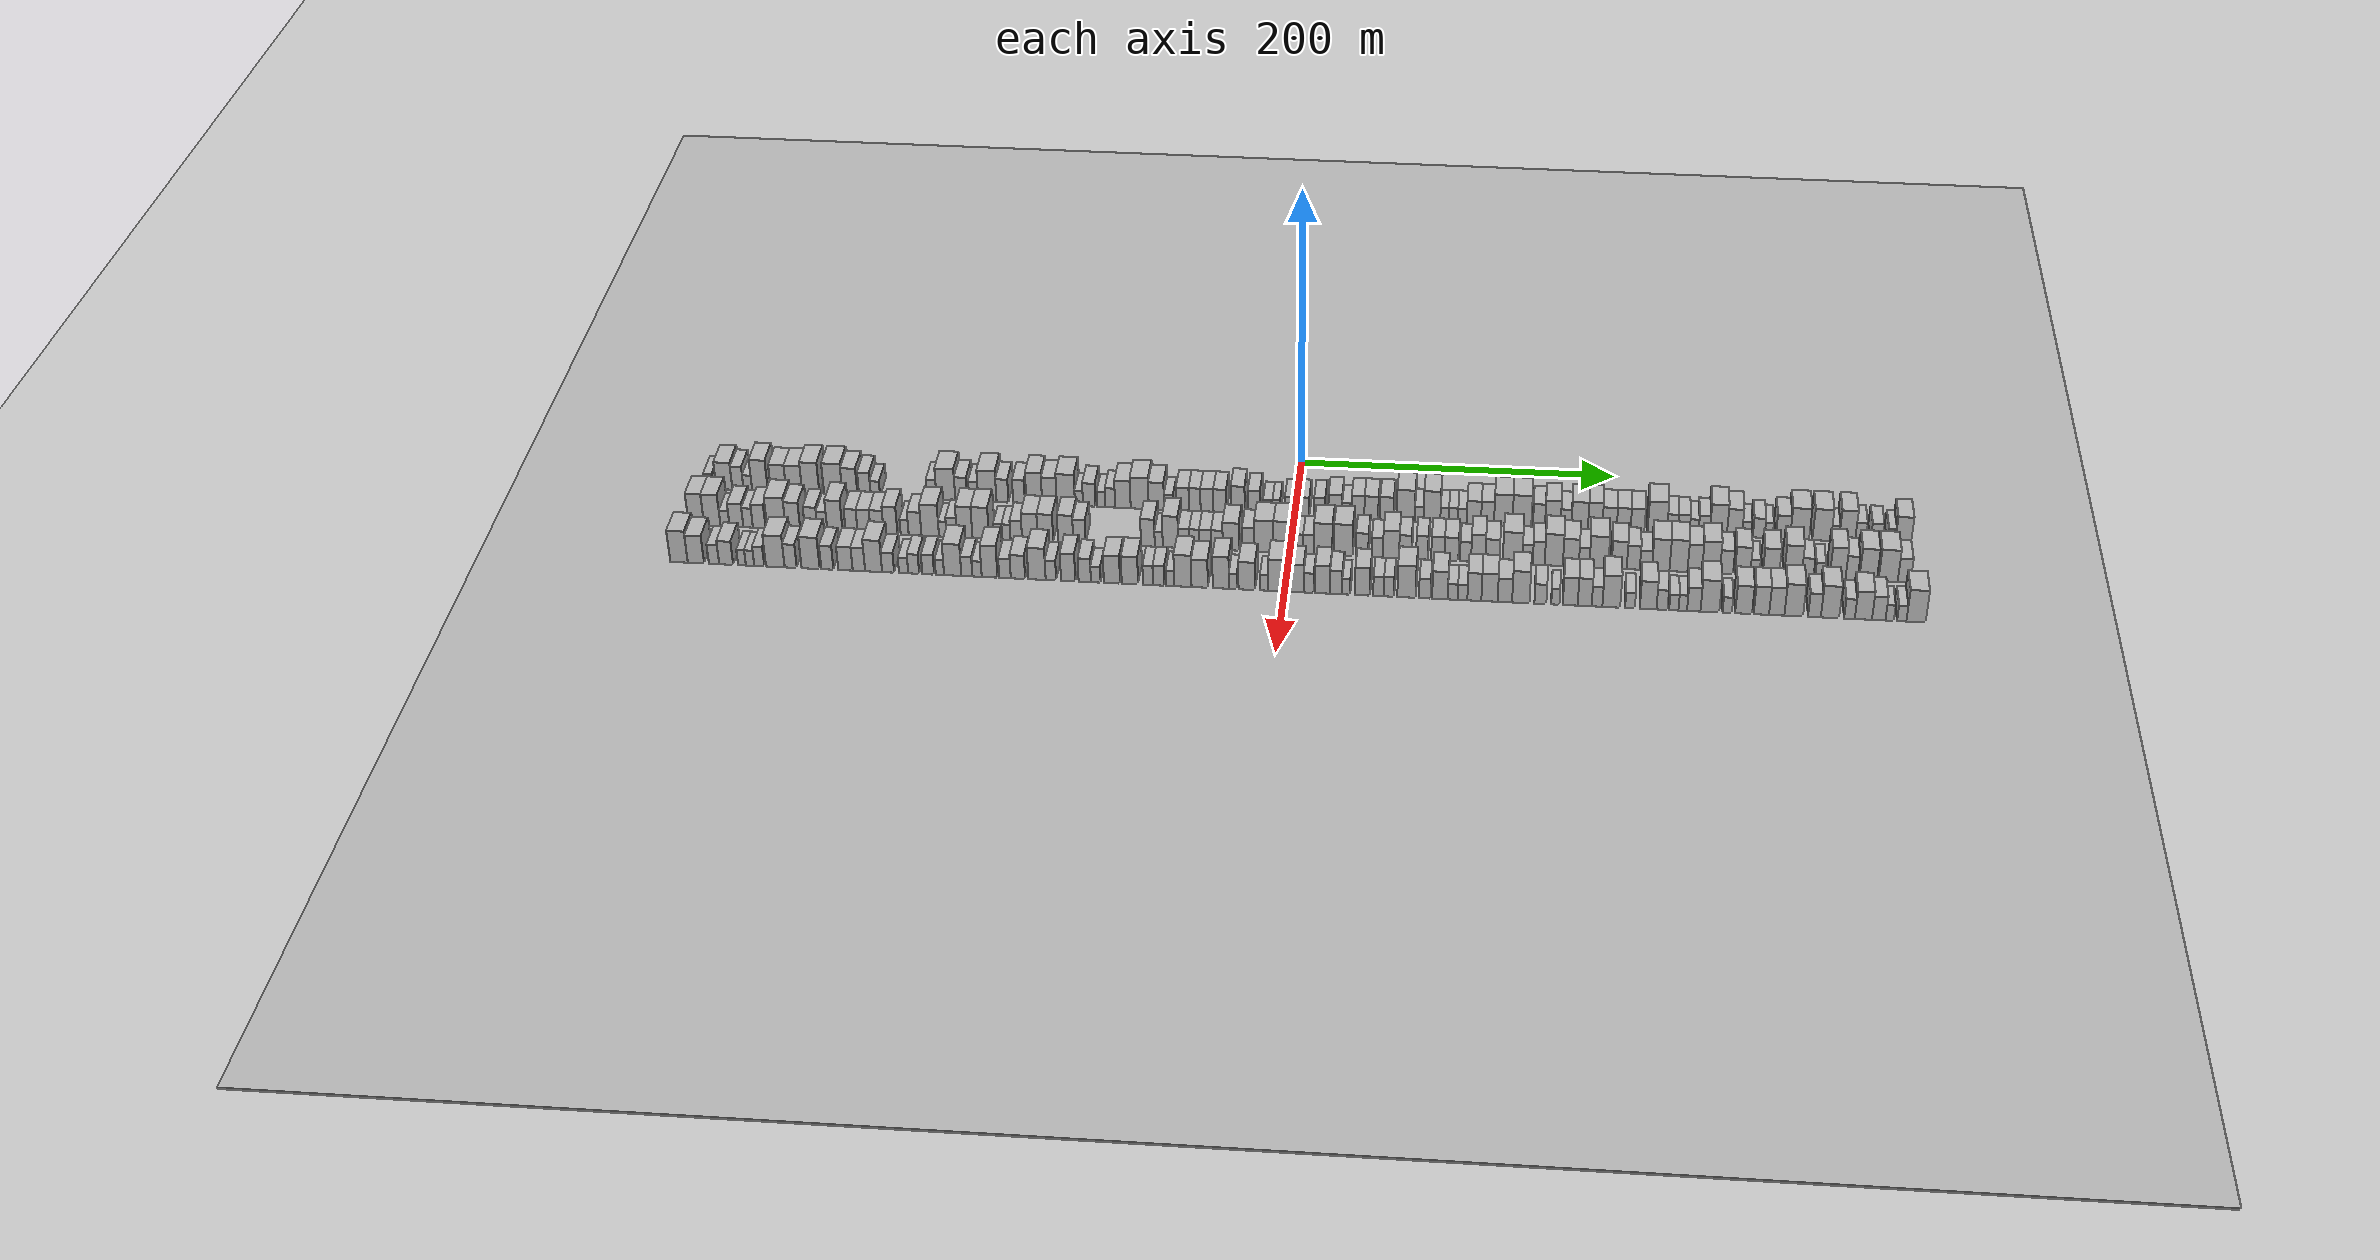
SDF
<?xml version="1.0" encoding="utf-8"?>

<sdf version="1.6">

   <world name="default">

      <gui fullscreen="0">

         <camera name="user_camera">

            <pose>-15 0 4.57585 0 0 0</pose>

            <view_controller>orbit</view_controller>

         </camera>

      </gui>

      <scene>

         <sky>

           <clouds>

             <speed>12</speed>

           </clouds>

         </sky>

         <ambient>0.4 0.4 0.4 1</ambient>

         <background>0.7 0.7 0.7 1</background>

         <shadows>1</shadows>

      </scene>

      <gravity>0 0 -9.8066</gravity>

      <magnetic_field>6e-06 2.3e-05 -4.2e-05</magnetic_field>

      <physics default="0" name="default_physics" type="ode">

         <ode>

            <solver>

               <type>quick</type>

               <iters>10</iters>

               <sor>1.0</sor>

               <use_dynamic_moi_rescaling>0</use_dynamic_moi_rescaling>

            </solver>

            <constraints>

               <cfm>0</cfm>

               <erp>0.2</erp>

               <contact_max_correcting_vel>100</contact_max_correcting_vel>

               <contact_surface_layer>0.001</contact_surface_layer>

            </constraints>

         </ode>

         <max_step_size>0.004</max_step_size>

         <real_time_factor>1</real_time_factor>

         <real_time_update_rate>250</real_time_update_rate>

      </physics>

      <light name="sun" type="directional">

         <cast_shadows>1</cast_shadows>

         <pose>0 0 10 0 0 0</pose>

         <diffuse>0.8 0.8 0.8 1</diffuse>

         <specular>0.2 0.2 0.2 1</specular>

         <attenuation>

            <range>1000</range>

            <constant>0.9</constant>

            <linear>0.01</linear>

            <quadratic>0.001</quadratic>

         </attenuation>

         <direction>-0.5 0.1 -0.9</direction>

      </light>

      <include>

         <name>ground_plane_1</name>

         <uri>model://HANNAS_ground_plane</uri>

         <pose>0 0 0  0 0 0</pose>

      </include>

      <include>

         <name>ground_plane_2</name>

         <uri>model://HANNAS_ground_plane</uri>

         <pose>100 0 0  0 0 0</pose>

      </include>

      <model name="building_1">

         <static>1</static>

         <pose frame="">50.0000 -374.2624 0 0.000000 0.000000 0.000000</pose>

         <link name="link">

            <pose frame="">0 0 6.00 0 0 0</pose>

            <collision name="collision">

               <geometry>

                  <box>

                     <size>20.0000 5.4753 12.0000</size>

                  </box>

               </geometry>

               <max_contacts>10</max_contacts>

               <surface>

                  <contact>

                     <ode/>

                  </contact>

                  <bounce/>

                  <friction>

                     <torsional>

                        <ode/>

                     </torsional>

                     <ode/>

                  </friction>

               </surface>

            </collision>

            <visual name="visual">

               <cast_shadows>0</cast_shadows>

               <geometry>

                  <box>

                     <size>20.0000 5.4753 12.0000</size>

                  </box>

               </geometry>

               <material>

                  <script>

                     <uri>model://HANNAS_wall/materials/scripts</uri>

                     <uri>model://HANNAS_wall/materials/textures</uri>

                     <name>vrc/HANNAS_wall</name>

                  </script>

               </material>

            </visual>

            <self_collide>0</self_collide>

            <enable_wind>0</enable_wind>

            <kinematic>0</kinematic>

         </link>

      </model>

      <model name="building_2">

         <static>1</static>

         <pose frame="">50.0000 -364.3549 0 0.000000 0.000000 0.000000</pose>

         <link name="link">

            <pose frame="">0 0 10.50 0 0 0</pose>

            <collision name="collision">

               <geometry>

                  <box>

                     <size>20.0000 10.3397 21.0000</size>

                  </box>

               </geometry>

               <max_contacts>10</max_contacts>

               <surface>

                  <contact>

                     <ode/>

                  </contact>

                  <bounce/>

                  <friction>

                     <torsional>

                        <ode/>

                     </torsional>

                     <ode/>

                  </friction>

               </surface>

            </collision>

            <visual name="visual">

               <cast_shadows>0</cast_shadows>

               <geometry>

                  <box>

                     <size>20.0000 10.3397 21.0000</size>

                  </box>

               </geometry>

               <material>

                  <script>

                     <uri>model://HANNAS_wall/materials/scripts</uri>

                     <uri>model://HANNAS_wall/materials/textures</uri>

                     <name>vrc/HANNAS_wall</name>

                  </script>

               </material>

            </visual>

            <self_collide>0</self_collide>

            <enable_wind>0</enable_wind>

            <kinematic>0</kinematic>

         </link>

      </model>

      <model name="building_3">

         <static>1</static>

         <pose frame="">50.0000 -355.5785 0 0.000000 0.000000 0.000000</pose>

         <link name="link">

            <pose frame="">0 0 9.00 0 0 0</pose>

            <collision name="collision">

               <geometry>

                  <box>

                     <size>20.0000 7.2129 18.0000</size>

                  </box>

               </geometry>

               <max_contacts>10</max_contacts>

               <surface>

                  <contact>

                     <ode/>

                  </contact>

                  <bounce/>

                  <friction>

                     <torsional>

                        <ode/>

                     </torsional>

                     <ode/>

                  </friction>

               </surface>

            </collision>

            <visual name="visual">

               <cast_shadows>0</cast_shadows>

               <geometry>

                  <box>

                     <size>20.0000 7.2129 18.0000</size>

                  </box>

               </geometry>

               <material>

                  <script>

                     <uri>model://HANNAS_wall/materials/scripts</uri>

                     <uri>model://HANNAS_wall/materials/textures</uri>

                     <name>vrc/HANNAS_wall</name>

                  </script>

               </material>

            </visual>

            <self_collide>0</self_collide>

            <enable_wind>0</enable_wind>

            <kinematic>0</kinematic>

         </link>

      </model>

      <model name="building_4">

         <static>1</static>

         <pose frame="">50.0000 -349.2453 0 0.000000 0.000000 0.000000</pose>

         <link name="link">

            <pose frame="">0 0 6.00 0 0 0</pose>

            <collision name="collision">

               <geometry>

                  <box>

                     <size>20.0000 5.4536 12.0000</size>

                  </box>

               </geometry>

               <max_contacts>10</max_contacts>

               <surface>

                  <contact>

                     <ode/>

                  </contact>

                  <bounce/>

                  <friction>

                     <torsional>

                        <ode/>

                     </torsional>

                     <ode/>

                  </friction>

               </surface>

            </collision>

            <visual name="visual">

               <cast_shadows>0</cast_shadows>

               <geometry>

                  <box>

                     <size>20.0000 5.4536 12.0000</size>

                  </box>

               </geometry>

               <material>

                  <script>

                     <uri>model://HANNAS_wall/materials/scripts</uri>

                     <uri>model://HANNAS_wall/materials/textures</uri>

                     <name>vrc/HANNAS_wall</name>

                  </script>

               </material>

            </visual>

            <self_collide>0</self_collide>

            <enable_wind>0</enable_wind>

            <kinematic>0</kinematic>

         </link>

      </model>

      <model name="building_5">

         <static>1</static>

         <pose frame="">50.0000 -341.4378 0 0.000000 0.000000 0.000000</pose>

         <link name="link">

            <pose frame="">0 0 12.00 0 0 0</pose>

            <collision name="collision">

               <geometry>

                  <box>

                     <size>20.0000 10.1614 24.0000</size>

                  </box>

               </geometry>

               <max_contacts>10</max_contacts>

               <surface>

                  <contact>

                     <ode/>

                  </contact>

                  <bounce/>

                  <friction>

                     <torsional>

                        <ode/>

                     </torsional>

                     <ode/>

                  </friction>

               </surface>

            </collision>

            <visual name="visual">

               <cast_shadows>0</cast_shadows>

               <geometry>

                  <box>

                     <size>20.0000 10.1614 24.0000</size>

                  </box>

               </geometry>

               <material>

                  <script>

                     <uri>model://HANNAS_wall/materials/scripts</uri>

                     <uri>model://HANNAS_wall/materials/textures</uri>

                     <name>vrc/HANNAS_wall</name>

                  </script>

               </material>

            </visual>

            <self_collide>0</self_collide>

            <enable_wind>0</enable_wind>

            <kinematic>0</kinematic>

         </link>

      </model>

      <model name="building_6">

         <static>1</static>

         <pose frame="">50.0000 -329.4169 0 0.000000 0.000000 0.000000</pose>

         <link name="link">

            <pose frame="">0 0 10.50 0 0 0</pose>

            <collision name="collision">

               <geometry>

                  <box>

                     <size>20.0000 9.8803 21.0000</size>

                  </box>

               </geometry>

               <max_contacts>10</max_contacts>

               <surface>

                  <contact>

                     <ode/>

                  </contact>

                  <bounce/>

                  <friction>

                     <torsional>

                        <ode/>

                     </torsional>

                     <ode/>

                  </friction>

               </surface>

            </collision>

            <visual name="visual">

               <cast_shadows>0</cast_shadows>

               <geometry>

                  <box>

                     <size>20.0000 9.8803 21.0000</size>

                  </box>

               </geometry>

               <material>

                  <script>

                     <uri>model://HANNAS_wall/materials/scripts</uri>

                     <uri>model://HANNAS_wall/materials/textures</uri>

                     <name>vrc/HANNAS_wall</name>

                  </script>

               </material>

            </visual>

            <self_collide>0</self_collide>

            <enable_wind>0</enable_wind>

            <kinematic>0</kinematic>

         </link>

      </model>

      <model name="building_7">

         <static>1</static>

         <pose frame="">50.0000 -319.3622 0 0.000000 0.000000 0.000000</pose>

         <link name="link">

            <pose frame="">0 0 10.50 0 0 0</pose>

            <collision name="collision">

               <geometry>

                  <box>

                     <size>20.0000 10.2292 21.0000</size>

                  </box>

               </geometry>

               <max_contacts>10</max_contacts>

               <surface>

                  <contact>

                     <ode/>

                  </contact>

                  <bounce/>

                  <friction>

                     <torsional>

                        <ode/>

                     </torsional>

                     <ode/>

                  </friction>

               </surface>

            </collision>

            <visual name="visual">

               <cast_shadows>0</cast_shadows>

               <geometry>

                  <box>

                     <size>20.0000 10.2292 21.0000</size>

                  </box>

               </geometry>

               <material>

                  <script>

                     <uri>model://HANNAS_wall/materials/scripts</uri>

                     <uri>model://HANNAS_wall/materials/textures</uri>

                     <name>vrc/HANNAS_wall</name>

                  </script>

               </material>

            </visual>

            <self_collide>0</self_collide>

            <enable_wind>0</enable_wind>

            <kinematic>0</kinematic>

         </link>

      </model>

      <model name="building_8">

         <static>1</static>

         <pose frame="">50.0000 -308.7134 0 0.000000 0.000000 0.000000</pose>

         <link name="link">

            <pose frame="">0 0 12.00 0 0 0</pose>

            <collision name="collision">

               <geometry>

                  <box>

                     <size>20.0000 11.0682 24.0000</size>

                  </box>

               </geometry>

               <max_contacts>10</max_contacts>

               <surface>

                  <contact>

                     <ode/>

                  </contact>

                  <bounce/>

                  <friction>

                     <torsional>

                        <ode/>

                     </torsional>

                     <ode/>

                  </friction>

               </surface>

            </collision>

            <visual name="visual">

               <cast_shadows>0</cast_shadows>

               <geometry>

                  <box>

                     <size>20.0000 11.0682 24.0000</size>

                  </box>

               </geometry>

               <material>

                  <script>

                     <uri>model://HANNAS_wall/materials/scripts</uri>

                     <uri>model://HANNAS_wall/materials/textures</uri>

                     <name>vrc/HANNAS_wall</name>

                  </script>

               </material>

            </visual>

            <self_collide>0</self_collide>

            <enable_wind>0</enable_wind>

            <kinematic>0</kinematic>

         </link>

      </model>

      <model name="building_9">

         <static>1</static>

         <pose frame="">50.0000 -294.2568 0 0.000000 0.000000 0.000000</pose>

         <link name="link">

            <pose frame="">0 0 12.00 0 0 0</pose>

            <collision name="collision">

               <geometry>

                  <box>

                     <size>20.0000 11.8451 24.0000</size>

                  </box>

               </geometry>

               <max_contacts>10</max_contacts>

               <surface>

                  <contact>

                     <ode/>

                  </contact>

                  <bounce/>

                  <friction>

                     <torsional>

                        <ode/>

                     </torsional>

                     <ode/>

                  </friction>

               </surface>

            </collision>

            <visual name="visual">

               <cast_shadows>0</cast_shadows>

               <geometry>

                  <box>

                     <size>20.0000 11.8451 24.0000</size>

                  </box>

               </geometry>

               <material>

                  <script>

                     <uri>model://HANNAS_wall/materials/scripts</uri>

                     <uri>model://HANNAS_wall/materials/textures</uri>

                     <name>vrc/HANNAS_wall</name>

                  </script>

               </material>

            </visual>

            <self_collide>0</self_collide>

            <enable_wind>0</enable_wind>

            <kinematic>0</kinematic>

         </link>

      </model>

      <model name="building_10">

         <static>1</static>

         <pose frame="">50.0000 -283.5182 0 0.000000 0.000000 0.000000</pose>

         <link name="link">

            <pose frame="">0 0 10.50 0 0 0</pose>

            <collision name="collision">

               <geometry>

                  <box>

                     <size>20.0000 9.6320 21.0000</size>

                  </box>

               </geometry>

               <max_contacts>10</max_contacts>

               <surface>

                  <contact>

                     <ode/>

                  </contact>

                  <bounce/>

                  <friction>

                     <torsional>

                        <ode/>

                     </torsional>

                     <ode/>

                  </friction>

               </surface>

            </collision>

            <visual name="visual">

               <cast_shadows>0</cast_shadows>

               <geometry>

                  <box>

                     <size>20.0000 9.6320 21.0000</size>

                  </box>

               </geometry>

               <material>

                  <script>

                     <uri>model://HANNAS_wall/materials/scripts</uri>

                     <uri>model://HANNAS_wall/materials/textures</uri>

                     <name>vrc/HANNAS_wall</name>

                  </script>

               </material>

            </visual>

            <self_collide>0</self_collide>

            <enable_wind>0</enable_wind>

            <kinematic>0</kinematic>

         </link>

      </model>

      <model name="building_11">

         <static>1</static>

         <pose frame="">50.0000 -273.9121 0 0.000000 0.000000 0.000000</pose>

         <link name="link">

            <pose frame="">0 0 9.00 0 0 0</pose>

            <collision name="collision">

               <geometry>

                  <box>

                     <size>20.0000 7.5804 18.0000</size>

                  </box>

               </geometry>

               <max_contacts>10</max_contacts>

               <surface>

                  <contact>

                     <ode/>

                  </contact>

                  <bounce/>

                  <friction>

                     <torsional>

                        <ode/>

                     </torsional>

                     <ode/>

                  </friction>

               </surface>

            </collision>

            <visual name="visual">

               <cast_shadows>0</cast_shadows>

               <geometry>

                  <box>

                     <size>20.0000 7.5804 18.0000</size>

                  </box>

               </geometry>

               <material>

                  <script>

                     <uri>model://HANNAS_wall/materials/scripts</uri>

                     <uri>model://HANNAS_wall/materials/textures</uri>

                     <name>vrc/HANNAS_wall</name>

                  </script>

               </material>

            </visual>

            <self_collide>0</self_collide>

            <enable_wind>0</enable_wind>

            <kinematic>0</kinematic>

         </link>

      </model>

      <model name="building_12">

         <static>1</static>

         <pose frame="">50.0000 -267.1441 0 0.000000 0.000000 0.000000</pose>

         <link name="link">

            <pose frame="">0 0 6.00 0 0 0</pose>

            <collision name="collision">

               <geometry>

                  <box>

                     <size>20.0000 5.9556 12.0000</size>

                  </box>

               </geometry>

               <max_contacts>10</max_contacts>

               <surface>

                  <contact>

                     <ode/>

                  </contact>

                  <bounce/>

                  <friction>

                     <torsional>

                        <ode/>

                     </torsional>

                     <ode/>

                  </friction>

               </surface>

            </collision>

            <visual name="visual">

               <cast_shadows>0</cast_shadows>

               <geometry>

                  <box>

                     <size>20.0000 5.9556 12.0000</size>

                  </box>

               </geometry>

               <material>

                  <script>

                     <uri>model://HANNAS_wall/materials/scripts</uri>

                     <uri>model://HANNAS_wall/materials/textures</uri>

                     <name>vrc/HANNAS_wall</name>

                  </script>

               </material>

            </visual>

            <self_collide>0</self_collide>

            <enable_wind>0</enable_wind>

            <kinematic>0</kinematic>

         </link>

      </model>

      <model name="building_13">

         <static>1</static>

         <pose frame="">50.0000 -231.0191 0 0.000000 0.000000 0.000000</pose>

         <link name="link">

            <pose frame="">0 0 7.50 0 0 0</pose>

            <collision name="collision">

               <geometry>

                  <box>

                     <size>20.0000 6.0981 15.0000</size>

                  </box>

               </geometry>

               <max_contacts>10</max_contacts>

               <surface>

                  <contact>

                     <ode/>

                  </contact>

                  <bounce/>

                  <friction>

                     <torsional>

                        <ode/>

                     </torsional>

                     <ode/>

                  </friction>

               </surface>

            </collision>

            <visual name="visual">

               <cast_shadows>0</cast_shadows>

               <geometry>

                  <box>

                     <size>20.0000 6.0981 15.0000</size>

                  </box>

               </geometry>

               <material>

                  <script>

                     <uri>model://HANNAS_wall/materials/scripts</uri>

                     <uri>model://HANNAS_wall/materials/textures</uri>

                     <name>vrc/HANNAS_wall</name>

                  </script>

               </material>

            </visual>

            <self_collide>0</self_collide>

            <enable_wind>0</enable_wind>

            <kinematic>0</kinematic>

         </link>

      </model>

      <model name="building_14">

         <static>1</static>

         <pose frame="">50.0000 -221.9719 0 0.000000 0.000000 0.000000</pose>

         <link name="link">

            <pose frame="">0 0 12.00 0 0 0</pose>

            <collision name="collision">

               <geometry>

                  <box>

                     <size>20.0000 11.9962 24.0000</size>

                  </box>

               </geometry>

               <max_contacts>10</max_contacts>

               <surface>

                  <contact>

                     <ode/>

                  </contact>

                  <bounce/>

                  <friction>

                     <torsional>

                        <ode/>

                     </torsional>

                     <ode/>

                  </friction>

               </surface>

            </collision>

            <visual name="visual">

               <cast_shadows>0</cast_shadows>

               <geometry>

                  <box>

                     <size>20.0000 11.9962 24.0000</size>

                  </box>

               </geometry>

               <material>

                  <script>

                     <uri>model://HANNAS_wall/materials/scripts</uri>

                     <uri>model://HANNAS_wall/materials/textures</uri>

                     <name>vrc/HANNAS_wall</name>

                  </script>

               </material>

            </visual>

            <self_collide>0</self_collide>

            <enable_wind>0</enable_wind>

            <kinematic>0</kinematic>

         </link>

      </model>

      <model name="building_15">

         <static>1</static>

         <pose frame="">50.0000 -212.1358 0 0.000000 0.000000 0.000000</pose>

         <link name="link">

            <pose frame="">0 0 9.00 0 0 0</pose>

            <collision name="collision">

               <geometry>

                  <box>

                     <size>20.0000 7.6759 18.0000</size>

                  </box>

               </geometry>

               <max_contacts>10</max_contacts>

               <surface>

                  <contact>

                     <ode/>

                  </contact>

                  <bounce/>

                  <friction>

                     <torsional>

                        <ode/>

                     </torsional>

                     <ode/>

                  </friction>

               </surface>

            </collision>

            <visual name="visual">

               <cast_shadows>0</cast_shadows>

               <geometry>

                  <box>

                     <size>20.0000 7.6759 18.0000</size>

                  </box>

               </geometry>

               <material>

                  <script>

                     <uri>model://HANNAS_wall/materials/scripts</uri>

                     <uri>model://HANNAS_wall/materials/textures</uri>

                     <name>vrc/HANNAS_wall</name>

                  </script>

               </material>

            </visual>

            <self_collide>0</self_collide>

            <enable_wind>0</enable_wind>

            <kinematic>0</kinematic>

         </link>

      </model>

      <model name="building_16">

         <static>1</static>

         <pose frame="">50.0000 -204.2858 0 0.000000 0.000000 0.000000</pose>

         <link name="link">

            <pose frame="">0 0 7.50 0 0 0</pose>

            <collision name="collision">

               <geometry>

                  <box>

                     <size>20.0000 6.0241 15.0000</size>

                  </box>

               </geometry>

               <max_contacts>10</max_contacts>

               <surface>

                  <contact>

                     <ode/>

                  </contact>

                  <bounce/>

                  <friction>

                     <torsional>

                        <ode/>

                     </torsional>

                     <ode/>

                  </friction>

               </surface>

            </collision>

            <visual name="visual">

               <cast_shadows>0</cast_shadows>

               <geometry>

                  <box>

                     <size>20.0000 6.0241 15.0000</size>

                  </box>

               </geometry>

               <material>

                  <script>

                     <uri>model://HANNAS_wall/materials/scripts</uri>

                     <uri>model://HANNAS_wall/materials/textures</uri>

                     <name>vrc/HANNAS_wall</name>

                  </script>

               </material>

            </visual>

            <self_collide>0</self_collide>

            <enable_wind>0</enable_wind>

            <kinematic>0</kinematic>

         </link>

      </model>

      <model name="building_17">

         <static>1</static>

         <pose frame="">50.0000 -195.4628 0 0.000000 0.000000 0.000000</pose>

         <link name="link">

            <pose frame="">0 0 12.00 0 0 0</pose>

            <collision name="collision">

               <geometry>

                  <box>

                     <size>20.0000 11.6219 24.0000</size>

                  </box>

               </geometry>

               <max_contacts>10</max_contacts>

               <surface>

                  <contact>

                     <ode/>

                  </contact>

                  <bounce/>

                  <friction>

                     <torsional>

                        <ode/>

                     </torsional>

                     <ode/>

                  </friction>

               </surface>

            </collision>

            <visual name="visual">

               <cast_shadows>0</cast_shadows>

               <geometry>

                  <box>

                     <size>20.0000 11.6219 24.0000</size>

                  </box>

               </geometry>

               <material>

                  <script>

                     <uri>model://HANNAS_wall/materials/scripts</uri>

                     <uri>model://HANNAS_wall/materials/textures</uri>

                     <name>vrc/HANNAS_wall</name>

                  </script>

               </material>

            </visual>

            <self_collide>0</self_collide>

            <enable_wind>0</enable_wind>

            <kinematic>0</kinematic>

         </link>

      </model>

      <model name="building_18">

         <static>1</static>

         <pose frame="">50.0000 -185.8370 0 0.000000 0.000000 0.000000</pose>

         <link name="link">

            <pose frame="">0 0 9.00 0 0 0</pose>

            <collision name="collision">

               <geometry>

                  <box>

                     <size>20.0000 7.6296 18.0000</size>

                  </box>

               </geometry>

               <max_contacts>10</max_contacts>

               <surface>

                  <contact>

                     <ode/>

                  </contact>

                  <bounce/>

                  <friction>

                     <torsional>

                        <ode/>

                     </torsional>

                     <ode/>

                  </friction>

               </surface>

            </collision>

            <visual name="visual">

               <cast_shadows>0</cast_shadows>

               <geometry>

                  <box>

                     <size>20.0000 7.6296 18.0000</size>

                  </box>

               </geometry>

               <material>

                  <script>

                     <uri>model://HANNAS_wall/materials/scripts</uri>

                     <uri>model://HANNAS_wall/materials/textures</uri>

                     <name>vrc/HANNAS_wall</name>

                  </script>

               </material>

            </visual>

            <self_collide>0</self_collide>

            <enable_wind>0</enable_wind>

            <kinematic>0</kinematic>

         </link>

      </model>

      <model name="building_19">

         <static>1</static>

         <pose frame="">50.0000 -175.2739 0 0.000000 0.000000 0.000000</pose>

         <link name="link">

            <pose frame="">0 0 9.00 0 0 0</pose>

            <collision name="collision">

               <geometry>

                  <box>

                     <size>20.0000 7.4967 18.0000</size>

                  </box>

               </geometry>

               <max_contacts>10</max_contacts>

               <surface>

                  <contact>

                     <ode/>

                  </contact>

                  <bounce/>

                  <friction>

                     <torsional>

                        <ode/>

                     </torsional>

                     <ode/>

                  </friction>

               </surface>

            </collision>

            <visual name="visual">

               <cast_shadows>0</cast_shadows>

               <geometry>

                  <box>

                     <size>20.0000 7.4967 18.0000</size>

                  </box>

               </geometry>

               <material>

                  <script>

                     <uri>model://HANNAS_wall/materials/scripts</uri>

                     <uri>model://HANNAS_wall/materials/textures</uri>

                     <name>vrc/HANNAS_wall</name>

                  </script>

               </material>

            </visual>

            <self_collide>0</self_collide>

            <enable_wind>0</enable_wind>

            <kinematic>0</kinematic>

         </link>

      </model>

      <model name="building_20">

         <static>1</static>

         <pose frame="">50.0000 -165.5309 0 0.000000 0.000000 0.000000</pose>

         <link name="link">

            <pose frame="">0 0 12.00 0 0 0</pose>

            <collision name="collision">

               <geometry>

                  <box>

                     <size>20.0000 9.9893 24.0000</size>

                  </box>

               </geometry>

               <max_contacts>10</max_contacts>

               <surface>

                  <contact>

                     <ode/>

                  </contact>

                  <bounce/>

                  <friction>

                     <torsional>

                        <ode/>

                     </torsional>

                     <ode/>

                  </friction>

               </surface>

            </collision>

            <visual name="visual">

               <cast_shadows>0</cast_shadows>

               <geometry>

                  <box>

                     <size>20.0000 9.9893 24.0000</size>

                  </box>

               </geometry>

               <material>

                  <script>

                     <uri>model://HANNAS_wall/materials/scripts</uri>

                     <uri>model://HANNAS_wall/materials/textures</uri>

                     <name>vrc/HANNAS_wall</name>

                  </script>

               </material>

            </visual>

            <self_collide>0</self_collide>

            <enable_wind>0</enable_wind>

            <kinematic>0</kinematic>

         </link>

      </model>

      <model name="building_21">

         <static>1</static>

         <pose frame="">50.0000 -155.8744 0 0.000000 0.000000 0.000000</pose>

         <link name="link">

            <pose frame="">0 0 10.50 0 0 0</pose>

            <collision name="collision">

               <geometry>

                  <box>

                     <size>20.0000 9.3238 21.0000</size>

                  </box>

               </geometry>

               <max_contacts>10</max_contacts>

               <surface>

                  <contact>

                     <ode/>

                  </contact>

                  <bounce/>

                  <friction>

                     <torsional>

                        <ode/>

                     </torsional>

                     <ode/>

                  </friction>

               </surface>

            </collision>

            <visual name="visual">

               <cast_shadows>0</cast_shadows>

               <geometry>

                  <box>

                     <size>20.0000 9.3238 21.0000</size>

                  </box>

               </geometry>

               <material>

                  <script>

                     <uri>model://HANNAS_wall/materials/scripts</uri>

                     <uri>model://HANNAS_wall/materials/textures</uri>

                     <name>vrc/HANNAS_wall</name>

                  </script>

               </material>

            </visual>

            <self_collide>0</self_collide>

            <enable_wind>0</enable_wind>

            <kinematic>0</kinematic>

         </link>

      </model>

      <model name="building_22">

         <static>1</static>

         <pose frame="">50.0000 -145.4319 0 0.000000 0.000000 0.000000</pose>

         <link name="link">

            <pose frame="">0 0 12.00 0 0 0</pose>

            <collision name="collision">

               <geometry>

                  <box>

                     <size>20.0000 11.5612 24.0000</size>

                  </box>

               </geometry>

               <max_contacts>10</max_contacts>

               <surface>

                  <contact>

                     <ode/>

                  </contact>

                  <bounce/>

                  <friction>

                     <torsional>

                        <ode/>

                     </torsional>

                     <ode/>

                  </friction>

               </surface>

            </collision>

            <visual name="visual">

               <cast_shadows>0</cast_shadows>

               <geometry>

                  <box>

                     <size>20.0000 11.5612 24.0000</size>

                  </box>

               </geometry>

               <material>

                  <script>

                     <uri>model://HANNAS_wall/materials/scripts</uri>

                     <uri>model://HANNAS_wall/materials/textures</uri>

                     <name>vrc/HANNAS_wall</name>

                  </script>

               </material>

            </visual>

            <self_collide>0</self_collide>

            <enable_wind>0</enable_wind>

            <kinematic>0</kinematic>

         </link>

      </model>

      <model name="building_23">

         <static>1</static>

         <pose frame="">50.0000 -137.0996 0 0.000000 0.000000 0.000000</pose>

         <link name="link">

            <pose frame="">0 0 6.00 0 0 0</pose>

            <collision name="collision">

               <geometry>

                  <box>

                     <size>20.0000 5.1034 12.0000</size>

                  </box>

               </geometry>

               <max_contacts>10</max_contacts>

               <surface>

                  <contact>

                     <ode/>

                  </contact>

                  <bounce/>

                  <friction>

                     <torsional>

                        <ode/>

                     </torsional>

                     <ode/>

                  </friction>

               </surface>

            </collision>

            <visual name="visual">

               <cast_shadows>0</cast_shadows>

               <geometry>

                  <box>

                     <size>20.0000 5.1034 12.0000</size>

                  </box>

               </geometry>

               <material>

                  <script>

                     <uri>model://HANNAS_wall/materials/scripts</uri>

                     <uri>model://HANNAS_wall/materials/textures</uri>

                     <name>vrc/HANNAS_wall</name>

                  </script>

               </material>

            </visual>

            <self_collide>0</self_collide>

            <enable_wind>0</enable_wind>

            <kinematic>0</kinematic>

         </link>

      </model>

      <model name="building_24">

         <static>1</static>

         <pose frame="">50.0000 -130.5739 0 0.000000 0.000000 0.000000</pose>

         <link name="link">

            <pose frame="">0 0 9.00 0 0 0</pose>

            <collision name="collision">

               <geometry>

                  <box>

                     <size>20.0000 7.9480 18.0000</size>

                  </box>

               </geometry>

               <max_contacts>10</max_contacts>

               <surface>

                  <contact>

                     <ode/>

                  </contact>

                  <bounce/>

                  <friction>

                     <torsional>

                        <ode/>

                     </torsional>

                     <ode/>

                  </friction>

               </surface>

            </collision>

            <visual name="visual">

               <cast_shadows>0</cast_shadows>

               <geometry>

                  <box>

                     <size>20.0000 7.9480 18.0000</size>

                  </box>

               </geometry>

               <material>

                  <script>

                     <uri>model://HANNAS_wall/materials/scripts</uri>

                     <uri>model://HANNAS_wall/materials/textures</uri>

                     <name>vrc/HANNAS_wall</name>

                  </script>

               </material>

            </visual>

            <self_collide>0</self_collide>

            <enable_wind>0</enable_wind>

            <kinematic>0</kinematic>

         </link>

      </model>

      <model name="building_25">

         <static>1</static>

         <pose frame="">50.0000 -122.9616 0 0.000000 0.000000 0.000000</pose>

         <link name="link">

            <pose frame="">0 0 6.00 0 0 0</pose>

            <collision name="collision">

               <geometry>

                  <box>

                     <size>20.0000 5.2764 12.0000</size>

                  </box>

               </geometry>

               <max_contacts>10</max_contacts>

               <surface>

                  <contact>

                     <ode/>

                  </contact>

                  <bounce/>

                  <friction>

                     <torsional>

                        <ode/>

                     </torsional>

                     <ode/>

                  </friction>

               </surface>

            </collision>

            <visual name="visual">

               <cast_shadows>0</cast_shadows>

               <geometry>

                  <box>

                     <size>20.0000 5.2764 12.0000</size>

                  </box>

               </geometry>

               <material>

                  <script>

                     <uri>model://HANNAS_wall/materials/scripts</uri>

                     <uri>model://HANNAS_wall/materials/textures</uri>

                     <name>vrc/HANNAS_wall</name>

                  </script>

               </material>

            </visual>

            <self_collide>0</self_collide>

            <enable_wind>0</enable_wind>

            <kinematic>0</kinematic>

         </link>

      </model>

      <model name="building_26">

         <static>1</static>

         <pose frame="">50.0000 -117.2338 0 0.000000 0.000000 0.000000</pose>

         <link name="link">

            <pose frame="">0 0 7.50 0 0 0</pose>

            <collision name="collision">

               <geometry>

                  <box>

                     <size>20.0000 6.1794 15.0000</size>

                  </box>

               </geometry>

               <max_contacts>10</max_contacts>

               <surface>

                  <contact>

                     <ode/>

                  </contact>

                  <bounce/>

                  <friction>

                     <torsional>

                        <ode/>

                     </torsional>

                     <ode/>

                  </friction>

               </surface>

            </collision>

            <visual name="visual">

               <cast_shadows>0</cast_shadows>

               <geometry>

                  <box>

                     <size>20.0000 6.1794 15.0000</size>

                  </box>

               </geometry>

               <material>

                  <script>

                     <uri>model://HANNAS_wall/materials/scripts</uri>

                     <uri>model://HANNAS_wall/materials/textures</uri>

                     <name>vrc/HANNAS_wall</name>

                  </script>

               </material>

            </visual>

            <self_collide>0</self_collide>

            <enable_wind>0</enable_wind>

            <kinematic>0</kinematic>

         </link>

      </model>

      <model name="building_27">

         <static>1</static>

         <pose frame="">50.0000 -109.2089 0 0.000000 0.000000 0.000000</pose>

         <link name="link">

            <pose frame="">0 0 10.50 0 0 0</pose>

            <collision name="collision">

               <geometry>

                  <box>

                     <size>20.0000 9.8703 21.0000</size>

                  </box>

               </geometry>

               <max_contacts>10</max_contacts>

               <surface>

                  <contact>

                     <ode/>

                  </contact>

                  <bounce/>

                  <friction>

                     <torsional>

                        <ode/>

                     </torsional>

                     <ode/>

                  </friction>

               </surface>

            </collision>

            <visual name="visual">

               <cast_shadows>0</cast_shadows>

               <geometry>

                  <box>

                     <size>20.0000 9.8703 21.0000</size>

                  </box>

               </geometry>

               <material>

                  <script>

                     <uri>model://HANNAS_wall/materials/scripts</uri>

                     <uri>model://HANNAS_wall/materials/textures</uri>

                     <name>vrc/HANNAS_wall</name>

                  </script>

               </material>

            </visual>

            <self_collide>0</self_collide>

            <enable_wind>0</enable_wind>

            <kinematic>0</kinematic>

         </link>

      </model>

      <model name="building_28">

         <static>1</static>

         <pose frame="">50.0000 -98.5389 0 0.000000 0.000000 0.000000</pose>

         <link name="link">

            <pose frame="">0 0 12.00 0 0 0</pose>

            <collision name="collision">

               <geometry>

                  <box>

                     <size>20.0000 11.4696 24.0000</size>

                  </box>

               </geometry>

               <max_contacts>10</max_contacts>

               <surface>

                  <contact>

                     <ode/>

                  </contact>

                  <bounce/>

                  <friction>

                     <torsional>

                        <ode/>

                     </torsional>

                     <ode/>

                  </friction>

               </surface>

            </collision>

            <visual name="visual">

               <cast_shadows>0</cast_shadows>

               <geometry>

                  <box>

                     <size>20.0000 11.4696 24.0000</size>

                  </box>

               </geometry>

               <material>

                  <script>

                     <uri>model://HANNAS_wall/materials/scripts</uri>

                     <uri>model://HANNAS_wall/materials/textures</uri>

                     <name>vrc/HANNAS_wall</name>

                  </script>

               </material>

            </visual>

            <self_collide>0</self_collide>

            <enable_wind>0</enable_wind>

            <kinematic>0</kinematic>

         </link>

      </model>

      <model name="building_29">

         <static>1</static>

         <pose frame="">50.0000 -87.9355 0 0.000000 0.000000 0.000000</pose>

         <link name="link">

            <pose frame="">0 0 10.50 0 0 0</pose>

            <collision name="collision">

               <geometry>

                  <box>

                     <size>20.0000 9.7372 21.0000</size>

                  </box>

               </geometry>

               <max_contacts>10</max_contacts>

               <surface>

                  <contact>

                     <ode/>

                  </contact>

                  <bounce/>

                  <friction>

                     <torsional>

                        <ode/>

                     </torsional>

                     <ode/>

                  </friction>

               </surface>

            </collision>

            <visual name="visual">

               <cast_shadows>0</cast_shadows>

               <geometry>

                  <box>

                     <size>20.0000 9.7372 21.0000</size>

                  </box>

               </geometry>

               <material>

                  <script>

                     <uri>model://HANNAS_wall/materials/scripts</uri>

                     <uri>model://HANNAS_wall/materials/textures</uri>

                     <name>vrc/HANNAS_wall</name>

                  </script>

               </material>

            </visual>

            <self_collide>0</self_collide>

            <enable_wind>0</enable_wind>

            <kinematic>0</kinematic>

         </link>

      </model>

      <model name="building_30">

         <static>1</static>

         <pose frame="">50.0000 -80.1700 0 0.000000 0.000000 0.000000</pose>

         <link name="link">

            <pose frame="">0 0 6.00 0 0 0</pose>

            <collision name="collision">

               <geometry>

                  <box>

                     <size>20.0000 5.7939 12.0000</size>

                  </box>

               </geometry>

               <max_contacts>10</max_contacts>

               <surface>

                  <contact>

                     <ode/>

                  </contact>

                  <bounce/>

                  <friction>

                     <torsional>

                        <ode/>

                     </torsional>

                     <ode/>

                  </friction>

               </surface>

            </collision>

            <visual name="visual">

               <cast_shadows>0</cast_shadows>

               <geometry>

                  <box>

                     <size>20.0000 5.7939 12.0000</size>

                  </box>

               </geometry>

               <material>

                  <script>

                     <uri>model://HANNAS_wall/materials/scripts</uri>

                     <uri>model://HANNAS_wall/materials/textures</uri>

                     <name>vrc/HANNAS_wall</name>

                  </script>

               </material>

            </visual>

            <self_collide>0</self_collide>

            <enable_wind>0</enable_wind>

            <kinematic>0</kinematic>

         </link>

      </model>

      <model name="building_31">

         <static>1</static>

         <pose frame="">50.0000 -71.2959 0 0.000000 0.000000 0.000000</pose>

         <link name="link">

            <pose frame="">0 0 9.00 0 0 0</pose>

            <collision name="collision">

               <geometry>

                  <box>

                     <size>20.0000 7.9543 18.0000</size>

                  </box>

               </geometry>

               <max_contacts>10</max_contacts>

               <surface>

                  <contact>

                     <ode/>

                  </contact>

                  <bounce/>

                  <friction>

                     <torsional>

                        <ode/>

                     </torsional>

                     <ode/>

                  </friction>

               </surface>

            </collision>

            <visual name="visual">

               <cast_shadows>0</cast_shadows>

               <geometry>

                  <box>

                     <size>20.0000 7.9543 18.0000</size>

                  </box>

               </geometry>

               <material>

                  <script>

                     <uri>model://HANNAS_wall/materials/scripts</uri>

                     <uri>model://HANNAS_wall/materials/textures</uri>

                     <name>vrc/HANNAS_wall</name>

                  </script>

               </material>

            </visual>

            <self_collide>0</self_collide>

            <enable_wind>0</enable_wind>

            <kinematic>0</kinematic>

         </link>

      </model>

      <model name="building_32">

         <static>1</static>

         <pose frame="">50.0000 -63.6211 0 0.000000 0.000000 0.000000</pose>

         <link name="link">

            <pose frame="">0 0 9.00 0 0 0</pose>

            <collision name="collision">

               <geometry>

                  <box>

                     <size>20.0000 7.3951 18.0000</size>

                  </box>

               </geometry>

               <max_contacts>10</max_contacts>

               <surface>

                  <contact>

                     <ode/>

                  </contact>

                  <bounce/>

                  <friction>

                     <torsional>

                        <ode/>

                     </torsional>

                     <ode/>

                  </friction>

               </surface>

            </collision>

            <visual name="visual">

               <cast_shadows>0</cast_shadows>

               <geometry>

                  <box>

                     <size>20.0000 7.3951 18.0000</size>

                  </box>

               </geometry>

               <material>

                  <script>

                     <uri>model://HANNAS_wall/materials/scripts</uri>

                     <uri>model://HANNAS_wall/materials/textures</uri>

                     <name>vrc/HANNAS_wall</name>

                  </script>

               </material>

            </visual>

            <self_collide>0</self_collide>

            <enable_wind>0</enable_wind>

            <kinematic>0</kinematic>

         </link>

      </model>

      <model name="building_33">

         <static>1</static>

         <pose frame="">50.0000 -55.8472 0 0.000000 0.000000 0.000000</pose>

         <link name="link">

            <pose frame="">0 0 9.00 0 0 0</pose>

            <collision name="collision">

               <geometry>

                  <box>

                     <size>20.0000 8.1526 18.0000</size>

                  </box>

               </geometry>

               <max_contacts>10</max_contacts>

               <surface>

                  <contact>

                     <ode/>

                  </contact>

                  <bounce/>

                  <friction>

                     <torsional>

                        <ode/>

                     </torsional>

                     <ode/>

                  </friction>

               </surface>

            </collision>

            <visual name="visual">

               <cast_shadows>0</cast_shadows>

               <geometry>

                  <box>

                     <size>20.0000 8.1526 18.0000</size>

                  </box>

               </geometry>

               <material>

                  <script>

                     <uri>model://HANNAS_wall/materials/scripts</uri>

                     <uri>model://HANNAS_wall/materials/textures</uri>

                     <name>vrc/HANNAS_wall</name>

                  </script>

               </material>

            </visual>

            <self_collide>0</self_collide>

            <enable_wind>0</enable_wind>

            <kinematic>0</kinematic>

         </link>

      </model>

      <model name="building_34">

         <static>1</static>

         <pose frame="">50.0000 -47.7403 0 0.000000 0.000000 0.000000</pose>

         <link name="link">

            <pose frame="">0 0 9.00 0 0 0</pose>

            <collision name="collision">

               <geometry>

                  <box>

                     <size>20.0000 8.0612 18.0000</size>

                  </box>

               </geometry>

               <max_contacts>10</max_contacts>

               <surface>

                  <contact>

                     <ode/>

                  </contact>

                  <bounce/>

                  <friction>

                     <torsional>

                        <ode/>

                     </torsional>

                     <ode/>

                  </friction>

               </surface>

            </collision>

            <visual name="visual">

               <cast_shadows>0</cast_shadows>

               <geometry>

                  <box>

                     <size>20.0000 8.0612 18.0000</size>

                  </box>

               </geometry>

               <material>

                  <script>

                     <uri>model://HANNAS_wall/materials/scripts</uri>

                     <uri>model://HANNAS_wall/materials/textures</uri>

                     <name>vrc/HANNAS_wall</name>

                  </script>

               </material>

            </visual>

            <self_collide>0</self_collide>

            <enable_wind>0</enable_wind>

            <kinematic>0</kinematic>

         </link>

      </model>

      <model name="building_35">

         <static>1</static>

         <pose frame="">50.0000 -36.3752 0 0.000000 0.000000 0.000000</pose>

         <link name="link">

            <pose frame="">0 0 10.50 0 0 0</pose>

            <collision name="collision">

               <geometry>

                  <box>

                     <size>20.0000 8.6689 21.0000</size>

                  </box>

               </geometry>

               <max_contacts>10</max_contacts>

               <surface>

                  <contact>

                     <ode/>

                  </contact>

                  <bounce/>

                  <friction>

                     <torsional>

                        <ode/>

                     </torsional>

                     <ode/>

                  </friction>

               </surface>

            </collision>

            <visual name="visual">

               <cast_shadows>0</cast_shadows>

               <geometry>

                  <box>

                     <size>20.0000 8.6689 21.0000</size>

                  </box>

               </geometry>

               <material>

                  <script>

                     <uri>model://HANNAS_wall/materials/scripts</uri>

                     <uri>model://HANNAS_wall/materials/textures</uri>

                     <name>vrc/HANNAS_wall</name>

                  </script>

               </material>

            </visual>

            <self_collide>0</self_collide>

            <enable_wind>0</enable_wind>

            <kinematic>0</kinematic>

         </link>

      </model>

      <model name="building_36">

         <static>1</static>

         <pose frame="">50.0000 -26.2224 0 0.000000 0.000000 0.000000</pose>

         <link name="link">

            <pose frame="">0 0 9.00 0 0 0</pose>

            <collision name="collision">

               <geometry>

                  <box>

                     <size>20.0000 7.6368 18.0000</size>

                  </box>

               </geometry>

               <max_contacts>10</max_contacts>

               <surface>

                  <contact>

                     <ode/>

                  </contact>

                  <bounce/>

                  <friction>

                     <torsional>

                        <ode/>

                     </torsional>

                     <ode/>

                  </friction>

               </surface>

            </collision>

            <visual name="visual">

               <cast_shadows>0</cast_shadows>

               <geometry>

                  <box>

                     <size>20.0000 7.6368 18.0000</size>

                  </box>

               </geometry>

               <material>

                  <script>

                     <uri>model://HANNAS_wall/materials/scripts</uri>

                     <uri>model://HANNAS_wall/materials/textures</uri>

                     <name>vrc/HANNAS_wall</name>

                  </script>

               </material>

            </visual>

            <self_collide>0</self_collide>

            <enable_wind>0</enable_wind>

            <kinematic>0</kinematic>

         </link>

      </model>

      <model name="building_37">

         <static>1</static>

         <pose frame="">50.0000 -17.4425 0 0.000000 0.000000 0.000000</pose>

         <link name="link">

            <pose frame="">0 0 6.00 0 0 0</pose>

            <collision name="collision">

               <geometry>

                  <box>

                     <size>20.0000 5.9229 12.0000</size>

                  </box>

               </geometry>

               <max_contacts>10</max_contacts>

               <surface>

                  <contact>

                     <ode/>

                  </contact>

                  <bounce/>

                  <friction>

                     <torsional>

                        <ode/>

                     </torsional>

                     <ode/>

                  </friction>

               </surface>

            </collision>

            <visual name="visual">

               <cast_shadows>0</cast_shadows>

               <geometry>

                  <box>

                     <size>20.0000 5.9229 12.0000</size>

                  </box>

               </geometry>

               <material>

                  <script>

                     <uri>model://HANNAS_wall/materials/scripts</uri>

                     <uri>model://HANNAS_wall/materials/textures</uri>

                     <name>vrc/HANNAS_wall</name>

                  </script>

               </material>

            </visual>

            <self_collide>0</self_collide>

            <enable_wind>0</enable_wind>

            <kinematic>0</kinematic>

         </link>

      </model>

      <model name="building_38">

         <static>1</static>

         <pose frame="">50.0000 -12.0507 0 0.000000 0.000000 0.000000</pose>

         <link name="link">

            <pose frame="">0 0 6.00 0 0 0</pose>

            <collision name="collision">

               <geometry>

                  <box>

                     <size>20.0000 4.8607 12.0000</size>

                  </box>

               </geometry>

               <max_contacts>10</max_contacts>

               <surface>

                  <contact>

                     <ode/>

                  </contact>

                  <bounce/>

                  <friction>

                     <torsional>

                        <ode/>

                     </torsional>

                     <ode/>

                  </friction>

               </surface>

            </collision>

            <visual name="visual">

               <cast_shadows>0</cast_shadows>

               <geometry>

                  <box>

                     <size>20.0000 4.8607 12.0000</size>

                  </box>

               </geometry>

               <material>

                  <script>

                     <uri>model://HANNAS_wall/materials/scripts</uri>

                     <uri>model://HANNAS_wall/materials/textures</uri>

                     <name>vrc/HANNAS_wall</name>

                  </script>

               </material>

            </visual>

            <self_collide>0</self_collide>

            <enable_wind>0</enable_wind>

            <kinematic>0</kinematic>

         </link>

      </model>

      <model name="building_39">

         <static>1</static>

         <pose frame="">50.0000 -3.5310 0 0.000000 0.000000 0.000000</pose>

         <link name="link">

            <pose frame="">0 0 7.50 0 0 0</pose>

            <collision name="collision">

               <geometry>

                  <box>

                     <size>20.0000 6.1787 15.0000</size>

                  </box>

               </geometry>

               <max_contacts>10</max_contacts>

               <surface>

                  <contact>

                     <ode/>

                  </contact>

                  <bounce/>

                  <friction>

                     <torsional>

                        <ode/>

                     </torsional>

                     <ode/>

                  </friction>

               </surface>

            </collision>

            <visual name="visual">

               <cast_shadows>0</cast_shadows>

               <geometry>

                  <box>

                     <size>20.0000 6.1787 15.0000</size>

                  </box>

               </geometry>

               <material>

                  <script>

                     <uri>model://HANNAS_wall/materials/scripts</uri>

                     <uri>model://HANNAS_wall/materials/textures</uri>

                     <name>vrc/HANNAS_wall</name>

                  </script>

               </material>

            </visual>

            <self_collide>0</self_collide>

            <enable_wind>0</enable_wind>

            <kinematic>0</kinematic>

         </link>

      </model>

      <model name="building_40">

         <static>1</static>

         <pose frame="">50.0000 5.1485 0 0.000000 0.000000 0.000000</pose>

         <link name="link">

            <pose frame="">0 0 7.50 0 0 0</pose>

            <collision name="collision">

               <geometry>

                  <box>

                     <size>20.0000 7.1804 15.0000</size>

                  </box>

               </geometry>

               <max_contacts>10</max_contacts>

               <surface>

                  <contact>

                     <ode/>

                  </contact>

                  <bounce/>

                  <friction>

                     <torsional>

                        <ode/>

                     </torsional>

                     <ode/>

                  </friction>

               </surface>

            </collision>

            <visual name="visual">

               <cast_shadows>0</cast_shadows>

               <geometry>

                  <box>

                     <size>20.0000 7.1804 15.0000</size>

                  </box>

               </geometry>

               <material>

                  <script>

                     <uri>model://HANNAS_wall/materials/scripts</uri>

                     <uri>model://HANNAS_wall/materials/textures</uri>

                     <name>vrc/HANNAS_wall</name>

                  </script>

               </material>

            </visual>

            <self_collide>0</self_collide>

            <enable_wind>0</enable_wind>

            <kinematic>0</kinematic>

         </link>

      </model>

      <model name="building_41">

         <static>1</static>

         <pose frame="">50.0000 15.2421 0 0.000000 0.000000 0.000000</pose>

         <link name="link">

            <pose frame="">0 0 7.50 0 0 0</pose>

            <collision name="collision">

               <geometry>

                  <box>

                     <size>20.0000 7.0069 15.0000</size>

                  </box>

               </geometry>

               <max_contacts>10</max_contacts>

               <surface>

                  <contact>

                     <ode/>

                  </contact>

                  <bounce/>

                  <friction>

                     <torsional>

                        <ode/>

                     </torsional>

                     <ode/>

                  </friction>

               </surface>

            </collision>

            <visual name="visual">

               <cast_shadows>0</cast_shadows>

               <geometry>

                  <box>

                     <size>20.0000 7.0069 15.0000</size>

                  </box>

               </geometry>

               <material>

                  <script>

                     <uri>model://HANNAS_wall/materials/scripts</uri>

                     <uri>model://HANNAS_wall/materials/textures</uri>

                     <name>vrc/HANNAS_wall</name>

                  </script>

               </material>

            </visual>

            <self_collide>0</self_collide>

            <enable_wind>0</enable_wind>

            <kinematic>0</kinematic>

         </link>

      </model>

      <model name="building_42">

         <static>1</static>

         <pose frame="">50.0000 25.0485 0 0.000000 0.000000 0.000000</pose>

         <link name="link">

            <pose frame="">0 0 9.00 0 0 0</pose>

            <collision name="collision">

               <geometry>

                  <box>

                     <size>20.0000 8.6059 18.0000</size>

                  </box>

               </geometry>

               <max_contacts>10</max_contacts>

               <surface>

                  <contact>

                     <ode/>

                  </contact>

                  <bounce/>

                  <friction>

                     <torsional>

                        <ode/>

                     </torsional>

                     <ode/>

                  </friction>

               </surface>

            </collision>

            <visual name="visual">

               <cast_shadows>0</cast_shadows>

               <geometry>

                  <box>

                     <size>20.0000 8.6059 18.0000</size>

                  </box>

               </geometry>

               <material>

                  <script>

                     <uri>model://HANNAS_wall/materials/scripts</uri>

                     <uri>model://HANNAS_wall/materials/textures</uri>

                     <name>vrc/HANNAS_wall</name>

                  </script>

               </material>

            </visual>

            <self_collide>0</self_collide>

            <enable_wind>0</enable_wind>

            <kinematic>0</kinematic>

         </link>

      </model>

      <model name="building_43">

         <static>1</static>

         <pose frame="">50.0000 32.3402 0 0.000000 0.000000 0.000000</pose>

         <link name="link">

            <pose frame="">0 0 6.00 0 0 0</pose>

            <collision name="collision">

               <geometry>

                  <box>

                     <size>20.0000 5.9775 12.0000</size>

                  </box>

               </geometry>

               <max_contacts>10</max_contacts>

               <surface>

                  <contact>

                     <ode/>

                  </contact>

                  <bounce/>

                  <friction>

                     <torsional>

                        <ode/>

                     </torsional>

                     <ode/>

                  </friction>

               </surface>

            </collision>

            <visual name="visual">

               <cast_shadows>0</cast_shadows>

               <geometry>

                  <box>

                     <size>20.0000 5.9775 12.0000</size>

                  </box>

               </geometry>

               <material>

                  <script>

                     <uri>model://HANNAS_wall/materials/scripts</uri>

                     <uri>model://HANNAS_wall/materials/textures</uri>

                     <name>vrc/HANNAS_wall</name>

                  </script>

               </material>

            </visual>

            <self_collide>0</self_collide>

            <enable_wind>0</enable_wind>

            <kinematic>0</kinematic>

         </link>

      </model>

      <model name="building_44">

         <static>1</static>

         <pose frame="">50.0000 39.3479 0 0.000000 0.000000 0.000000</pose>

         <link name="link">

            <pose frame="">0 0 9.00 0 0 0</pose>

            <collision name="collision">

               <geometry>

                  <box>

                     <size>20.0000 8.0379 18.0000</size>

                  </box>

               </geometry>

               <max_contacts>10</max_contacts>

               <surface>

                  <contact>

                     <ode/>

                  </contact>

                  <bounce/>

                  <friction>

                     <torsional>

                        <ode/>

                     </torsional>

                     <ode/>

                  </friction>

               </surface>

            </collision>

            <visual name="visual">

               <cast_shadows>0</cast_shadows>

               <geometry>

                  <box>

                     <size>20.0000 8.0379 18.0000</size>

                  </box>

               </geometry>

               <material>

                  <script>

                     <uri>model://HANNAS_wall/materials/scripts</uri>

                     <uri>model://HANNAS_wall/materials/textures</uri>

                     <name>vrc/HANNAS_wall</name>

                  </script>

               </material>

            </visual>

            <self_collide>0</self_collide>

            <enable_wind>0</enable_wind>

            <kinematic>0</kinematic>

         </link>

      </model>

      <model name="building_45">

         <static>1</static>

         <pose frame="">50.0000 47.7327 0 0.000000 0.000000 0.000000</pose>

         <link name="link">

            <pose frame="">0 0 9.00 0 0 0</pose>

            <collision name="collision">

               <geometry>

                  <box>

                     <size>20.0000 8.7317 18.0000</size>

                  </box>

               </geometry>

               <max_contacts>10</max_contacts>

               <surface>

                  <contact>

                     <ode/>

                  </contact>

                  <bounce/>

                  <friction>

                     <torsional>

                        <ode/>

                     </torsional>

                     <ode/>

                  </friction>

               </surface>

            </collision>

            <visual name="visual">

               <cast_shadows>0</cast_shadows>

               <geometry>

                  <box>

                     <size>20.0000 8.7317 18.0000</size>

                  </box>

               </geometry>

               <material>

                  <script>

                     <uri>model://HANNAS_wall/materials/scripts</uri>

                     <uri>model://HANNAS_wall/materials/textures</uri>

                     <name>vrc/HANNAS_wall</name>

                  </script>

               </material>

            </visual>

            <self_collide>0</self_collide>

            <enable_wind>0</enable_wind>

            <kinematic>0</kinematic>

         </link>

      </model>

      <model name="building_46">

         <static>1</static>

         <pose frame="">50.0000 57.4240 0 0.000000 0.000000 0.000000</pose>

         <link name="link">

            <pose frame="">0 0 9.00 0 0 0</pose>

            <collision name="collision">

               <geometry>

                  <box>

                     <size>20.0000 8.6509 18.0000</size>

                  </box>

               </geometry>

               <max_contacts>10</max_contacts>

               <surface>

                  <contact>

                     <ode/>

                  </contact>

                  <bounce/>

                  <friction>

                     <torsional>

                        <ode/>

                     </torsional>

                     <ode/>

                  </friction>

               </surface>

            </collision>

            <visual name="visual">

               <cast_shadows>0</cast_shadows>

               <geometry>

                  <box>

                     <size>20.0000 8.6509 18.0000</size>

                  </box>

               </geometry>

               <material>

                  <script>

                     <uri>model://HANNAS_wall/materials/scripts</uri>

                     <uri>model://HANNAS_wall/materials/textures</uri>

                     <name>vrc/HANNAS_wall</name>

                  </script>

               </material>

            </visual>

            <self_collide>0</self_collide>

            <enable_wind>0</enable_wind>

            <kinematic>0</kinematic>

         </link>

      </model>

      <model name="building_47">

         <static>1</static>

         <pose frame="">50.0000 69.3902 0 0.000000 0.000000 0.000000</pose>

         <link name="link">

            <pose frame="">0 0 12.00 0 0 0</pose>

            <collision name="collision">

               <geometry>

                  <box>

                     <size>20.0000 11.2815 24.0000</size>

                  </box>

               </geometry>

               <max_contacts>10</max_contacts>

               <surface>

                  <contact>

                     <ode/>

                  </contact>

                  <bounce/>

                  <friction>

                     <torsional>

                        <ode/>

                     </torsional>

                     <ode/>

                  </friction>

               </surface>

            </collision>

            <visual name="visual">

               <cast_shadows>0</cast_shadows>

               <geometry>

                  <box>

                     <size>20.0000 11.2815 24.0000</size>

                  </box>

               </geometry>

               <material>

                  <script>

                     <uri>model://HANNAS_wall/materials/scripts</uri>

                     <uri>model://HANNAS_wall/materials/textures</uri>

                     <name>vrc/HANNAS_wall</name>

                  </script>

               </material>

            </visual>

            <self_collide>0</self_collide>

            <enable_wind>0</enable_wind>

            <kinematic>0</kinematic>

         </link>

      </model>

      <model name="building_48">

         <static>1</static>

         <pose frame="">50.0000 77.8082 0 0.000000 0.000000 0.000000</pose>

         <link name="link">

            <pose frame="">0 0 6.00 0 0 0</pose>

            <collision name="collision">

               <geometry>

                  <box>

                     <size>20.0000 5.5546 12.0000</size>

                  </box>

               </geometry>

               <max_contacts>10</max_contacts>

               <surface>

                  <contact>

                     <ode/>

                  </contact>

                  <bounce/>

                  <friction>

                     <torsional>

                        <ode/>

                     </torsional>

                     <ode/>

                  </friction>

               </surface>

            </collision>

            <visual name="visual">

               <cast_shadows>0</cast_shadows>

               <geometry>

                  <box>

                     <size>20.0000 5.5546 12.0000</size>

                  </box>

               </geometry>

               <material>

                  <script>

                     <uri>model://HANNAS_wall/materials/scripts</uri>

                     <uri>model://HANNAS_wall/materials/textures</uri>

                     <name>vrc/HANNAS_wall</name>

                  </script>

               </material>

            </visual>

            <self_collide>0</self_collide>

            <enable_wind>0</enable_wind>

            <kinematic>0</kinematic>

         </link>

      </model>

      <model name="building_49">

         <static>1</static>

         <pose frame="">50.0000 85.8110 0 0.000000 0.000000 0.000000</pose>

         <link name="link">

            <pose frame="">0 0 12.00 0 0 0</pose>

            <collision name="collision">

               <geometry>

                  <box>

                     <size>20.0000 10.4510 24.0000</size>

                  </box>

               </geometry>

               <max_contacts>10</max_contacts>

               <surface>

                  <contact>

                     <ode/>

                  </contact>

                  <bounce/>

                  <friction>

                     <torsional>

                        <ode/>

                     </torsional>

                     <ode/>

                  </friction>

               </surface>

            </collision>

            <visual name="visual">

               <cast_shadows>0</cast_shadows>

               <geometry>

                  <box>

                     <size>20.0000 10.4510 24.0000</size>

                  </box>

               </geometry>

               <material>

                  <script>

                     <uri>model://HANNAS_wall/materials/scripts</uri>

                     <uri>model://HANNAS_wall/materials/textures</uri>

                     <name>vrc/HANNAS_wall</name>

                  </script>

               </material>

            </visual>

            <self_collide>0</self_collide>

            <enable_wind>0</enable_wind>

            <kinematic>0</kinematic>

         </link>

      </model>

      <model name="building_50">

         <static>1</static>

         <pose frame="">50.0000 93.6552 0 0.000000 0.000000 0.000000</pose>

         <link name="link">

            <pose frame="">0 0 6.00 0 0 0</pose>

            <collision name="collision">

               <geometry>

                  <box>

                     <size>20.0000 5.2373 12.0000</size>

                  </box>

               </geometry>

               <max_contacts>10</max_contacts>

               <surface>

                  <contact>

                     <ode/>

                  </contact>

                  <bounce/>

                  <friction>

                     <torsional>

                        <ode/>

                     </torsional>

                     <ode/>

                  </friction>

               </surface>

            </collision>

            <visual name="visual">

               <cast_shadows>0</cast_shadows>

               <geometry>

                  <box>

                     <size>20.0000 5.2373 12.0000</size>

                  </box>

               </geometry>

               <material>

                  <script>

                     <uri>model://HANNAS_wall/materials/scripts</uri>

                     <uri>model://HANNAS_wall/materials/textures</uri>

                     <name>vrc/HANNAS_wall</name>

                  </script>

               </material>

            </visual>

            <self_collide>0</self_collide>

            <enable_wind>0</enable_wind>

            <kinematic>0</kinematic>

         </link>

      </model>

      <model name="building_51">

         <static>1</static>

         <pose frame="">50.0000 99.1758 0 0.000000 0.000000 0.000000</pose>

         <link name="link">

            <pose frame="">0 0 6.00 0 0 0</pose>

            <collision name="collision">

               <geometry>

                  <box>

                     <size>20.0000 5.8039 12.0000</size>

                  </box>

               </geometry>

               <max_contacts>10</max_contacts>

               <surface>

                  <contact>

                     <ode/>

                  </contact>

                  <bounce/>

                  <friction>

                     <torsional>

                        <ode/>

                     </torsional>

                     <ode/>

                  </friction>

               </surface>

            </collision>

            <visual name="visual">

               <cast_shadows>0</cast_shadows>

               <geometry>

                  <box>

                     <size>20.0000 5.8039 12.0000</size>

                  </box>

               </geometry>

               <material>

                  <script>

                     <uri>model://HANNAS_wall/materials/scripts</uri>

                     <uri>model://HANNAS_wall/materials/textures</uri>

                     <name>vrc/HANNAS_wall</name>

                  </script>

               </material>

            </visual>

            <self_collide>0</self_collide>

            <enable_wind>0</enable_wind>

            <kinematic>0</kinematic>

         </link>

      </model>

      <model name="building_52">

         <static>1</static>

         <pose frame="">50.0000 104.8412 0 0.000000 0.000000 0.000000</pose>

         <link name="link">

            <pose frame="">0 0 6.00 0 0 0</pose>

            <collision name="collision">

               <geometry>

                  <box>

                     <size>20.0000 5.5271 12.0000</size>

                  </box>

               </geometry>

               <max_contacts>10</max_contacts>

               <surface>

                  <contact>

                     <ode/>

                  </contact>

                  <bounce/>

                  <friction>

                     <torsional>

                        <ode/>

                     </torsional>

                     <ode/>

                  </friction>

               </surface>

            </collision>

            <visual name="visual">

               <cast_shadows>0</cast_shadows>

               <geometry>

                  <box>

                     <size>20.0000 5.5271 12.0000</size>

                  </box>

               </geometry>

               <material>

                  <script>

                     <uri>model://HANNAS_wall/materials/scripts</uri>

                     <uri>model://HANNAS_wall/materials/textures</uri>

                     <name>vrc/HANNAS_wall</name>

                  </script>

               </material>

            </visual>

            <self_collide>0</self_collide>

            <enable_wind>0</enable_wind>

            <kinematic>0</kinematic>

         </link>

      </model>

      <model name="building_53">

         <static>1</static>

         <pose frame="">50.0000 112.0588 0 0.000000 0.000000 0.000000</pose>

         <link name="link">

            <pose frame="">0 0 9.00 0 0 0</pose>

            <collision name="collision">

               <geometry>

                  <box>

                     <size>20.0000 8.9081 18.0000</size>

                  </box>

               </geometry>

               <max_contacts>10</max_contacts>

               <surface>

                  <contact>

                     <ode/>

                  </contact>

                  <bounce/>

                  <friction>

                     <torsional>

                        <ode/>

                     </torsional>

                     <ode/>

                  </friction>

               </surface>

            </collision>

            <visual name="visual">

               <cast_shadows>0</cast_shadows>

               <geometry>

                  <box>

                     <size>20.0000 8.9081 18.0000</size>

                  </box>

               </geometry>

               <material>

                  <script>

                     <uri>model://HANNAS_wall/materials/scripts</uri>

                     <uri>model://HANNAS_wall/materials/textures</uri>

                     <name>vrc/HANNAS_wall</name>

                  </script>

               </material>

            </visual>

            <self_collide>0</self_collide>

            <enable_wind>0</enable_wind>

            <kinematic>0</kinematic>

         </link>

      </model>

      <model name="building_54">

         <static>1</static>

         <pose frame="">50.0000 120.5730 0 0.000000 0.000000 0.000000</pose>

         <link name="link">

            <pose frame="">0 0 9.00 0 0 0</pose>

            <collision name="collision">

               <geometry>

                  <box>

                     <size>20.0000 8.1203 18.0000</size>

                  </box>

               </geometry>

               <max_contacts>10</max_contacts>

               <surface>

                  <contact>

                     <ode/>

                  </contact>

                  <bounce/>

                  <friction>

                     <torsional>

                        <ode/>

                     </torsional>

                     <ode/>

                  </friction>

               </surface>

            </collision>

            <visual name="visual">

               <cast_shadows>0</cast_shadows>

               <geometry>

                  <box>

                     <size>20.0000 8.1203 18.0000</size>

                  </box>

               </geometry>

               <material>

                  <script>

                     <uri>model://HANNAS_wall/materials/scripts</uri>

                     <uri>model://HANNAS_wall/materials/textures</uri>

                     <name>vrc/HANNAS_wall</name>

                  </script>

               </material>

            </visual>

            <self_collide>0</self_collide>

            <enable_wind>0</enable_wind>

            <kinematic>0</kinematic>

         </link>

      </model>

      <model name="building_55">

         <static>1</static>

         <pose frame="">50.0000 130.3924 0 0.000000 0.000000 0.000000</pose>

         <link name="link">

            <pose frame="">0 0 12.00 0 0 0</pose>

            <collision name="collision">

               <geometry>

                  <box>

                     <size>20.0000 11.5184 24.0000</size>

                  </box>

               </geometry>

               <max_contacts>10</max_contacts>

               <surface>

                  <contact>

                     <ode/>

                  </contact>

                  <bounce/>

                  <friction>

                     <torsional>

                        <ode/>

                     </torsional>

                     <ode/>

                  </friction>

               </surface>

            </collision>

            <visual name="visual">

               <cast_shadows>0</cast_shadows>

               <geometry>

                  <box>

                     <size>20.0000 11.5184 24.0000</size>

                  </box>

               </geometry>

               <material>

                  <script>

                     <uri>model://HANNAS_wall/materials/scripts</uri>

                     <uri>model://HANNAS_wall/materials/textures</uri>

                     <name>vrc/HANNAS_wall</name>

                  </script>

               </material>

            </visual>

            <self_collide>0</self_collide>

            <enable_wind>0</enable_wind>

            <kinematic>0</kinematic>

         </link>

      </model>

      <model name="building_56">

         <static>1</static>

         <pose frame="">50.0000 142.0532 0 0.000000 0.000000 0.000000</pose>

         <link name="link">

            <pose frame="">0 0 12.00 0 0 0</pose>

            <collision name="collision">

               <geometry>

                  <box>

                     <size>20.0000 11.8031 24.0000</size>

                  </box>

               </geometry>

               <max_contacts>10</max_contacts>

               <surface>

                  <contact>

                     <ode/>

                  </contact>

                  <bounce/>

                  <friction>

                     <torsional>

                        <ode/>

                     </torsional>

                     <ode/>

                  </friction>

               </surface>

            </collision>

            <visual name="visual">

               <cast_shadows>0</cast_shadows>

               <geometry>

                  <box>

                     <size>20.0000 11.8031 24.0000</size>

                  </box>

               </geometry>

               <material>

                  <script>

                     <uri>model://HANNAS_wall/materials/scripts</uri>

                     <uri>model://HANNAS_wall/materials/textures</uri>

                     <name>vrc/HANNAS_wall</name>

                  </script>

               </material>

            </visual>

            <self_collide>0</self_collide>

            <enable_wind>0</enable_wind>

            <kinematic>0</kinematic>

         </link>

      </model>

      <model name="building_57">

         <static>1</static>

         <pose frame="">50.0000 152.7229 0 0.000000 0.000000 0.000000</pose>

         <link name="link">

            <pose frame="">0 0 9.00 0 0 0</pose>

            <collision name="collision">

               <geometry>

                  <box>

                     <size>20.0000 7.5364 18.0000</size>

                  </box>

               </geometry>

               <max_contacts>10</max_contacts>

               <surface>

                  <contact>

                     <ode/>

                  </contact>

                  <bounce/>

                  <friction>

                     <torsional>

                        <ode/>

                     </torsional>

                     <ode/>

                  </friction>

               </surface>

            </collision>

            <visual name="visual">

               <cast_shadows>0</cast_shadows>

               <geometry>

                  <box>

                     <size>20.0000 7.5364 18.0000</size>

                  </box>

               </geometry>

               <material>

                  <script>

                     <uri>model://HANNAS_wall/materials/scripts</uri>

                     <uri>model://HANNAS_wall/materials/textures</uri>

                     <name>vrc/HANNAS_wall</name>

                  </script>

               </material>

            </visual>

            <self_collide>0</self_collide>

            <enable_wind>0</enable_wind>

            <kinematic>0</kinematic>

         </link>

      </model>

      <model name="building_58">

         <static>1</static>

         <pose frame="">50.0000 161.3210 0 0.000000 0.000000 0.000000</pose>

         <link name="link">

            <pose frame="">0 0 10.50 0 0 0</pose>

            <collision name="collision">

               <geometry>

                  <box>

                     <size>20.0000 9.6599 21.0000</size>

                  </box>

               </geometry>

               <max_contacts>10</max_contacts>

               <surface>

                  <contact>

                     <ode/>

                  </contact>

                  <bounce/>

                  <friction>

                     <torsional>

                        <ode/>

                     </torsional>

                     <ode/>

                  </friction>

               </surface>

            </collision>

            <visual name="visual">

               <cast_shadows>0</cast_shadows>

               <geometry>

                  <box>

                     <size>20.0000 9.6599 21.0000</size>

                  </box>

               </geometry>

               <material>

                  <script>

                     <uri>model://HANNAS_wall/materials/scripts</uri>

                     <uri>model://HANNAS_wall/materials/textures</uri>

                     <name>vrc/HANNAS_wall</name>

                  </script>

               </material>

            </visual>

            <self_collide>0</self_collide>

            <enable_wind>0</enable_wind>

            <kinematic>0</kinematic>

         </link>

      </model>

      <model name="building_59">

         <static>1</static>

         <pose frame="">50.0000 169.5374 0 0.000000 0.000000 0.000000</pose>

         <link name="link">

            <pose frame="">0 0 7.50 0 0 0</pose>

            <collision name="collision">

               <geometry>

                  <box>

                     <size>20.0000 6.7729 15.0000</size>

                  </box>

               </geometry>

               <max_contacts>10</max_contacts>

               <surface>

                  <contact>

                     <ode/>

                  </contact>

                  <bounce/>

                  <friction>

                     <torsional>

                        <ode/>

                     </torsional>

                     <ode/>

                  </friction>

               </surface>

            </collision>

            <visual name="visual">

               <cast_shadows>0</cast_shadows>

               <geometry>

                  <box>

                     <size>20.0000 6.7729 15.0000</size>

                  </box>

               </geometry>

               <material>

                  <script>

                     <uri>model://HANNAS_wall/materials/scripts</uri>

                     <uri>model://HANNAS_wall/materials/textures</uri>

                     <name>vrc/HANNAS_wall</name>

                  </script>

               </material>

            </visual>

            <self_collide>0</self_collide>

            <enable_wind>0</enable_wind>

            <kinematic>0</kinematic>

         </link>

      </model>

      <model name="building_60">

         <static>1</static>

         <pose frame="">50.0000 178.0933 0 0.000000 0.000000 0.000000</pose>

         <link name="link">

            <pose frame="">0 0 10.50 0 0 0</pose>

            <collision name="collision">

               <geometry>

                  <box>

                     <size>20.0000 10.3389 21.0000</size>

                  </box>

               </geometry>

               <max_contacts>10</max_contacts>

               <surface>

                  <contact>

                     <ode/>

                  </contact>

                  <bounce/>

                  <friction>

                     <torsional>

                        <ode/>

                     </torsional>

                     <ode/>

                  </friction>

               </surface>

            </collision>

            <visual name="visual">

               <cast_shadows>0</cast_shadows>

               <geometry>

                  <box>

                     <size>20.0000 10.3389 21.0000</size>

                  </box>

               </geometry>

               <material>

                  <script>

                     <uri>model://HANNAS_wall/materials/scripts</uri>

                     <uri>model://HANNAS_wall/materials/textures</uri>

                     <name>vrc/HANNAS_wall</name>

                  </script>

               </material>

            </visual>

            <self_collide>0</self_collide>

            <enable_wind>0</enable_wind>

            <kinematic>0</kinematic>

         </link>

      </model>

      <model name="building_61">

         <static>1</static>

         <pose frame="">50.0000 187.7271 0 0.000000 0.000000 0.000000</pose>

         <link name="link">

            <pose frame="">0 0 10.50 0 0 0</pose>

            <collision name="collision">

               <geometry>

                  <box>

                     <size>20.0000 8.9287 21.0000</size>

                  </box>

               </geometry>

               <max_contacts>10</max_contacts>

               <surface>

                  <contact>

                     <ode/>

                  </contact>

                  <bounce/>

                  <friction>

                     <torsional>

                        <ode/>

                     </torsional>

                     <ode/>

                  </friction>

               </surface>

            </collision>

            <visual name="visual">

               <cast_shadows>0</cast_shadows>

               <geometry>

                  <box>

                     <size>20.0000 8.9287 21.0000</size>

                  </box>

               </geometry>

               <material>

                  <script>

                     <uri>model://HANNAS_wall/materials/scripts</uri>

                     <uri>model://HANNAS_wall/materials/textures</uri>

                     <name>vrc/HANNAS_wall</name>

                  </script>

               </material>

            </visual>

            <self_collide>0</self_collide>

            <enable_wind>0</enable_wind>

            <kinematic>0</kinematic>

         </link>

      </model>

      <model name="building_62">

         <static>1</static>

         <pose frame="">50.0000 196.6651 0 0.000000 0.000000 0.000000</pose>

         <link name="link">

            <pose frame="">0 0 9.00 0 0 0</pose>

            <collision name="collision">

               <geometry>

                  <box>

                     <size>20.0000 8.9473 18.0000</size>

                  </box>

               </geometry>

               <max_contacts>10</max_contacts>

               <surface>

                  <contact>

                     <ode/>

                  </contact>

                  <bounce/>

                  <friction>

                     <torsional>

                        <ode/>

                     </torsional>

                     <ode/>

                  </friction>

               </surface>

            </collision>

            <visual name="visual">

               <cast_shadows>0</cast_shadows>

               <geometry>

                  <box>

                     <size>20.0000 8.9473 18.0000</size>

                  </box>

               </geometry>

               <material>

                  <script>

                     <uri>model://HANNAS_wall/materials/scripts</uri>

                     <uri>model://HANNAS_wall/materials/textures</uri>

                     <name>vrc/HANNAS_wall</name>

                  </script>

               </material>

            </visual>

            <self_collide>0</self_collide>

            <enable_wind>0</enable_wind>

            <kinematic>0</kinematic>

         </link>

      </model>

      <model name="building_63">

         <static>1</static>

         <pose frame="">50.0000 205.4708 0 0.000000 0.000000 0.000000</pose>

         <link name="link">

            <pose frame="">0 0 9.00 0 0 0</pose>

            <collision name="collision">

               <geometry>

                  <box>

                     <size>20.0000 8.6641 18.0000</size>

                  </box>

               </geometry>

               <max_contacts>10</max_contacts>

               <surface>

                  <contact>

                     <ode/>

                  </contact>

                  <bounce/>

                  <friction>

                     <torsional>

                        <ode/>

                     </torsional>

                     <ode/>

                  </friction>

               </surface>

            </collision>

            <visual name="visual">

               <cast_shadows>0</cast_shadows>

               <geometry>

                  <box>

                     <size>20.0000 8.6641 18.0000</size>

                  </box>

               </geometry>

               <material>

                  <script>

                     <uri>model://HANNAS_wall/materials/scripts</uri>

                     <uri>model://HANNAS_wall/materials/textures</uri>

                     <name>vrc/HANNAS_wall</name>

                  </script>

               </material>

            </visual>

            <self_collide>0</self_collide>

            <enable_wind>0</enable_wind>

            <kinematic>0</kinematic>

         </link>

      </model>

      <model name="building_64">

         <static>1</static>

         <pose frame="">50.0000 214.1086 0 0.000000 0.000000 0.000000</pose>

         <link name="link">

            <pose frame="">0 0 9.00 0 0 0</pose>

            <collision name="collision">

               <geometry>

                  <box>

                     <size>20.0000 8.6115 18.0000</size>

                  </box>

               </geometry>

               <max_contacts>10</max_contacts>

               <surface>

                  <contact>

                     <ode/>

                  </contact>

                  <bounce/>

                  <friction>

                     <torsional>

                        <ode/>

                     </torsional>

                     <ode/>

                  </friction>

               </surface>

            </collision>

            <visual name="visual">

               <cast_shadows>0</cast_shadows>

               <geometry>

                  <box>

                     <size>20.0000 8.6115 18.0000</size>

                  </box>

               </geometry>

               <material>

                  <script>

                     <uri>model://HANNAS_wall/materials/scripts</uri>

                     <uri>model://HANNAS_wall/materials/textures</uri>

                     <name>vrc/HANNAS_wall</name>

                  </script>

               </material>

            </visual>

            <self_collide>0</self_collide>

            <enable_wind>0</enable_wind>

            <kinematic>0</kinematic>

         </link>

      </model>

      <model name="building_65">

         <static>1</static>

         <pose frame="">50.0000 226.4119 0 0.000000 0.000000 0.000000</pose>

         <link name="link">

            <pose frame="">0 0 12.00 0 0 0</pose>

            <collision name="collision">

               <geometry>

                  <box>

                     <size>20.0000 11.9950 24.0000</size>

                  </box>

               </geometry>

               <max_contacts>10</max_contacts>

               <surface>

                  <contact>

                     <ode/>

                  </contact>

                  <bounce/>

                  <friction>

                     <torsional>

                        <ode/>

                     </torsional>

                     <ode/>

                  </friction>

               </surface>

            </collision>

            <visual name="visual">

               <cast_shadows>0</cast_shadows>

               <geometry>

                  <box>

                     <size>20.0000 11.9950 24.0000</size>

                  </box>

               </geometry>

               <material>

                  <script>

                     <uri>model://HANNAS_wall/materials/scripts</uri>

                     <uri>model://HANNAS_wall/materials/textures</uri>

                     <name>vrc/HANNAS_wall</name>

                  </script>

               </material>

            </visual>

            <self_collide>0</self_collide>

            <enable_wind>0</enable_wind>

            <kinematic>0</kinematic>

         </link>

      </model>

      <model name="building_66">

         <static>1</static>

         <pose frame="">50.0000 235.7333 0 0.000000 0.000000 0.000000</pose>

         <link name="link">

            <pose frame="">0 0 7.50 0 0 0</pose>

            <collision name="collision">

               <geometry>

                  <box>

                     <size>20.0000 6.6477 15.0000</size>

                  </box>

               </geometry>

               <max_contacts>10</max_contacts>

               <surface>

                  <contact>

                     <ode/>

                  </contact>

                  <bounce/>

                  <friction>

                     <torsional>

                        <ode/>

                     </torsional>

                     <ode/>

                  </friction>

               </surface>

            </collision>

            <visual name="visual">

               <cast_shadows>0</cast_shadows>

               <geometry>

                  <box>

                     <size>20.0000 6.6477 15.0000</size>

                  </box>

               </geometry>

               <material>

                  <script>

                     <uri>model://HANNAS_wall/materials/scripts</uri>

                     <uri>model://HANNAS_wall/materials/textures</uri>

                     <name>vrc/HANNAS_wall</name>

                  </script>

               </material>

            </visual>

            <self_collide>0</self_collide>

            <enable_wind>0</enable_wind>

            <kinematic>0</kinematic>

         </link>

      </model>

      <model name="building_67">

         <static>1</static>

         <pose frame="">50.0000 242.7512 0 0.000000 0.000000 0.000000</pose>

         <link name="link">

            <pose frame="">0 0 7.50 0 0 0</pose>

            <collision name="collision">

               <geometry>

                  <box>

                     <size>20.0000 7.3881 15.0000</size>

                  </box>

               </geometry>

               <max_contacts>10</max_contacts>

               <surface>

                  <contact>

                     <ode/>

                  </contact>

                  <bounce/>

                  <friction>

                     <torsional>

                        <ode/>

                     </torsional>

                     <ode/>

                  </friction>

               </surface>

            </collision>

            <visual name="visual">

               <cast_shadows>0</cast_shadows>

               <geometry>

                  <box>

                     <size>20.0000 7.3881 15.0000</size>

                  </box>

               </geometry>

               <material>

                  <script>

                     <uri>model://HANNAS_wall/materials/scripts</uri>

                     <uri>model://HANNAS_wall/materials/textures</uri>

                     <name>vrc/HANNAS_wall</name>

                  </script>

               </material>

            </visual>

            <self_collide>0</self_collide>

            <enable_wind>0</enable_wind>

            <kinematic>0</kinematic>

         </link>

      </model>

      <model name="building_68">

         <static>1</static>

         <pose frame="">50.0000 249.2153 0 0.000000 0.000000 0.000000</pose>

         <link name="link">

            <pose frame="">0 0 6.00 0 0 0</pose>

            <collision name="collision">

               <geometry>

                  <box>

                     <size>20.0000 5.5402 12.0000</size>

                  </box>

               </geometry>

               <max_contacts>10</max_contacts>

               <surface>

                  <contact>

                     <ode/>

                  </contact>

                  <bounce/>

                  <friction>

                     <torsional>

                        <ode/>

                     </torsional>

                     <ode/>

                  </friction>

               </surface>

            </collision>

            <visual name="visual">

               <cast_shadows>0</cast_shadows>

               <geometry>

                  <box>

                     <size>20.0000 5.5402 12.0000</size>

                  </box>

               </geometry>

               <material>

                  <script>

                     <uri>model://HANNAS_wall/materials/scripts</uri>

                     <uri>model://HANNAS_wall/materials/textures</uri>

                     <name>vrc/HANNAS_wall</name>

                  </script>

               </material>

            </visual>

            <self_collide>0</self_collide>

            <enable_wind>0</enable_wind>

            <kinematic>0</kinematic>

         </link>

      </model>

      <model name="building_69">

         <static>1</static>

         <pose frame="">50.0000 255.4586 0 0.000000 0.000000 0.000000</pose>

         <link name="link">

            <pose frame="">0 0 7.50 0 0 0</pose>

            <collision name="collision">

               <geometry>

                  <box>

                     <size>20.0000 6.9463 15.0000</size>

                  </box>

               </geometry>

               <max_contacts>10</max_contacts>

               <surface>

                  <contact>

                     <ode/>

                  </contact>

                  <bounce/>

                  <friction>

                     <torsional>

                        <ode/>

                     </torsional>

                     <ode/>

                  </friction>

               </surface>

            </collision>

            <visual name="visual">

               <cast_shadows>0</cast_shadows>

               <geometry>

                  <box>

                     <size>20.0000 6.9463 15.0000</size>

                  </box>

               </geometry>

               <material>

                  <script>

                     <uri>model://HANNAS_wall/materials/scripts</uri>

                     <uri>model://HANNAS_wall/materials/textures</uri>

                     <name>vrc/HANNAS_wall</name>

                  </script>

               </material>

            </visual>

            <self_collide>0</self_collide>

            <enable_wind>0</enable_wind>

            <kinematic>0</kinematic>

         </link>

      </model>

      <model name="building_70">

         <static>1</static>

         <pose frame="">50.0000 264.2578 0 0.000000 0.000000 0.000000</pose>

         <link name="link">

            <pose frame="">0 0 12.00 0 0 0</pose>

            <collision name="collision">

               <geometry>

                  <box>

                     <size>20.0000 10.6522 24.0000</size>

                  </box>

               </geometry>

               <max_contacts>10</max_contacts>

               <surface>

                  <contact>

                     <ode/>

                  </contact>

                  <bounce/>

                  <friction>

                     <torsional>

                        <ode/>

                     </torsional>

                     <ode/>

                  </friction>

               </surface>

            </collision>

            <visual name="visual">

               <cast_shadows>0</cast_shadows>

               <geometry>

                  <box>

                     <size>20.0000 10.6522 24.0000</size>

                  </box>

               </geometry>

               <material>

                  <script>

                     <uri>model://HANNAS_wall/materials/scripts</uri>

                     <uri>model://HANNAS_wall/materials/textures</uri>

                     <name>vrc/HANNAS_wall</name>

                  </script>

               </material>

            </visual>

            <self_collide>0</self_collide>

            <enable_wind>0</enable_wind>

            <kinematic>0</kinematic>

         </link>

      </model>

      <model name="building_71">

         <static>1</static>

         <pose frame="">50.0000 274.2745 0 0.000000 0.000000 0.000000</pose>

         <link name="link">

            <pose frame="">0 0 10.50 0 0 0</pose>

            <collision name="collision">

               <geometry>

                  <box>

                     <size>20.0000 9.3812 21.0000</size>

                  </box>

               </geometry>

               <max_contacts>10</max_contacts>

               <surface>

                  <contact>

                     <ode/>

                  </contact>

                  <bounce/>

                  <friction>

                     <torsional>

                        <ode/>

                     </torsional>

                     <ode/>

                  </friction>

               </surface>

            </collision>

            <visual name="visual">

               <cast_shadows>0</cast_shadows>

               <geometry>

                  <box>

                     <size>20.0000 9.3812 21.0000</size>

                  </box>

               </geometry>

               <material>

                  <script>

                     <uri>model://HANNAS_wall/materials/scripts</uri>

                     <uri>model://HANNAS_wall/materials/textures</uri>

                     <name>vrc/HANNAS_wall</name>

                  </script>

               </material>

            </visual>

            <self_collide>0</self_collide>

            <enable_wind>0</enable_wind>

            <kinematic>0</kinematic>

         </link>

      </model>

      <model name="building_72">

         <static>1</static>

         <pose frame="">50.0000 281.8355 0 0.000000 0.000000 0.000000</pose>

         <link name="link">

            <pose frame="">0 0 6.00 0 0 0</pose>

            <collision name="collision">

               <geometry>

                  <box>

                     <size>20.0000 5.7407 12.0000</size>

                  </box>

               </geometry>

               <max_contacts>10</max_contacts>

               <surface>

                  <contact>

                     <ode/>

                  </contact>

                  <bounce/>

                  <friction>

                     <torsional>

                        <ode/>

                     </torsional>

                     <ode/>

                  </friction>

               </surface>

            </collision>

            <visual name="visual">

               <cast_shadows>0</cast_shadows>

               <geometry>

                  <box>

                     <size>20.0000 5.7407 12.0000</size>

                  </box>

               </geometry>

               <material>

                  <script>

                     <uri>model://HANNAS_wall/materials/scripts</uri>

                     <uri>model://HANNAS_wall/materials/textures</uri>

                     <name>vrc/HANNAS_wall</name>

                  </script>

               </material>

            </visual>

            <self_collide>0</self_collide>

            <enable_wind>0</enable_wind>

            <kinematic>0</kinematic>

         </link>

      </model>

      <model name="building_73">

         <static>1</static>

         <pose frame="">50.0000 289.3360 0 0.000000 0.000000 0.000000</pose>

         <link name="link">

            <pose frame="">0 0 7.50 0 0 0</pose>

            <collision name="collision">

               <geometry>

                  <box>

                     <size>20.0000 7.2604 15.0000</size>

                  </box>

               </geometry>

               <max_contacts>10</max_contacts>

               <surface>

                  <contact>

                     <ode/>

                  </contact>

                  <bounce/>

                  <friction>

                     <torsional>

                        <ode/>

                     </torsional>

                     <ode/>

                  </friction>

               </surface>

            </collision>

            <visual name="visual">

               <cast_shadows>0</cast_shadows>

               <geometry>

                  <box>

                     <size>20.0000 7.2604 15.0000</size>

                  </box>

               </geometry>

               <material>

                  <script>

                     <uri>model://HANNAS_wall/materials/scripts</uri>

                     <uri>model://HANNAS_wall/materials/textures</uri>

                     <name>vrc/HANNAS_wall</name>

                  </script>

               </material>

            </visual>

            <self_collide>0</self_collide>

            <enable_wind>0</enable_wind>

            <kinematic>0</kinematic>

         </link>

      </model>

      <model name="building_74">

         <static>1</static>

         <pose frame="">50.0000 295.4205 0 0.000000 0.000000 0.000000</pose>

         <link name="link">

            <pose frame="">0 0 6.00 0 0 0</pose>

            <collision name="collision">

               <geometry>

                  <box>

                     <size>20.0000 4.9085 12.0000</size>

                  </box>

               </geometry>

               <max_contacts>10</max_contacts>

               <surface>

                  <contact>

                     <ode/>

                  </contact>

                  <bounce/>

                  <friction>

                     <torsional>

                        <ode/>

                     </torsional>

                     <ode/>

                  </friction>

               </surface>

            </collision>

            <visual name="visual">

               <cast_shadows>0</cast_shadows>

               <geometry>

                  <box>

                     <size>20.0000 4.9085 12.0000</size>

                  </box>

               </geometry>

               <material>

                  <script>

                     <uri>model://HANNAS_wall/materials/scripts</uri>

                     <uri>model://HANNAS_wall/materials/textures</uri>

                     <name>vrc/HANNAS_wall</name>

                  </script>

               </material>

            </visual>

            <self_collide>0</self_collide>

            <enable_wind>0</enable_wind>

            <kinematic>0</kinematic>

         </link>

      </model>

      <model name="building_75">

         <static>1</static>

         <pose frame="">50.0000 304.2933 0 0.000000 0.000000 0.000000</pose>

         <link name="link">

            <pose frame="">0 0 9.00 0 0 0</pose>

            <collision name="collision">

               <geometry>

                  <box>

                     <size>20.0000 8.8372 18.0000</size>

                  </box>

               </geometry>

               <max_contacts>10</max_contacts>

               <surface>

                  <contact>

                     <ode/>

                  </contact>

                  <bounce/>

                  <friction>

                     <torsional>

                        <ode/>

                     </torsional>

                     <ode/>

                  </friction>

               </surface>

            </collision>

            <visual name="visual">

               <cast_shadows>0</cast_shadows>

               <geometry>

                  <box>

                     <size>20.0000 8.8372 18.0000</size>

                  </box>

               </geometry>

               <material>

                  <script>

                     <uri>model://HANNAS_wall/materials/scripts</uri>

                     <uri>model://HANNAS_wall/materials/textures</uri>

                     <name>vrc/HANNAS_wall</name>

                  </script>

               </material>

            </visual>

            <self_collide>0</self_collide>

            <enable_wind>0</enable_wind>

            <kinematic>0</kinematic>

         </link>

      </model>

      <model name="building_76">

         <static>1</static>

         <pose frame="">50.0000 314.6192 0 0.000000 0.000000 0.000000</pose>

         <link name="link">

            <pose frame="">0 0 12.00 0 0 0</pose>

            <collision name="collision">

               <geometry>

                  <box>

                     <size>20.0000 11.8146 24.0000</size>

                  </box>

               </geometry>

               <max_contacts>10</max_contacts>

               <surface>

                  <contact>

                     <ode/>

                  </contact>

                  <bounce/>

                  <friction>

                     <torsional>

                        <ode/>

                     </torsional>

                     <ode/>

                  </friction>

               </surface>

            </collision>

            <visual name="visual">

               <cast_shadows>0</cast_shadows>

               <geometry>

                  <box>

                     <size>20.0000 11.8146 24.0000</size>

                  </box>

               </geometry>

               <material>

                  <script>

                     <uri>model://HANNAS_wall/materials/scripts</uri>

                     <uri>model://HANNAS_wall/materials/textures</uri>

                     <name>vrc/HANNAS_wall</name>

                  </script>

               </material>

            </visual>

            <self_collide>0</self_collide>

            <enable_wind>0</enable_wind>

            <kinematic>0</kinematic>

         </link>

      </model>

      <model name="building_77">

         <static>1</static>

         <pose frame="">50.0000 328.2675 0 0.000000 0.000000 0.000000</pose>

         <link name="link">

            <pose frame="">0 0 12.00 0 0 0</pose>

            <collision name="collision">

               <geometry>

                  <box>

                     <size>20.0000 11.4820 24.0000</size>

                  </box>

               </geometry>

               <max_contacts>10</max_contacts>

               <surface>

                  <contact>

                     <ode/>

                  </contact>

                  <bounce/>

                  <friction>

                     <torsional>

                        <ode/>

                     </torsional>

                     <ode/>

                  </friction>

               </surface>

            </collision>

            <visual name="visual">

               <cast_shadows>0</cast_shadows>

               <geometry>

                  <box>

                     <size>20.0000 11.4820 24.0000</size>

                  </box>

               </geometry>

               <material>

                  <script>

                     <uri>model://HANNAS_wall/materials/scripts</uri>

                     <uri>model://HANNAS_wall/materials/textures</uri>

                     <name>vrc/HANNAS_wall</name>

                  </script>

               </material>

            </visual>

            <self_collide>0</self_collide>

            <enable_wind>0</enable_wind>

            <kinematic>0</kinematic>

         </link>

      </model>

      <model name="building_78">

         <static>1</static>

         <pose frame="">50.0000 336.4763 0 0.000000 0.000000 0.000000</pose>

         <link name="link">

            <pose frame="">0 0 6.00 0 0 0</pose>

            <collision name="collision">

               <geometry>

                  <box>

                     <size>20.0000 4.9357 12.0000</size>

                  </box>

               </geometry>

               <max_contacts>10</max_contacts>

               <surface>

                  <contact>

                     <ode/>

                  </contact>

                  <bounce/>

                  <friction>

                     <torsional>

                        <ode/>

                     </torsional>

                     <ode/>

                  </friction>

               </surface>

            </collision>

            <visual name="visual">

               <cast_shadows>0</cast_shadows>

               <geometry>

                  <box>

                     <size>20.0000 4.9357 12.0000</size>

                  </box>

               </geometry>

               <material>

                  <script>

                     <uri>model://HANNAS_wall/materials/scripts</uri>

                     <uri>model://HANNAS_wall/materials/textures</uri>

                     <name>vrc/HANNAS_wall</name>

                  </script>

               </material>

            </visual>

            <self_collide>0</self_collide>

            <enable_wind>0</enable_wind>

            <kinematic>0</kinematic>

         </link>

      </model>

      <model name="building_79">

         <static>1</static>

         <pose frame="">50.0000 343.9166 0 0.000000 0.000000 0.000000</pose>

         <link name="link">

            <pose frame="">0 0 12.00 0 0 0</pose>

            <collision name="collision">

               <geometry>

                  <box>

                     <size>20.0000 9.9449 24.0000</size>

                  </box>

               </geometry>

               <max_contacts>10</max_contacts>

               <surface>

                  <contact>

                     <ode/>

                  </contact>

                  <bounce/>

                  <friction>

                     <torsional>

                        <ode/>

                     </torsional>

                     <ode/>

                  </friction>

               </surface>

            </collision>

            <visual name="visual">

               <cast_shadows>0</cast_shadows>

               <geometry>

                  <box>

                     <size>20.0000 9.9449 24.0000</size>

                  </box>

               </geometry>

               <material>

                  <script>

                     <uri>model://HANNAS_wall/materials/scripts</uri>

                     <uri>model://HANNAS_wall/materials/textures</uri>

                     <name>vrc/HANNAS_wall</name>

                  </script>

               </material>

            </visual>

            <self_collide>0</self_collide>

            <enable_wind>0</enable_wind>

            <kinematic>0</kinematic>

         </link>

      </model>

      <model name="building_80">

         <static>1</static>

         <pose frame="">50.0000 352.1392 0 0.000000 0.000000 0.000000</pose>

         <link name="link">

            <pose frame="">0 0 7.50 0 0 0</pose>

            <collision name="collision">

               <geometry>

                  <box>

                     <size>20.0000 6.5004 15.0000</size>

                  </box>

               </geometry>

               <max_contacts>10</max_contacts>

               <surface>

                  <contact>

                     <ode/>

                  </contact>

                  <bounce/>

                  <friction>

                     <torsional>

                        <ode/>

                     </torsional>

                     <ode/>

                  </friction>

               </surface>

            </collision>

            <visual name="visual">

               <cast_shadows>0</cast_shadows>

               <geometry>

                  <box>

                     <size>20.0000 6.5004 15.0000</size>

                  </box>

               </geometry>

               <material>

                  <script>

                     <uri>model://HANNAS_wall/materials/scripts</uri>

                     <uri>model://HANNAS_wall/materials/textures</uri>

                     <name>vrc/HANNAS_wall</name>

                  </script>

               </material>

            </visual>

            <self_collide>0</self_collide>

            <enable_wind>0</enable_wind>

            <kinematic>0</kinematic>

         </link>

      </model>

      <model name="building_81">

         <static>1</static>

         <pose frame="">50.0000 362.0361 0 0.000000 0.000000 0.000000</pose>

         <link name="link">

            <pose frame="">0 0 7.50 0 0 0</pose>

            <collision name="collision">

               <geometry>

                  <box>

                     <size>20.0000 7.2933 15.0000</size>

                  </box>

               </geometry>

               <max_contacts>10</max_contacts>

               <surface>

                  <contact>

                     <ode/>

                  </contact>

                  <bounce/>

                  <friction>

                     <torsional>

                        <ode/>

                     </torsional>

                     <ode/>

                  </friction>

               </surface>

            </collision>

            <visual name="visual">

               <cast_shadows>0</cast_shadows>

               <geometry>

                  <box>

                     <size>20.0000 7.2933 15.0000</size>

                  </box>

               </geometry>

               <material>

                  <script>

                     <uri>model://HANNAS_wall/materials/scripts</uri>

                     <uri>model://HANNAS_wall/materials/textures</uri>

                     <name>vrc/HANNAS_wall</name>

                  </script>

               </material>

            </visual>

            <self_collide>0</self_collide>

            <enable_wind>0</enable_wind>

            <kinematic>0</kinematic>

         </link>

      </model>

      <model name="building_82">

         <static>1</static>

         <pose frame="">50.0000 371.1086 0 0.000000 0.000000 0.000000</pose>

         <link name="link">

            <pose frame="">0 0 6.00 0 0 0</pose>

            <collision name="collision">

               <geometry>

                  <box>

                     <size>20.0000 4.8518 12.0000</size>

                  </box>

               </geometry>

               <max_contacts>10</max_contacts>

               <surface>

                  <contact>

                     <ode/>

                  </contact>

                  <bounce/>

                  <friction>

                     <torsional>

                        <ode/>

                     </torsional>

                     <ode/>

                  </friction>

               </surface>

            </collision>

            <visual name="visual">

               <cast_shadows>0</cast_shadows>

               <geometry>

                  <box>

                     <size>20.0000 4.8518 12.0000</size>

                  </box>

               </geometry>

               <material>

                  <script>

                     <uri>model://HANNAS_wall/materials/scripts</uri>

                     <uri>model://HANNAS_wall/materials/textures</uri>

                     <name>vrc/HANNAS_wall</name>

                  </script>

               </material>

            </visual>

            <self_collide>0</self_collide>

            <enable_wind>0</enable_wind>

            <kinematic>0</kinematic>

         </link>

      </model>

      <model name="building_83">

         <static>1</static>

         <pose frame="">50.0000 378.4152 0 0.000000 0.000000 0.000000</pose>

         <link name="link">

            <pose frame="">0 0 10.50 0 0 0</pose>

            <collision name="collision">

               <geometry>

                  <box>

                     <size>20.0000 9.7613 21.0000</size>

                  </box>

               </geometry>

               <max_contacts>10</max_contacts>

               <surface>

                  <contact>

                     <ode/>

                  </contact>

                  <bounce/>

                  <friction>

                     <torsional>

                        <ode/>

                     </torsional>

                     <ode/>

                  </friction>

               </surface>

            </collision>

            <visual name="visual">

               <cast_shadows>0</cast_shadows>

               <geometry>

                  <box>

                     <size>20.0000 9.7613 21.0000</size>

                  </box>

               </geometry>

               <material>

                  <script>

                     <uri>model://HANNAS_wall/materials/scripts</uri>

                     <uri>model://HANNAS_wall/materials/textures</uri>

                     <name>vrc/HANNAS_wall</name>

                  </script>

               </material>

            </visual>

            <self_collide>0</self_collide>

            <enable_wind>0</enable_wind>

            <kinematic>0</kinematic>

         </link>

      </model>

      <model name="building_84">

         <static>1</static>

         <pose frame="">90.0000 -373.0850 0 0.000000 0.000000 0.000000</pose>

         <link name="link">

            <pose frame="">0 0 12.00 0 0 0</pose>

            <collision name="collision">

               <geometry>

                  <box>

                     <size>20.0000 9.8300 24.0000</size>

                  </box>

               </geometry>

               <max_contacts>10</max_contacts>

               <surface>

                  <contact>

                     <ode/>

                  </contact>

                  <bounce/>

                  <friction>

                     <torsional>

                        <ode/>

                     </torsional>

                     <ode/>

                  </friction>

               </surface>

            </collision>

            <visual name="visual">

               <cast_shadows>0</cast_shadows>

               <geometry>

                  <box>

                     <size>20.0000 9.8300 24.0000</size>

                  </box>

               </geometry>

               <material>

                  <script>

                     <uri>model://HANNAS_wall/materials/scripts</uri>

                     <uri>model://HANNAS_wall/materials/textures</uri>

                     <name>vrc/HANNAS_wall</name>

                  </script>

               </material>

            </visual>

            <self_collide>0</self_collide>

            <enable_wind>0</enable_wind>

            <kinematic>0</kinematic>

         </link>

      </model>

      <model name="building_85">

         <static>1</static>

         <pose frame="">90.0000 -362.9662 0 0.000000 0.000000 0.000000</pose>

         <link name="link">

            <pose frame="">0 0 12.00 0 0 0</pose>

            <collision name="collision">

               <geometry>

                  <box>

                     <size>20.0000 10.4076 24.0000</size>

                  </box>

               </geometry>

               <max_contacts>10</max_contacts>

               <surface>

                  <contact>

                     <ode/>

                  </contact>

                  <bounce/>

                  <friction>

                     <torsional>

                        <ode/>

                     </torsional>

                     <ode/>

                  </friction>

               </surface>

            </collision>

            <visual name="visual">

               <cast_shadows>0</cast_shadows>

               <geometry>

                  <box>

                     <size>20.0000 10.4076 24.0000</size>

                  </box>

               </geometry>

               <material>

                  <script>

                     <uri>model://HANNAS_wall/materials/scripts</uri>

                     <uri>model://HANNAS_wall/materials/textures</uri>

                     <name>vrc/HANNAS_wall</name>

                  </script>

               </material>

            </visual>

            <self_collide>0</self_collide>

            <enable_wind>0</enable_wind>

            <kinematic>0</kinematic>

         </link>

      </model>

      <model name="building_86">

         <static>1</static>

         <pose frame="">90.0000 -354.8962 0 0.000000 0.000000 0.000000</pose>

         <link name="link">

            <pose frame="">0 0 6.00 0 0 0</pose>

            <collision name="collision">

               <geometry>

                  <box>

                     <size>20.0000 5.7325 12.0000</size>

                  </box>

               </geometry>

               <max_contacts>10</max_contacts>

               <surface>

                  <contact>

                     <ode/>

                  </contact>

                  <bounce/>

                  <friction>

                     <torsional>

                        <ode/>

                     </torsional>

                     <ode/>

                  </friction>

               </surface>

            </collision>

            <visual name="visual">

               <cast_shadows>0</cast_shadows>

               <geometry>

                  <box>

                     <size>20.0000 5.7325 12.0000</size>

                  </box>

               </geometry>

               <material>

                  <script>

                     <uri>model://HANNAS_wall/materials/scripts</uri>

                     <uri>model://HANNAS_wall/materials/textures</uri>

                     <name>vrc/HANNAS_wall</name>

                  </script>

               </material>

            </visual>

            <self_collide>0</self_collide>

            <enable_wind>0</enable_wind>

            <kinematic>0</kinematic>

         </link>

      </model>

      <model name="building_87">

         <static>1</static>

         <pose frame="">90.0000 -347.6362 0 0.000000 0.000000 0.000000</pose>

         <link name="link">

            <pose frame="">0 0 9.00 0 0 0</pose>

            <collision name="collision">

               <geometry>

                  <box>

                     <size>20.0000 8.7874 18.0000</size>

                  </box>

               </geometry>

               <max_contacts>10</max_contacts>

               <surface>

                  <contact>

                     <ode/>

                  </contact>

                  <bounce/>

                  <friction>

                     <torsional>

                        <ode/>

                     </torsional>

                     <ode/>

                  </friction>

               </surface>

            </collision>

            <visual name="visual">

               <cast_shadows>0</cast_shadows>

               <geometry>

                  <box>

                     <size>20.0000 8.7874 18.0000</size>

                  </box>

               </geometry>

               <material>

                  <script>

                     <uri>model://HANNAS_wall/materials/scripts</uri>

                     <uri>model://HANNAS_wall/materials/textures</uri>

                     <name>vrc/HANNAS_wall</name>

                  </script>

               </material>

            </visual>

            <self_collide>0</self_collide>

            <enable_wind>0</enable_wind>

            <kinematic>0</kinematic>

         </link>

      </model>

      <model name="building_88">

         <static>1</static>

         <pose frame="">90.0000 -340.2338 0 0.000000 0.000000 0.000000</pose>

         <link name="link">

            <pose frame="">0 0 7.50 0 0 0</pose>

            <collision name="collision">

               <geometry>

                  <box>

                     <size>20.0000 6.0174 15.0000</size>

                  </box>

               </geometry>

               <max_contacts>10</max_contacts>

               <surface>

                  <contact>

                     <ode/>

                  </contact>

                  <bounce/>

                  <friction>

                     <torsional>

                        <ode/>

                     </torsional>

                     <ode/>

                  </friction>

               </surface>

            </collision>

            <visual name="visual">

               <cast_shadows>0</cast_shadows>

               <geometry>

                  <box>

                     <size>20.0000 6.0174 15.0000</size>

                  </box>

               </geometry>

               <material>

                  <script>

                     <uri>model://HANNAS_wall/materials/scripts</uri>

                     <uri>model://HANNAS_wall/materials/textures</uri>

                     <name>vrc/HANNAS_wall</name>

                  </script>

               </material>

            </visual>

            <self_collide>0</self_collide>

            <enable_wind>0</enable_wind>

            <kinematic>0</kinematic>

         </link>

      </model>

      <model name="building_89">

         <static>1</static>

         <pose frame="">90.0000 -333.1998 0 0.000000 0.000000 0.000000</pose>

         <link name="link">

            <pose frame="">0 0 9.00 0 0 0</pose>

            <collision name="collision">

               <geometry>

                  <box>

                     <size>20.0000 8.0504 18.0000</size>

                  </box>

               </geometry>

               <max_contacts>10</max_contacts>

               <surface>

                  <contact>

                     <ode/>

                  </contact>

                  <bounce/>

                  <friction>

                     <torsional>

                        <ode/>

                     </torsional>

                     <ode/>

                  </friction>

               </surface>

            </collision>

            <visual name="visual">

               <cast_shadows>0</cast_shadows>

               <geometry>

                  <box>

                     <size>20.0000 8.0504 18.0000</size>

                  </box>

               </geometry>

               <material>

                  <script>

                     <uri>model://HANNAS_wall/materials/scripts</uri>

                     <uri>model://HANNAS_wall/materials/textures</uri>

                     <name>vrc/HANNAS_wall</name>

                  </script>

               </material>

            </visual>

            <self_collide>0</self_collide>

            <enable_wind>0</enable_wind>

            <kinematic>0</kinematic>

         </link>

      </model>

      <model name="building_90">

         <static>1</static>

         <pose frame="">90.0000 -322.2771 0 0.000000 0.000000 0.000000</pose>

         <link name="link">

            <pose frame="">0 0 12.00 0 0 0</pose>

            <collision name="collision">

               <geometry>

                  <box>

                     <size>20.0000 11.7950 24.0000</size>

                  </box>

               </geometry>

               <max_contacts>10</max_contacts>

               <surface>

                  <contact>

                     <ode/>

                  </contact>

                  <bounce/>

                  <friction>

                     <torsional>

                        <ode/>

                     </torsional>

                     <ode/>

                  </friction>

               </surface>

            </collision>

            <visual name="visual">

               <cast_shadows>0</cast_shadows>

               <geometry>

                  <box>

                     <size>20.0000 11.7950 24.0000</size>

                  </box>

               </geometry>

               <material>

                  <script>

                     <uri>model://HANNAS_wall/materials/scripts</uri>

                     <uri>model://HANNAS_wall/materials/textures</uri>

                     <name>vrc/HANNAS_wall</name>

                  </script>

               </material>

            </visual>

            <self_collide>0</self_collide>

            <enable_wind>0</enable_wind>

            <kinematic>0</kinematic>

         </link>

      </model>

      <model name="building_91">

         <static>1</static>

         <pose frame="">90.0000 -311.7800 0 0.000000 0.000000 0.000000</pose>

         <link name="link">

            <pose frame="">0 0 10.50 0 0 0</pose>

            <collision name="collision">

               <geometry>

                  <box>

                     <size>20.0000 9.1992 21.0000</size>

                  </box>

               </geometry>

               <max_contacts>10</max_contacts>

               <surface>

                  <contact>

                     <ode/>

                  </contact>

                  <bounce/>

                  <friction>

                     <torsional>

                        <ode/>

                     </torsional>

                     <ode/>

                  </friction>

               </surface>

            </collision>

            <visual name="visual">

               <cast_shadows>0</cast_shadows>

               <geometry>

                  <box>

                     <size>20.0000 9.1992 21.0000</size>

                  </box>

               </geometry>

               <material>

                  <script>

                     <uri>model://HANNAS_wall/materials/scripts</uri>

                     <uri>model://HANNAS_wall/materials/textures</uri>

                     <name>vrc/HANNAS_wall</name>

                  </script>

               </material>

            </visual>

            <self_collide>0</self_collide>

            <enable_wind>0</enable_wind>

            <kinematic>0</kinematic>

         </link>

      </model>

      <model name="building_92">

         <static>1</static>

         <pose frame="">90.0000 -300.1970 0 0.000000 0.000000 0.000000</pose>

         <link name="link">

            <pose frame="">0 0 9.00 0 0 0</pose>

            <collision name="collision">

               <geometry>

                  <box>

                     <size>20.0000 7.9668 18.0000</size>

                  </box>

               </geometry>

               <max_contacts>10</max_contacts>

               <surface>

                  <contact>

                     <ode/>

                  </contact>

                  <bounce/>

                  <friction>

                     <torsional>

                        <ode/>

                     </torsional>

                     <ode/>

                  </friction>

               </surface>

            </collision>

            <visual name="visual">

               <cast_shadows>0</cast_shadows>

               <geometry>

                  <box>

                     <size>20.0000 7.9668 18.0000</size>

                  </box>

               </geometry>

               <material>

                  <script>

                     <uri>model://HANNAS_wall/materials/scripts</uri>

                     <uri>model://HANNAS_wall/materials/textures</uri>

                     <name>vrc/HANNAS_wall</name>

                  </script>

               </material>

            </visual>

            <self_collide>0</self_collide>

            <enable_wind>0</enable_wind>

            <kinematic>0</kinematic>

         </link>

      </model>

      <model name="building_93">

         <static>1</static>

         <pose frame="">90.0000 -293.1431 0 0.000000 0.000000 0.000000</pose>

         <link name="link">

            <pose frame="">0 0 7.50 0 0 0</pose>

            <collision name="collision">

               <geometry>

                  <box>

                     <size>20.0000 6.1410 15.0000</size>

                  </box>

               </geometry>

               <max_contacts>10</max_contacts>

               <surface>

                  <contact>

                     <ode/>

                  </contact>

                  <bounce/>

                  <friction>

                     <torsional>

                        <ode/>

                     </torsional>

                     <ode/>

                  </friction>

               </surface>

            </collision>

            <visual name="visual">

               <cast_shadows>0</cast_shadows>

               <geometry>

                  <box>

                     <size>20.0000 6.1410 15.0000</size>

                  </box>

               </geometry>

               <material>

                  <script>

                     <uri>model://HANNAS_wall/materials/scripts</uri>

                     <uri>model://HANNAS_wall/materials/textures</uri>

                     <name>vrc/HANNAS_wall</name>

                  </script>

               </material>

            </visual>

            <self_collide>0</self_collide>

            <enable_wind>0</enable_wind>

            <kinematic>0</kinematic>

         </link>

      </model>

      <model name="building_94">

         <static>1</static>

         <pose frame="">90.0000 -285.2422 0 0.000000 0.000000 0.000000</pose>

         <link name="link">

            <pose frame="">0 0 12.00 0 0 0</pose>

            <collision name="collision">

               <geometry>

                  <box>

                     <size>20.0000 9.6608 24.0000</size>

                  </box>

               </geometry>

               <max_contacts>10</max_contacts>

               <surface>

                  <contact>

                     <ode/>

                  </contact>

                  <bounce/>

                  <friction>

                     <torsional>

                        <ode/>

                     </torsional>

                     <ode/>

                  </friction>

               </surface>

            </collision>

            <visual name="visual">

               <cast_shadows>0</cast_shadows>

               <geometry>

                  <box>

                     <size>20.0000 9.6608 24.0000</size>

                  </box>

               </geometry>

               <material>

                  <script>

                     <uri>model://HANNAS_wall/materials/scripts</uri>

                     <uri>model://HANNAS_wall/materials/textures</uri>

                     <name>vrc/HANNAS_wall</name>

                  </script>

               </material>

            </visual>

            <self_collide>0</self_collide>

            <enable_wind>0</enable_wind>

            <kinematic>0</kinematic>

         </link>

      </model>

      <model name="building_95">

         <static>1</static>

         <pose frame="">90.0000 -274.6562 0 0.000000 0.000000 0.000000</pose>

         <link name="link">

            <pose frame="">0 0 9.00 0 0 0</pose>

            <collision name="collision">

               <geometry>

                  <box>

                     <size>20.0000 7.5111 18.0000</size>

                  </box>

               </geometry>

               <max_contacts>10</max_contacts>

               <surface>

                  <contact>

                     <ode/>

                  </contact>

                  <bounce/>

                  <friction>

                     <torsional>

                        <ode/>

                     </torsional>

                     <ode/>

                  </friction>

               </surface>

            </collision>

            <visual name="visual">

               <cast_shadows>0</cast_shadows>

               <geometry>

                  <box>

                     <size>20.0000 7.5111 18.0000</size>

                  </box>

               </geometry>

               <material>

                  <script>

                     <uri>model://HANNAS_wall/materials/scripts</uri>

                     <uri>model://HANNAS_wall/materials/textures</uri>

                     <name>vrc/HANNAS_wall</name>

                  </script>

               </material>

            </visual>

            <self_collide>0</self_collide>

            <enable_wind>0</enable_wind>

            <kinematic>0</kinematic>

         </link>

      </model>

      <model name="building_96">

         <static>1</static>

         <pose frame="">90.0000 -266.7698 0 0.000000 0.000000 0.000000</pose>

         <link name="link">

            <pose frame="">0 0 9.00 0 0 0</pose>

            <collision name="collision">

               <geometry>

                  <box>

                     <size>20.0000 8.2617 18.0000</size>

                  </box>

               </geometry>

               <max_contacts>10</max_contacts>

               <surface>

                  <contact>

                     <ode/>

                  </contact>

                  <bounce/>

                  <friction>

                     <torsional>

                        <ode/>

                     </torsional>

                     <ode/>

                  </friction>

               </surface>

            </collision>

            <visual name="visual">

               <cast_shadows>0</cast_shadows>

               <geometry>

                  <box>

                     <size>20.0000 8.2617 18.0000</size>

                  </box>

               </geometry>

               <material>

                  <script>

                     <uri>model://HANNAS_wall/materials/scripts</uri>

                     <uri>model://HANNAS_wall/materials/textures</uri>

                     <name>vrc/HANNAS_wall</name>

                  </script>

               </material>

            </visual>

            <self_collide>0</self_collide>

            <enable_wind>0</enable_wind>

            <kinematic>0</kinematic>

         </link>

      </model>

      <model name="building_97">

         <static>1</static>

         <pose frame="">90.0000 -258.5231 0 0.000000 0.000000 0.000000</pose>

         <link name="link">

            <pose frame="">0 0 9.00 0 0 0</pose>

            <collision name="collision">

               <geometry>

                  <box>

                     <size>20.0000 8.2316 18.0000</size>

                  </box>

               </geometry>

               <max_contacts>10</max_contacts>

               <surface>

                  <contact>

                     <ode/>

                  </contact>

                  <bounce/>

                  <friction>

                     <torsional>

                        <ode/>

                     </torsional>

                     <ode/>

                  </friction>

               </surface>

            </collision>

            <visual name="visual">

               <cast_shadows>0</cast_shadows>

               <geometry>

                  <box>

                     <size>20.0000 8.2316 18.0000</size>

                  </box>

               </geometry>

               <material>

                  <script>

                     <uri>model://HANNAS_wall/materials/scripts</uri>

                     <uri>model://HANNAS_wall/materials/textures</uri>

                     <name>vrc/HANNAS_wall</name>

                  </script>

               </material>

            </visual>

            <self_collide>0</self_collide>

            <enable_wind>0</enable_wind>

            <kinematic>0</kinematic>

         </link>

      </model>

      <model name="building_98">

         <static>1</static>

         <pose frame="">90.0000 -250.0714 0 0.000000 0.000000 0.000000</pose>

         <link name="link">

            <pose frame="">0 0 10.50 0 0 0</pose>

            <collision name="collision">

               <geometry>

                  <box>

                     <size>20.0000 8.6719 21.0000</size>

                  </box>

               </geometry>

               <max_contacts>10</max_contacts>

               <surface>

                  <contact>

                     <ode/>

                  </contact>

                  <bounce/>

                  <friction>

                     <torsional>

                        <ode/>

                     </torsional>

                     <ode/>

                  </friction>

               </surface>

            </collision>

            <visual name="visual">

               <cast_shadows>0</cast_shadows>

               <geometry>

                  <box>

                     <size>20.0000 8.6719 21.0000</size>

                  </box>

               </geometry>

               <material>

                  <script>

                     <uri>model://HANNAS_wall/materials/scripts</uri>

                     <uri>model://HANNAS_wall/materials/textures</uri>

                     <name>vrc/HANNAS_wall</name>

                  </script>

               </material>

            </visual>

            <self_collide>0</self_collide>

            <enable_wind>0</enable_wind>

            <kinematic>0</kinematic>

         </link>

      </model>

      <model name="building_99">

         <static>1</static>

         <pose frame="">90.0000 -241.2178 0 0.000000 0.000000 0.000000</pose>

         <link name="link">

            <pose frame="">0 0 6.00 0 0 0</pose>

            <collision name="collision">

               <geometry>

                  <box>

                     <size>20.0000 5.0352 12.0000</size>

                  </box>

               </geometry>

               <max_contacts>10</max_contacts>

               <surface>

                  <contact>

                     <ode/>

                  </contact>

                  <bounce/>

                  <friction>

                     <torsional>

                        <ode/>

                     </torsional>

                     <ode/>

                  </friction>

               </surface>

            </collision>

            <visual name="visual">

               <cast_shadows>0</cast_shadows>

               <geometry>

                  <box>

                     <size>20.0000 5.0352 12.0000</size>

                  </box>

               </geometry>

               <material>

                  <script>

                     <uri>model://HANNAS_wall/materials/scripts</uri>

                     <uri>model://HANNAS_wall/materials/textures</uri>

                     <name>vrc/HANNAS_wall</name>

                  </script>

               </material>

            </visual>

            <self_collide>0</self_collide>

            <enable_wind>0</enable_wind>

            <kinematic>0</kinematic>

         </link>

      </model>

      <model name="building_100">

         <static>1</static>

         <pose frame="">90.0000 -234.6747 0 0.000000 0.000000 0.000000</pose>

         <link name="link">

            <pose frame="">0 0 9.00 0 0 0</pose>

            <collision name="collision">

               <geometry>

                  <box>

                     <size>20.0000 8.0510 18.0000</size>

                  </box>

               </geometry>

               <max_contacts>10</max_contacts>

               <surface>

                  <contact>

                     <ode/>

                  </contact>

                  <bounce/>

                  <friction>

                     <torsional>

                        <ode/>

                     </torsional>

                     <ode/>

                  </friction>

               </surface>

            </collision>

            <visual name="visual">

               <cast_shadows>0</cast_shadows>

               <geometry>

                  <box>

                     <size>20.0000 8.0510 18.0000</size>

                  </box>

               </geometry>

               <material>

                  <script>

                     <uri>model://HANNAS_wall/materials/scripts</uri>

                     <uri>model://HANNAS_wall/materials/textures</uri>

                     <name>vrc/HANNAS_wall</name>

                  </script>

               </material>

            </visual>

            <self_collide>0</self_collide>

            <enable_wind>0</enable_wind>

            <kinematic>0</kinematic>

         </link>

      </model>

      <model name="building_101">

         <static>1</static>

         <pose frame="">90.0000 -225.1127 0 0.000000 0.000000 0.000000</pose>

         <link name="link">

            <pose frame="">0 0 12.00 0 0 0</pose>

            <collision name="collision">

               <geometry>

                  <box>

                     <size>20.0000 11.0730 24.0000</size>

                  </box>

               </geometry>

               <max_contacts>10</max_contacts>

               <surface>

                  <contact>

                     <ode/>

                  </contact>

                  <bounce/>

                  <friction>

                     <torsional>

                        <ode/>

                     </torsional>

                     <ode/>

                  </friction>

               </surface>

            </collision>

            <visual name="visual">

               <cast_shadows>0</cast_shadows>

               <geometry>

                  <box>

                     <size>20.0000 11.0730 24.0000</size>

                  </box>

               </geometry>

               <material>

                  <script>

                     <uri>model://HANNAS_wall/materials/scripts</uri>

                     <uri>model://HANNAS_wall/materials/textures</uri>

                     <name>vrc/HANNAS_wall</name>

                  </script>

               </material>

            </visual>

            <self_collide>0</self_collide>

            <enable_wind>0</enable_wind>

            <kinematic>0</kinematic>

         </link>

      </model>

      <model name="building_102">

         <static>1</static>

         <pose frame="">90.0000 -217.1694 0 0.000000 0.000000 0.000000</pose>

         <link name="link">

            <pose frame="">0 0 6.00 0 0 0</pose>

            <collision name="collision">

               <geometry>

                  <box>

                     <size>20.0000 4.8136 12.0000</size>

                  </box>

               </geometry>

               <max_contacts>10</max_contacts>

               <surface>

                  <contact>

                     <ode/>

                  </contact>

                  <bounce/>

                  <friction>

                     <torsional>

                        <ode/>

                     </torsional>

                     <ode/>

                  </friction>

               </surface>

            </collision>

            <visual name="visual">

               <cast_shadows>0</cast_shadows>

               <geometry>

                  <box>

                     <size>20.0000 4.8136 12.0000</size>

                  </box>

               </geometry>

               <material>

                  <script>

                     <uri>model://HANNAS_wall/materials/scripts</uri>

                     <uri>model://HANNAS_wall/materials/textures</uri>

                     <name>vrc/HANNAS_wall</name>

                  </script>

               </material>

            </visual>

            <self_collide>0</self_collide>

            <enable_wind>0</enable_wind>

            <kinematic>0</kinematic>

         </link>

      </model>

      <model name="building_103">

         <static>1</static>

         <pose frame="">90.0000 -211.4903 0 0.000000 0.000000 0.000000</pose>

         <link name="link">

            <pose frame="">0 0 7.50 0 0 0</pose>

            <collision name="collision">

               <geometry>

                  <box>

                     <size>20.0000 6.5446 15.0000</size>

                  </box>

               </geometry>

               <max_contacts>10</max_contacts>

               <surface>

                  <contact>

                     <ode/>

                  </contact>

                  <bounce/>

                  <friction>

                     <torsional>

                        <ode/>

                     </torsional>

                     <ode/>

                  </friction>

               </surface>

            </collision>

            <visual name="visual">

               <cast_shadows>0</cast_shadows>

               <geometry>

                  <box>

                     <size>20.0000 6.5446 15.0000</size>

                  </box>

               </geometry>

               <material>

                  <script>

                     <uri>model://HANNAS_wall/materials/scripts</uri>

                     <uri>model://HANNAS_wall/materials/textures</uri>

                     <name>vrc/HANNAS_wall</name>

                  </script>

               </material>

            </visual>

            <self_collide>0</self_collide>

            <enable_wind>0</enable_wind>

            <kinematic>0</kinematic>

         </link>

      </model>

      <model name="building_104">

         <static>1</static>

         <pose frame="">90.0000 -203.3711 0 0.000000 0.000000 0.000000</pose>

         <link name="link">

            <pose frame="">0 0 12.00 0 0 0</pose>

            <collision name="collision">

               <geometry>

                  <box>

                     <size>20.0000 9.6937 24.0000</size>

                  </box>

               </geometry>

               <max_contacts>10</max_contacts>

               <surface>

                  <contact>

                     <ode/>

                  </contact>

                  <bounce/>

                  <friction>

                     <torsional>

                        <ode/>

                     </torsional>

                     <ode/>

                  </friction>

               </surface>

            </collision>

            <visual name="visual">

               <cast_shadows>0</cast_shadows>

               <geometry>

                  <box>

                     <size>20.0000 9.6937 24.0000</size>

                  </box>

               </geometry>

               <material>

                  <script>

                     <uri>model://HANNAS_wall/materials/scripts</uri>

                     <uri>model://HANNAS_wall/materials/textures</uri>

                     <name>vrc/HANNAS_wall</name>

                  </script>

               </material>

            </visual>

            <self_collide>0</self_collide>

            <enable_wind>0</enable_wind>

            <kinematic>0</kinematic>

         </link>

      </model>

      <model name="building_105">

         <static>1</static>

         <pose frame="">90.0000 -193.3030 0 0.000000 0.000000 0.000000</pose>

         <link name="link">

            <pose frame="">0 0 12.00 0 0 0</pose>

            <collision name="collision">

               <geometry>

                  <box>

                     <size>20.0000 10.4424 24.0000</size>

                  </box>

               </geometry>

               <max_contacts>10</max_contacts>

               <surface>

                  <contact>

                     <ode/>

                  </contact>

                  <bounce/>

                  <friction>

                     <torsional>

                        <ode/>

                     </torsional>

                     <ode/>

                  </friction>

               </surface>

            </collision>

            <visual name="visual">

               <cast_shadows>0</cast_shadows>

               <geometry>

                  <box>

                     <size>20.0000 10.4424 24.0000</size>

                  </box>

               </geometry>

               <material>

                  <script>

                     <uri>model://HANNAS_wall/materials/scripts</uri>

                     <uri>model://HANNAS_wall/materials/textures</uri>

                     <name>vrc/HANNAS_wall</name>

                  </script>

               </material>

            </visual>

            <self_collide>0</self_collide>

            <enable_wind>0</enable_wind>

            <kinematic>0</kinematic>

         </link>

      </model>

      <model name="building_106">

         <static>1</static>

         <pose frame="">90.0000 -182.4600 0 0.000000 0.000000 0.000000</pose>

         <link name="link">

            <pose frame="">0 0 6.00 0 0 0</pose>

            <collision name="collision">

               <geometry>

                  <box>

                     <size>20.0000 5.2436 12.0000</size>

                  </box>

               </geometry>

               <max_contacts>10</max_contacts>

               <surface>

                  <contact>

                     <ode/>

                  </contact>

                  <bounce/>

                  <friction>

                     <torsional>

                        <ode/>

                     </torsional>

                     <ode/>

                  </friction>

               </surface>

            </collision>

            <visual name="visual">

               <cast_shadows>0</cast_shadows>

               <geometry>

                  <box>

                     <size>20.0000 5.2436 12.0000</size>

                  </box>

               </geometry>

               <material>

                  <script>

                     <uri>model://HANNAS_wall/materials/scripts</uri>

                     <uri>model://HANNAS_wall/materials/textures</uri>

                     <name>vrc/HANNAS_wall</name>

                  </script>

               </material>

            </visual>

            <self_collide>0</self_collide>

            <enable_wind>0</enable_wind>

            <kinematic>0</kinematic>

         </link>

      </model>

      <model name="building_107">

         <static>1</static>

         <pose frame="">90.0000 -177.2167 0 0.000000 0.000000 0.000000</pose>

         <link name="link">

            <pose frame="">0 0 6.00 0 0 0</pose>

            <collision name="collision">

               <geometry>

                  <box>

                     <size>20.0000 5.2430 12.0000</size>

                  </box>

               </geometry>

               <max_contacts>10</max_contacts>

               <surface>

                  <contact>

                     <ode/>

                  </contact>

                  <bounce/>

                  <friction>

                     <torsional>

                        <ode/>

                     </torsional>

                     <ode/>

                  </friction>

               </surface>

            </collision>

            <visual name="visual">

               <cast_shadows>0</cast_shadows>

               <geometry>

                  <box>

                     <size>20.0000 5.2430 12.0000</size>

                  </box>

               </geometry>

               <material>

                  <script>

                     <uri>model://HANNAS_wall/materials/scripts</uri>

                     <uri>model://HANNAS_wall/materials/textures</uri>

                     <name>vrc/HANNAS_wall</name>

                  </script>

               </material>

            </visual>

            <self_collide>0</self_collide>

            <enable_wind>0</enable_wind>

            <kinematic>0</kinematic>

         </link>

      </model>

      <model name="building_108">

         <static>1</static>

         <pose frame="">90.0000 -170.9620 0 0.000000 0.000000 0.000000</pose>

         <link name="link">

            <pose frame="">0 0 7.50 0 0 0</pose>

            <collision name="collision">

               <geometry>

                  <box>

                     <size>20.0000 7.2664 15.0000</size>

                  </box>

               </geometry>

               <max_contacts>10</max_contacts>

               <surface>

                  <contact>

                     <ode/>

                  </contact>

                  <bounce/>

                  <friction>

                     <torsional>

                        <ode/>

                     </torsional>

                     <ode/>

                  </friction>

               </surface>

            </collision>

            <visual name="visual">

               <cast_shadows>0</cast_shadows>

               <geometry>

                  <box>

                     <size>20.0000 7.2664 15.0000</size>

                  </box>

               </geometry>

               <material>

                  <script>

                     <uri>model://HANNAS_wall/materials/scripts</uri>

                     <uri>model://HANNAS_wall/materials/textures</uri>

                     <name>vrc/HANNAS_wall</name>

                  </script>

               </material>

            </visual>

            <self_collide>0</self_collide>

            <enable_wind>0</enable_wind>

            <kinematic>0</kinematic>

         </link>

      </model>

      <model name="building_109">

         <static>1</static>

         <pose frame="">90.0000 -162.4137 0 0.000000 0.000000 0.000000</pose>

         <link name="link">

            <pose frame="">0 0 10.50 0 0 0</pose>

            <collision name="collision">

               <geometry>

                  <box>

                     <size>20.0000 9.8303 21.0000</size>

                  </box>

               </geometry>

               <max_contacts>10</max_contacts>

               <surface>

                  <contact>

                     <ode/>

                  </contact>

                  <bounce/>

                  <friction>

                     <torsional>

                        <ode/>

                     </torsional>

                     <ode/>

                  </friction>

               </surface>

            </collision>

            <visual name="visual">

               <cast_shadows>0</cast_shadows>

               <geometry>

                  <box>

                     <size>20.0000 9.8303 21.0000</size>

                  </box>

               </geometry>

               <material>

                  <script>

                     <uri>model://HANNAS_wall/materials/scripts</uri>

                     <uri>model://HANNAS_wall/materials/textures</uri>

                     <name>vrc/HANNAS_wall</name>

                  </script>

               </material>

            </visual>

            <self_collide>0</self_collide>

            <enable_wind>0</enable_wind>

            <kinematic>0</kinematic>

         </link>

      </model>

      <model name="building_110">

         <static>1</static>

         <pose frame="">90.0000 -152.6524 0 0.000000 0.000000 0.000000</pose>

         <link name="link">

            <pose frame="">0 0 10.50 0 0 0</pose>

            <collision name="collision">

               <geometry>

                  <box>

                     <size>20.0000 9.6923 21.0000</size>

                  </box>

               </geometry>

               <max_contacts>10</max_contacts>

               <surface>

                  <contact>

                     <ode/>

                  </contact>

                  <bounce/>

                  <friction>

                     <torsional>

                        <ode/>

                     </torsional>

                     <ode/>

                  </friction>

               </surface>

            </collision>

            <visual name="visual">

               <cast_shadows>0</cast_shadows>

               <geometry>

                  <box>

                     <size>20.0000 9.6923 21.0000</size>

                  </box>

               </geometry>

               <material>

                  <script>

                     <uri>model://HANNAS_wall/materials/scripts</uri>

                     <uri>model://HANNAS_wall/materials/textures</uri>

                     <name>vrc/HANNAS_wall</name>

                  </script>

               </material>

            </visual>

            <self_collide>0</self_collide>

            <enable_wind>0</enable_wind>

            <kinematic>0</kinematic>

         </link>

      </model>

      <model name="building_111">

         <static>1</static>

         <pose frame="">90.0000 -140.0357 0 0.000000 0.000000 0.000000</pose>

         <link name="link">

            <pose frame="">0 0 10.50 0 0 0</pose>

            <collision name="collision">

               <geometry>

                  <box>

                     <size>20.0000 9.5411 21.0000</size>

                  </box>

               </geometry>

               <max_contacts>10</max_contacts>

               <surface>

                  <contact>

                     <ode/>

                  </contact>

                  <bounce/>

                  <friction>

                     <torsional>

                        <ode/>

                     </torsional>

                     <ode/>

                  </friction>

               </surface>

            </collision>

            <visual name="visual">

               <cast_shadows>0</cast_shadows>

               <geometry>

                  <box>

                     <size>20.0000 9.5411 21.0000</size>

                  </box>

               </geometry>

               <material>

                  <script>

                     <uri>model://HANNAS_wall/materials/scripts</uri>

                     <uri>model://HANNAS_wall/materials/textures</uri>

                     <name>vrc/HANNAS_wall</name>

                  </script>

               </material>

            </visual>

            <self_collide>0</self_collide>

            <enable_wind>0</enable_wind>

            <kinematic>0</kinematic>

         </link>

      </model>

      <model name="building_112">

         <static>1</static>

         <pose frame="">90.0000 -131.3884 0 0.000000 0.000000 0.000000</pose>

         <link name="link">

            <pose frame="">0 0 9.00 0 0 0</pose>

            <collision name="collision">

               <geometry>

                  <box>

                     <size>20.0000 7.7534 18.0000</size>

                  </box>

               </geometry>

               <max_contacts>10</max_contacts>

               <surface>

                  <contact>

                     <ode/>

                  </contact>

                  <bounce/>

                  <friction>

                     <torsional>

                        <ode/>

                     </torsional>

                     <ode/>

                  </friction>

               </surface>

            </collision>

            <visual name="visual">

               <cast_shadows>0</cast_shadows>

               <geometry>

                  <box>

                     <size>20.0000 7.7534 18.0000</size>

                  </box>

               </geometry>

               <material>

                  <script>

                     <uri>model://HANNAS_wall/materials/scripts</uri>

                     <uri>model://HANNAS_wall/materials/textures</uri>

                     <name>vrc/HANNAS_wall</name>

                  </script>

               </material>

            </visual>

            <self_collide>0</self_collide>

            <enable_wind>0</enable_wind>

            <kinematic>0</kinematic>

         </link>

      </model>

      <model name="building_113">

         <static>1</static>

         <pose frame="">90.0000 -88.6458 0 0.000000 0.000000 0.000000</pose>

         <link name="link">

            <pose frame="">0 0 10.50 0 0 0</pose>

            <collision name="collision">

               <geometry>

                  <box>

                     <size>20.0000 8.5773 21.0000</size>

                  </box>

               </geometry>

               <max_contacts>10</max_contacts>

               <surface>

                  <contact>

                     <ode/>

                  </contact>

                  <bounce/>

                  <friction>

                     <torsional>

                        <ode/>

                     </torsional>

                     <ode/>

                  </friction>

               </surface>

            </collision>

            <visual name="visual">

               <cast_shadows>0</cast_shadows>

               <geometry>

                  <box>

                     <size>20.0000 8.5773 21.0000</size>

                  </box>

               </geometry>

               <material>

                  <script>

                     <uri>model://HANNAS_wall/materials/scripts</uri>

                     <uri>model://HANNAS_wall/materials/textures</uri>

                     <name>vrc/HANNAS_wall</name>

                  </script>

               </material>

            </visual>

            <self_collide>0</self_collide>

            <enable_wind>0</enable_wind>

            <kinematic>0</kinematic>

         </link>

      </model>

      <model name="building_114">

         <static>1</static>

         <pose frame="">90.0000 -81.8595 0 0.000000 0.000000 0.000000</pose>

         <link name="link">

            <pose frame="">0 0 6.00 0 0 0</pose>

            <collision name="collision">

               <geometry>

                  <box>

                     <size>20.0000 4.9953 12.0000</size>

                  </box>

               </geometry>

               <max_contacts>10</max_contacts>

               <surface>

                  <contact>

                     <ode/>

                  </contact>

                  <bounce/>

                  <friction>

                     <torsional>

                        <ode/>

                     </torsional>

                     <ode/>

                  </friction>

               </surface>

            </collision>

            <visual name="visual">

               <cast_shadows>0</cast_shadows>

               <geometry>

                  <box>

                     <size>20.0000 4.9953 12.0000</size>

                  </box>

               </geometry>

               <material>

                  <script>

                     <uri>model://HANNAS_wall/materials/scripts</uri>

                     <uri>model://HANNAS_wall/materials/textures</uri>

                     <name>vrc/HANNAS_wall</name>

                  </script>

               </material>

            </visual>

            <self_collide>0</self_collide>

            <enable_wind>0</enable_wind>

            <kinematic>0</kinematic>

         </link>

      </model>

      <model name="building_115">

         <static>1</static>

         <pose frame="">90.0000 -74.5567 0 0.000000 0.000000 0.000000</pose>

         <link name="link">

            <pose frame="">0 0 12.00 0 0 0</pose>

            <collision name="collision">

               <geometry>

                  <box>

                     <size>20.0000 9.6104 24.0000</size>

                  </box>

               </geometry>

               <max_contacts>10</max_contacts>

               <surface>

                  <contact>

                     <ode/>

                  </contact>

                  <bounce/>

                  <friction>

                     <torsional>

                        <ode/>

                     </torsional>

                     <ode/>

                  </friction>

               </surface>

            </collision>

            <visual name="visual">

               <cast_shadows>0</cast_shadows>

               <geometry>

                  <box>

                     <size>20.0000 9.6104 24.0000</size>

                  </box>

               </geometry>

               <material>

                  <script>

                     <uri>model://HANNAS_wall/materials/scripts</uri>

                     <uri>model://HANNAS_wall/materials/textures</uri>

                     <name>vrc/HANNAS_wall</name>

                  </script>

               </material>

            </visual>

            <self_collide>0</self_collide>

            <enable_wind>0</enable_wind>

            <kinematic>0</kinematic>

         </link>

      </model>

      <model name="building_116">

         <static>1</static>

         <pose frame="">90.0000 -66.2463 0 0.000000 0.000000 0.000000</pose>

         <link name="link">

            <pose frame="">0 0 7.50 0 0 0</pose>

            <collision name="collision">

               <geometry>

                  <box>

                     <size>20.0000 7.0105 15.0000</size>

                  </box>

               </geometry>

               <max_contacts>10</max_contacts>

               <surface>

                  <contact>

                     <ode/>

                  </contact>

                  <bounce/>

                  <friction>

                     <torsional>

                        <ode/>

                     </torsional>

                     <ode/>

                  </friction>

               </surface>

            </collision>

            <visual name="visual">

               <cast_shadows>0</cast_shadows>

               <geometry>

                  <box>

                     <size>20.0000 7.0105 15.0000</size>

                  </box>

               </geometry>

               <material>

                  <script>

                     <uri>model://HANNAS_wall/materials/scripts</uri>

                     <uri>model://HANNAS_wall/materials/textures</uri>

                     <name>vrc/HANNAS_wall</name>

                  </script>

               </material>

            </visual>

            <self_collide>0</self_collide>

            <enable_wind>0</enable_wind>

            <kinematic>0</kinematic>

         </link>

      </model>

      <model name="building_117">

         <static>1</static>

         <pose frame="">90.0000 -59.6669 0 0.000000 0.000000 0.000000</pose>

         <link name="link">

            <pose frame="">0 0 7.50 0 0 0</pose>

            <collision name="collision">

               <geometry>

                  <box>

                     <size>20.0000 6.1483 15.0000</size>

                  </box>

               </geometry>

               <max_contacts>10</max_contacts>

               <surface>

                  <contact>

                     <ode/>

                  </contact>

                  <bounce/>

                  <friction>

                     <torsional>

                        <ode/>

                     </torsional>

                     <ode/>

                  </friction>

               </surface>

            </collision>

            <visual name="visual">

               <cast_shadows>0</cast_shadows>

               <geometry>

                  <box>

                     <size>20.0000 6.1483 15.0000</size>

                  </box>

               </geometry>

               <material>

                  <script>

                     <uri>model://HANNAS_wall/materials/scripts</uri>

                     <uri>model://HANNAS_wall/materials/textures</uri>

                     <name>vrc/HANNAS_wall</name>

                  </script>

               </material>

            </visual>

            <self_collide>0</self_collide>

            <enable_wind>0</enable_wind>

            <kinematic>0</kinematic>

         </link>

      </model>

      <model name="building_118">

         <static>1</static>

         <pose frame="">90.0000 -52.8986 0 0.000000 0.000000 0.000000</pose>

         <link name="link">

            <pose frame="">0 0 7.50 0 0 0</pose>

            <collision name="collision">

               <geometry>

                  <box>

                     <size>20.0000 7.3882 15.0000</size>

                  </box>

               </geometry>

               <max_contacts>10</max_contacts>

               <surface>

                  <contact>

                     <ode/>

                  </contact>

                  <bounce/>

                  <friction>

                     <torsional>

                        <ode/>

                     </torsional>

                     <ode/>

                  </friction>

               </surface>

            </collision>

            <visual name="visual">

               <cast_shadows>0</cast_shadows>

               <geometry>

                  <box>

                     <size>20.0000 7.3882 15.0000</size>

                  </box>

               </geometry>

               <material>

                  <script>

                     <uri>model://HANNAS_wall/materials/scripts</uri>

                     <uri>model://HANNAS_wall/materials/textures</uri>

                     <name>vrc/HANNAS_wall</name>

                  </script>

               </material>

            </visual>

            <self_collide>0</self_collide>

            <enable_wind>0</enable_wind>

            <kinematic>0</kinematic>

         </link>

      </model>

      <model name="building_119">

         <static>1</static>

         <pose frame="">90.0000 -45.6013 0 0.000000 0.000000 0.000000</pose>

         <link name="link">

            <pose frame="">0 0 7.50 0 0 0</pose>

            <collision name="collision">

               <geometry>

                  <box>

                     <size>20.0000 7.2063 15.0000</size>

                  </box>

               </geometry>

               <max_contacts>10</max_contacts>

               <surface>

                  <contact>

                     <ode/>

                  </contact>

                  <bounce/>

                  <friction>

                     <torsional>

                        <ode/>

                     </torsional>

                     <ode/>

                  </friction>

               </surface>

            </collision>

            <visual name="visual">

               <cast_shadows>0</cast_shadows>

               <geometry>

                  <box>

                     <size>20.0000 7.2063 15.0000</size>

                  </box>

               </geometry>

               <material>

                  <script>

                     <uri>model://HANNAS_wall/materials/scripts</uri>

                     <uri>model://HANNAS_wall/materials/textures</uri>

                     <name>vrc/HANNAS_wall</name>

                  </script>

               </material>

            </visual>

            <self_collide>0</self_collide>

            <enable_wind>0</enable_wind>

            <kinematic>0</kinematic>

         </link>

      </model>

      <model name="building_120">

         <static>1</static>

         <pose frame="">90.0000 -36.9775 0 0.000000 0.000000 0.000000</pose>

         <link name="link">

            <pose frame="">0 0 10.50 0 0 0</pose>

            <collision name="collision">

               <geometry>

                  <box>

                     <size>20.0000 10.0412 21.0000</size>

                  </box>

               </geometry>

               <max_contacts>10</max_contacts>

               <surface>

                  <contact>

                     <ode/>

                  </contact>

                  <bounce/>

                  <friction>

                     <torsional>

                        <ode/>

                     </torsional>

                     <ode/>

                  </friction>

               </surface>

            </collision>

            <visual name="visual">

               <cast_shadows>0</cast_shadows>

               <geometry>

                  <box>

                     <size>20.0000 10.0412 21.0000</size>

                  </box>

               </geometry>

               <material>

                  <script>

                     <uri>model://HANNAS_wall/materials/scripts</uri>

                     <uri>model://HANNAS_wall/materials/textures</uri>

                     <name>vrc/HANNAS_wall</name>

                  </script>

               </material>

            </visual>

            <self_collide>0</self_collide>

            <enable_wind>0</enable_wind>

            <kinematic>0</kinematic>

         </link>

      </model>

      <model name="building_121">

         <static>1</static>

         <pose frame="">90.0000 -26.1524 0 0.000000 0.000000 0.000000</pose>

         <link name="link">

            <pose frame="">0 0 9.00 0 0 0</pose>

            <collision name="collision">

               <geometry>

                  <box>

                     <size>20.0000 7.6090 18.0000</size>

                  </box>

               </geometry>

               <max_contacts>10</max_contacts>

               <surface>

                  <contact>

                     <ode/>

                  </contact>

                  <bounce/>

                  <friction>

                     <torsional>

                        <ode/>

                     </torsional>

                     <ode/>

                  </friction>

               </surface>

            </collision>

            <visual name="visual">

               <cast_shadows>0</cast_shadows>

               <geometry>

                  <box>

                     <size>20.0000 7.6090 18.0000</size>

                  </box>

               </geometry>

               <material>

                  <script>

                     <uri>model://HANNAS_wall/materials/scripts</uri>

                     <uri>model://HANNAS_wall/materials/textures</uri>

                     <name>vrc/HANNAS_wall</name>

                  </script>

               </material>

            </visual>

            <self_collide>0</self_collide>

            <enable_wind>0</enable_wind>

            <kinematic>0</kinematic>

         </link>

      </model>

      <model name="building_122">

         <static>1</static>

         <pose frame="">90.0000 -16.4000 0 0.000000 0.000000 0.000000</pose>

         <link name="link">

            <pose frame="">0 0 12.00 0 0 0</pose>

            <collision name="collision">

               <geometry>

                  <box>

                     <size>20.0000 11.8959 24.0000</size>

                  </box>

               </geometry>

               <max_contacts>10</max_contacts>

               <surface>

                  <contact>

                     <ode/>

                  </contact>

                  <bounce/>

                  <friction>

                     <torsional>

                        <ode/>

                     </torsional>

                     <ode/>

                  </friction>

               </surface>

            </collision>

            <visual name="visual">

               <cast_shadows>0</cast_shadows>

               <geometry>

                  <box>

                     <size>20.0000 11.8959 24.0000</size>

                  </box>

               </geometry>

               <material>

                  <script>

                     <uri>model://HANNAS_wall/materials/scripts</uri>

                     <uri>model://HANNAS_wall/materials/textures</uri>

                     <name>vrc/HANNAS_wall</name>

                  </script>

               </material>

            </visual>

            <self_collide>0</self_collide>

            <enable_wind>0</enable_wind>

            <kinematic>0</kinematic>

         </link>

      </model>

      <model name="building_123">

         <static>1</static>

         <pose frame="">90.0000 -4.9255 0 0.000000 0.000000 0.000000</pose>

         <link name="link">

            <pose frame="">0 0 12.00 0 0 0</pose>

            <collision name="collision">

               <geometry>

                  <box>

                     <size>20.0000 11.0531 24.0000</size>

                  </box>

               </geometry>

               <max_contacts>10</max_contacts>

               <surface>

                  <contact>

                     <ode/>

                  </contact>

                  <bounce/>

                  <friction>

                     <torsional>

                        <ode/>

                     </torsional>

                     <ode/>

                  </friction>

               </surface>

            </collision>

            <visual name="visual">

               <cast_shadows>0</cast_shadows>

               <geometry>

                  <box>

                     <size>20.0000 11.0531 24.0000</size>

                  </box>

               </geometry>

               <material>

                  <script>

                     <uri>model://HANNAS_wall/materials/scripts</uri>

                     <uri>model://HANNAS_wall/materials/textures</uri>

                     <name>vrc/HANNAS_wall</name>

                  </script>

               </material>

            </visual>

            <self_collide>0</self_collide>

            <enable_wind>0</enable_wind>

            <kinematic>0</kinematic>

         </link>

      </model>

      <model name="building_124">

         <static>1</static>

         <pose frame="">90.0000 4.2738 0 0.000000 0.000000 0.000000</pose>

         <link name="link">

            <pose frame="">0 0 7.50 0 0 0</pose>

            <collision name="collision">

               <geometry>

                  <box>

                     <size>20.0000 7.3455 15.0000</size>

                  </box>

               </geometry>

               <max_contacts>10</max_contacts>

               <surface>

                  <contact>

                     <ode/>

                  </contact>

                  <bounce/>

                  <friction>

                     <torsional>

                        <ode/>

                     </torsional>

                     <ode/>

                  </friction>

               </surface>

            </collision>

            <visual name="visual">

               <cast_shadows>0</cast_shadows>

               <geometry>

                  <box>

                     <size>20.0000 7.3455 15.0000</size>

                  </box>

               </geometry>

               <material>

                  <script>

                     <uri>model://HANNAS_wall/materials/scripts</uri>

                     <uri>model://HANNAS_wall/materials/textures</uri>

                     <name>vrc/HANNAS_wall</name>

                  </script>

               </material>

            </visual>

            <self_collide>0</self_collide>

            <enable_wind>0</enable_wind>

            <kinematic>0</kinematic>

         </link>

      </model>

      <model name="building_125">

         <static>1</static>

         <pose frame="">90.0000 11.3029 0 0.000000 0.000000 0.000000</pose>

         <link name="link">

            <pose frame="">0 0 7.50 0 0 0</pose>

            <collision name="collision">

               <geometry>

                  <box>

                     <size>20.0000 6.7127 15.0000</size>

                  </box>

               </geometry>

               <max_contacts>10</max_contacts>

               <surface>

                  <contact>

                     <ode/>

                  </contact>

                  <bounce/>

                  <friction>

                     <torsional>

                        <ode/>

                     </torsional>

                     <ode/>

                  </friction>

               </surface>

            </collision>

            <visual name="visual">

               <cast_shadows>0</cast_shadows>

               <geometry>

                  <box>

                     <size>20.0000 6.7127 15.0000</size>

                  </box>

               </geometry>

               <material>

                  <script>

                     <uri>model://HANNAS_wall/materials/scripts</uri>

                     <uri>model://HANNAS_wall/materials/textures</uri>

                     <name>vrc/HANNAS_wall</name>

                  </script>

               </material>

            </visual>

            <self_collide>0</self_collide>

            <enable_wind>0</enable_wind>

            <kinematic>0</kinematic>

         </link>

      </model>

      <model name="building_126">

         <static>1</static>

         <pose frame="">90.0000 20.3536 0 0.000000 0.000000 0.000000</pose>

         <link name="link">

            <pose frame="">0 0 12.00 0 0 0</pose>

            <collision name="collision">

               <geometry>

                  <box>

                     <size>20.0000 11.3888 24.0000</size>

                  </box>

               </geometry>

               <max_contacts>10</max_contacts>

               <surface>

                  <contact>

                     <ode/>

                  </contact>

                  <bounce/>

                  <friction>

                     <torsional>

                        <ode/>

                     </torsional>

                     <ode/>

                  </friction>

               </surface>

            </collision>

            <visual name="visual">

               <cast_shadows>0</cast_shadows>

               <geometry>

                  <box>

                     <size>20.0000 11.3888 24.0000</size>

                  </box>

               </geometry>

               <material>

                  <script>

                     <uri>model://HANNAS_wall/materials/scripts</uri>

                     <uri>model://HANNAS_wall/materials/textures</uri>

                     <name>vrc/HANNAS_wall</name>

                  </script>

               </material>

            </visual>

            <self_collide>0</self_collide>

            <enable_wind>0</enable_wind>

            <kinematic>0</kinematic>

         </link>

      </model>

      <model name="building_127">

         <static>1</static>

         <pose frame="">90.0000 32.8095 0 0.000000 0.000000 0.000000</pose>

         <link name="link">

            <pose frame="">0 0 12.00 0 0 0</pose>

            <collision name="collision">

               <geometry>

                  <box>

                     <size>20.0000 11.5229 24.0000</size>

                  </box>

               </geometry>

               <max_contacts>10</max_contacts>

               <surface>

                  <contact>

                     <ode/>

                  </contact>

                  <bounce/>

                  <friction>

                     <torsional>

                        <ode/>

                     </torsional>

                     <ode/>

                  </friction>

               </surface>

            </collision>

            <visual name="visual">

               <cast_shadows>0</cast_shadows>

               <geometry>

                  <box>

                     <size>20.0000 11.5229 24.0000</size>

                  </box>

               </geometry>

               <material>

                  <script>

                     <uri>model://HANNAS_wall/materials/scripts</uri>

                     <uri>model://HANNAS_wall/materials/textures</uri>

                     <name>vrc/HANNAS_wall</name>

                  </script>

               </material>

            </visual>

            <self_collide>0</self_collide>

            <enable_wind>0</enable_wind>

            <kinematic>0</kinematic>

         </link>

      </model>

      <model name="building_128">

         <static>1</static>

         <pose frame="">90.0000 44.4282 0 0.000000 0.000000 0.000000</pose>

         <link name="link">

            <pose frame="">0 0 9.00 0 0 0</pose>

            <collision name="collision">

               <geometry>

                  <box>

                     <size>20.0000 7.7145 18.0000</size>

                  </box>

               </geometry>

               <max_contacts>10</max_contacts>

               <surface>

                  <contact>

                     <ode/>

                  </contact>

                  <bounce/>

                  <friction>

                     <torsional>

                        <ode/>

                     </torsional>

                     <ode/>

                  </friction>

               </surface>

            </collision>

            <visual name="visual">

               <cast_shadows>0</cast_shadows>

               <geometry>

                  <box>

                     <size>20.0000 7.7145 18.0000</size>

                  </box>

               </geometry>

               <material>

                  <script>

                     <uri>model://HANNAS_wall/materials/scripts</uri>

                     <uri>model://HANNAS_wall/materials/textures</uri>

                     <name>vrc/HANNAS_wall</name>

                  </script>

               </material>

            </visual>

            <self_collide>0</self_collide>

            <enable_wind>0</enable_wind>

            <kinematic>0</kinematic>

         </link>

      </model>

      <model name="building_129">

         <static>1</static>

         <pose frame="">90.0000 53.8599 0 0.000000 0.000000 0.000000</pose>

         <link name="link">

            <pose frame="">0 0 7.50 0 0 0</pose>

            <collision name="collision">

               <geometry>

                  <box>

                     <size>20.0000 7.1488 15.0000</size>

                  </box>

               </geometry>

               <max_contacts>10</max_contacts>

               <surface>

                  <contact>

                     <ode/>

                  </contact>

                  <bounce/>

                  <friction>

                     <torsional>

                        <ode/>

                     </torsional>

                     <ode/>

                  </friction>

               </surface>

            </collision>

            <visual name="visual">

               <cast_shadows>0</cast_shadows>

               <geometry>

                  <box>

                     <size>20.0000 7.1488 15.0000</size>

                  </box>

               </geometry>

               <material>

                  <script>

                     <uri>model://HANNAS_wall/materials/scripts</uri>

                     <uri>model://HANNAS_wall/materials/textures</uri>

                     <name>vrc/HANNAS_wall</name>

                  </script>

               </material>

            </visual>

            <self_collide>0</self_collide>

            <enable_wind>0</enable_wind>

            <kinematic>0</kinematic>

         </link>

      </model>

      <model name="building_130">

         <static>1</static>

         <pose frame="">90.0000 62.4039 0 0.000000 0.000000 0.000000</pose>

         <link name="link">

            <pose frame="">0 0 10.50 0 0 0</pose>

            <collision name="collision">

               <geometry>

                  <box>

                     <size>20.0000 9.9393 21.0000</size>

                  </box>

               </geometry>

               <max_contacts>10</max_contacts>

               <surface>

                  <contact>

                     <ode/>

                  </contact>

                  <bounce/>

                  <friction>

                     <torsional>

                        <ode/>

                     </torsional>

                     <ode/>

                  </friction>

               </surface>

            </collision>

            <visual name="visual">

               <cast_shadows>0</cast_shadows>

               <geometry>

                  <box>

                     <size>20.0000 9.9393 21.0000</size>

                  </box>

               </geometry>

               <material>

                  <script>

                     <uri>model://HANNAS_wall/materials/scripts</uri>

                     <uri>model://HANNAS_wall/materials/textures</uri>

                     <name>vrc/HANNAS_wall</name>

                  </script>

               </material>

            </visual>

            <self_collide>0</self_collide>

            <enable_wind>0</enable_wind>

            <kinematic>0</kinematic>

         </link>

      </model>

      <model name="building_131">

         <static>1</static>

         <pose frame="">90.0000 71.0984 0 0.000000 0.000000 0.000000</pose>

         <link name="link">

            <pose frame="">0 0 9.00 0 0 0</pose>

            <collision name="collision">

               <geometry>

                  <box>

                     <size>20.0000 7.4497 18.0000</size>

                  </box>

               </geometry>

               <max_contacts>10</max_contacts>

               <surface>

                  <contact>

                     <ode/>

                  </contact>

                  <bounce/>

                  <friction>

                     <torsional>

                        <ode/>

                     </torsional>

                     <ode/>

                  </friction>

               </surface>

            </collision>

            <visual name="visual">

               <cast_shadows>0</cast_shadows>

               <geometry>

                  <box>

                     <size>20.0000 7.4497 18.0000</size>

                  </box>

               </geometry>

               <material>

                  <script>

                     <uri>model://HANNAS_wall/materials/scripts</uri>

                     <uri>model://HANNAS_wall/materials/textures</uri>

                     <name>vrc/HANNAS_wall</name>

                  </script>

               </material>

            </visual>

            <self_collide>0</self_collide>

            <enable_wind>0</enable_wind>

            <kinematic>0</kinematic>

         </link>

      </model>

      <model name="building_132">

         <static>1</static>

         <pose frame="">90.0000 81.4880 0 0.000000 0.000000 0.000000</pose>

         <link name="link">

            <pose frame="">0 0 9.00 0 0 0</pose>

            <collision name="collision">

               <geometry>

                  <box>

                     <size>20.0000 7.3295 18.0000</size>

                  </box>

               </geometry>

               <max_contacts>10</max_contacts>

               <surface>

                  <contact>

                     <ode/>

                  </contact>

                  <bounce/>

                  <friction>

                     <torsional>

                        <ode/>

                     </torsional>

                     <ode/>

                  </friction>

               </surface>

            </collision>

            <visual name="visual">

               <cast_shadows>0</cast_shadows>

               <geometry>

                  <box>

                     <size>20.0000 7.3295 18.0000</size>

                  </box>

               </geometry>

               <material>

                  <script>

                     <uri>model://HANNAS_wall/materials/scripts</uri>

                     <uri>model://HANNAS_wall/materials/textures</uri>

                     <name>vrc/HANNAS_wall</name>

                  </script>

               </material>

            </visual>

            <self_collide>0</self_collide>

            <enable_wind>0</enable_wind>

            <kinematic>0</kinematic>

         </link>

      </model>

      <model name="building_133">

         <static>1</static>

         <pose frame="">90.0000 91.2177 0 0.000000 0.000000 0.000000</pose>

         <link name="link">

            <pose frame="">0 0 9.00 0 0 0</pose>

            <collision name="collision">

               <geometry>

                  <box>

                     <size>20.0000 8.1301 18.0000</size>

                  </box>

               </geometry>

               <max_contacts>10</max_contacts>

               <surface>

                  <contact>

                     <ode/>

                  </contact>

                  <bounce/>

                  <friction>

                     <torsional>

                        <ode/>

                     </torsional>

                     <ode/>

                  </friction>

               </surface>

            </collision>

            <visual name="visual">

               <cast_shadows>0</cast_shadows>

               <geometry>

                  <box>

                     <size>20.0000 8.1301 18.0000</size>

                  </box>

               </geometry>

               <material>

                  <script>

                     <uri>model://HANNAS_wall/materials/scripts</uri>

                     <uri>model://HANNAS_wall/materials/textures</uri>

                     <name>vrc/HANNAS_wall</name>

                  </script>

               </material>

            </visual>

            <self_collide>0</self_collide>

            <enable_wind>0</enable_wind>

            <kinematic>0</kinematic>

         </link>

      </model>

      <model name="building_134">

         <static>1</static>

         <pose frame="">90.0000 99.5741 0 0.000000 0.000000 0.000000</pose>

         <link name="link">

            <pose frame="">0 0 9.00 0 0 0</pose>

            <collision name="collision">

               <geometry>

                  <box>

                     <size>20.0000 8.5826 18.0000</size>

                  </box>

               </geometry>

               <max_contacts>10</max_contacts>

               <surface>

                  <contact>

                     <ode/>

                  </contact>

                  <bounce/>

                  <friction>

                     <torsional>

                        <ode/>

                     </torsional>

                     <ode/>

                  </friction>

               </surface>

            </collision>

            <visual name="visual">

               <cast_shadows>0</cast_shadows>

               <geometry>

                  <box>

                     <size>20.0000 8.5826 18.0000</size>

                  </box>

               </geometry>

               <material>

                  <script>

                     <uri>model://HANNAS_wall/materials/scripts</uri>

                     <uri>model://HANNAS_wall/materials/textures</uri>

                     <name>vrc/HANNAS_wall</name>

                  </script>

               </material>

            </visual>

            <self_collide>0</self_collide>

            <enable_wind>0</enable_wind>

            <kinematic>0</kinematic>

         </link>

      </model>

      <model name="building_135">

         <static>1</static>

         <pose frame="">90.0000 108.2905 0 0.000000 0.000000 0.000000</pose>

         <link name="link">

            <pose frame="">0 0 7.50 0 0 0</pose>

            <collision name="collision">

               <geometry>

                  <box>

                     <size>20.0000 6.8503 15.0000</size>

                  </box>

               </geometry>

               <max_contacts>10</max_contacts>

               <surface>

                  <contact>

                     <ode/>

                  </contact>

                  <bounce/>

                  <friction>

                     <torsional>

                        <ode/>

                     </torsional>

                     <ode/>

                  </friction>

               </surface>

            </collision>

            <visual name="visual">

               <cast_shadows>0</cast_shadows>

               <geometry>

                  <box>

                     <size>20.0000 6.8503 15.0000</size>

                  </box>

               </geometry>

               <material>

                  <script>

                     <uri>model://HANNAS_wall/materials/scripts</uri>

                     <uri>model://HANNAS_wall/materials/textures</uri>

                     <name>vrc/HANNAS_wall</name>

                  </script>

               </material>

            </visual>

            <self_collide>0</self_collide>

            <enable_wind>0</enable_wind>

            <kinematic>0</kinematic>

         </link>

      </model>

      <model name="building_136">

         <static>1</static>

         <pose frame="">90.0000 116.0845 0 0.000000 0.000000 0.000000</pose>

         <link name="link">

            <pose frame="">0 0 10.50 0 0 0</pose>

            <collision name="collision">

               <geometry>

                  <box>

                     <size>20.0000 8.7376 21.0000</size>

                  </box>

               </geometry>

               <max_contacts>10</max_contacts>

               <surface>

                  <contact>

                     <ode/>

                  </contact>

                  <bounce/>

                  <friction>

                     <torsional>

                        <ode/>

                     </torsional>

                     <ode/>

                  </friction>

               </surface>

            </collision>

            <visual name="visual">

               <cast_shadows>0</cast_shadows>

               <geometry>

                  <box>

                     <size>20.0000 8.7376 21.0000</size>

                  </box>

               </geometry>

               <material>

                  <script>

                     <uri>model://HANNAS_wall/materials/scripts</uri>

                     <uri>model://HANNAS_wall/materials/textures</uri>

                     <name>vrc/HANNAS_wall</name>

                  </script>

               </material>

            </visual>

            <self_collide>0</self_collide>

            <enable_wind>0</enable_wind>

            <kinematic>0</kinematic>

         </link>

      </model>

      <model name="building_137">

         <static>1</static>

         <pose frame="">90.0000 124.8177 0 0.000000 0.000000 0.000000</pose>

         <link name="link">

            <pose frame="">0 0 9.00 0 0 0</pose>

            <collision name="collision">

               <geometry>

                  <box>

                     <size>20.0000 8.7287 18.0000</size>

                  </box>

               </geometry>

               <max_contacts>10</max_contacts>

               <surface>

                  <contact>

                     <ode/>

                  </contact>

                  <bounce/>

                  <friction>

                     <torsional>

                        <ode/>

                     </torsional>

                     <ode/>

                  </friction>

               </surface>

            </collision>

            <visual name="visual">

               <cast_shadows>0</cast_shadows>

               <geometry>

                  <box>

                     <size>20.0000 8.7287 18.0000</size>

                  </box>

               </geometry>

               <material>

                  <script>

                     <uri>model://HANNAS_wall/materials/scripts</uri>

                     <uri>model://HANNAS_wall/materials/textures</uri>

                     <name>vrc/HANNAS_wall</name>

                  </script>

               </material>

            </visual>

            <self_collide>0</self_collide>

            <enable_wind>0</enable_wind>

            <kinematic>0</kinematic>

         </link>

      </model>

      <model name="building_138">

         <static>1</static>

         <pose frame="">90.0000 137.1589 0 0.000000 0.000000 0.000000</pose>

         <link name="link">

            <pose frame="">0 0 12.00 0 0 0</pose>

            <collision name="collision">

               <geometry>

                  <box>

                     <size>20.0000 11.9539 24.0000</size>

                  </box>

               </geometry>

               <max_contacts>10</max_contacts>

               <surface>

                  <contact>

                     <ode/>

                  </contact>

                  <bounce/>

                  <friction>

                     <torsional>

                        <ode/>

                     </torsional>

                     <ode/>

                  </friction>

               </surface>

            </collision>

            <visual name="visual">

               <cast_shadows>0</cast_shadows>

               <geometry>

                  <box>

                     <size>20.0000 11.9539 24.0000</size>

                  </box>

               </geometry>

               <material>

                  <script>

                     <uri>model://HANNAS_wall/materials/scripts</uri>

                     <uri>model://HANNAS_wall/materials/textures</uri>

                     <name>vrc/HANNAS_wall</name>

                  </script>

               </material>

            </visual>

            <self_collide>0</self_collide>

            <enable_wind>0</enable_wind>

            <kinematic>0</kinematic>

         </link>

      </model>

      <model name="building_139">

         <static>1</static>

         <pose frame="">90.0000 146.3776 0 0.000000 0.000000 0.000000</pose>

         <link name="link">

            <pose frame="">0 0 7.50 0 0 0</pose>

            <collision name="collision">

               <geometry>

                  <box>

                     <size>20.0000 6.4835 15.0000</size>

                  </box>

               </geometry>

               <max_contacts>10</max_contacts>

               <surface>

                  <contact>

                     <ode/>

                  </contact>

                  <bounce/>

                  <friction>

                     <torsional>

                        <ode/>

                     </torsional>

                     <ode/>

                  </friction>

               </surface>

            </collision>

            <visual name="visual">

               <cast_shadows>0</cast_shadows>

               <geometry>

                  <box>

                     <size>20.0000 6.4835 15.0000</size>

                  </box>

               </geometry>

               <material>

                  <script>

                     <uri>model://HANNAS_wall/materials/scripts</uri>

                     <uri>model://HANNAS_wall/materials/textures</uri>

                     <name>vrc/HANNAS_wall</name>

                  </script>

               </material>

            </visual>

            <self_collide>0</self_collide>

            <enable_wind>0</enable_wind>

            <kinematic>0</kinematic>

         </link>

      </model>

      <model name="building_140">

         <static>1</static>

         <pose frame="">90.0000 153.2959 0 0.000000 0.000000 0.000000</pose>

         <link name="link">

            <pose frame="">0 0 9.00 0 0 0</pose>

            <collision name="collision">

               <geometry>

                  <box>

                     <size>20.0000 7.3530 18.0000</size>

                  </box>

               </geometry>

               <max_contacts>10</max_contacts>

               <surface>

                  <contact>

                     <ode/>

                  </contact>

                  <bounce/>

                  <friction>

                     <torsional>

                        <ode/>

                     </torsional>

                     <ode/>

                  </friction>

               </surface>

            </collision>

            <visual name="visual">

               <cast_shadows>0</cast_shadows>

               <geometry>

                  <box>

                     <size>20.0000 7.3530 18.0000</size>

                  </box>

               </geometry>

               <material>

                  <script>

                     <uri>model://HANNAS_wall/materials/scripts</uri>

                     <uri>model://HANNAS_wall/materials/textures</uri>

                     <name>vrc/HANNAS_wall</name>

                  </script>

               </material>

            </visual>

            <self_collide>0</self_collide>

            <enable_wind>0</enable_wind>

            <kinematic>0</kinematic>

         </link>

      </model>

      <model name="building_141">

         <static>1</static>

         <pose frame="">90.0000 162.5583 0 0.000000 0.000000 0.000000</pose>

         <link name="link">

            <pose frame="">0 0 12.00 0 0 0</pose>

            <collision name="collision">

               <geometry>

                  <box>

                     <size>20.0000 11.1719 24.0000</size>

                  </box>

               </geometry>

               <max_contacts>10</max_contacts>

               <surface>

                  <contact>

                     <ode/>

                  </contact>

                  <bounce/>

                  <friction>

                     <torsional>

                        <ode/>

                     </torsional>

                     <ode/>

                  </friction>

               </surface>

            </collision>

            <visual name="visual">

               <cast_shadows>0</cast_shadows>

               <geometry>

                  <box>

                     <size>20.0000 11.1719 24.0000</size>

                  </box>

               </geometry>

               <material>

                  <script>

                     <uri>model://HANNAS_wall/materials/scripts</uri>

                     <uri>model://HANNAS_wall/materials/textures</uri>

                     <name>vrc/HANNAS_wall</name>

                  </script>

               </material>

            </visual>

            <self_collide>0</self_collide>

            <enable_wind>0</enable_wind>

            <kinematic>0</kinematic>

         </link>

      </model>

      <model name="building_142">

         <static>1</static>

         <pose frame="">90.0000 173.0213 0 0.000000 0.000000 0.000000</pose>

         <link name="link">

            <pose frame="">0 0 10.50 0 0 0</pose>

            <collision name="collision">

               <geometry>

                  <box>

                     <size>20.0000 9.7540 21.0000</size>

                  </box>

               </geometry>

               <max_contacts>10</max_contacts>

               <surface>

                  <contact>

                     <ode/>

                  </contact>

                  <bounce/>

                  <friction>

                     <torsional>

                        <ode/>

                     </torsional>

                     <ode/>

                  </friction>

               </surface>

            </collision>

            <visual name="visual">

               <cast_shadows>0</cast_shadows>

               <geometry>

                  <box>

                     <size>20.0000 9.7540 21.0000</size>

                  </box>

               </geometry>

               <material>

                  <script>

                     <uri>model://HANNAS_wall/materials/scripts</uri>

                     <uri>model://HANNAS_wall/materials/textures</uri>

                     <name>vrc/HANNAS_wall</name>

                  </script>

               </material>

            </visual>

            <self_collide>0</self_collide>

            <enable_wind>0</enable_wind>

            <kinematic>0</kinematic>

         </link>

      </model>

      <model name="building_143">

         <static>1</static>

         <pose frame="">90.0000 181.1396 0 0.000000 0.000000 0.000000</pose>

         <link name="link">

            <pose frame="">0 0 7.50 0 0 0</pose>

            <collision name="collision">

               <geometry>

                  <box>

                     <size>20.0000 6.4827 15.0000</size>

                  </box>

               </geometry>

               <max_contacts>10</max_contacts>

               <surface>

                  <contact>

                     <ode/>

                  </contact>

                  <bounce/>

                  <friction>

                     <torsional>

                        <ode/>

                     </torsional>

                     <ode/>

                  </friction>

               </surface>

            </collision>

            <visual name="visual">

               <cast_shadows>0</cast_shadows>

               <geometry>

                  <box>

                     <size>20.0000 6.4827 15.0000</size>

                  </box>

               </geometry>

               <material>

                  <script>

                     <uri>model://HANNAS_wall/materials/scripts</uri>

                     <uri>model://HANNAS_wall/materials/textures</uri>

                     <name>vrc/HANNAS_wall</name>

                  </script>

               </material>

            </visual>

            <self_collide>0</self_collide>

            <enable_wind>0</enable_wind>

            <kinematic>0</kinematic>

         </link>

      </model>

      <model name="building_144">

         <static>1</static>

         <pose frame="">90.0000 190.1336 0 0.000000 0.000000 0.000000</pose>

         <link name="link">

            <pose frame="">0 0 12.00 0 0 0</pose>

            <collision name="collision">

               <geometry>

                  <box>

                     <size>20.0000 11.5052 24.0000</size>

                  </box>

               </geometry>

               <max_contacts>10</max_contacts>

               <surface>

                  <contact>

                     <ode/>

                  </contact>

                  <bounce/>

                  <friction>

                     <torsional>

                        <ode/>

                     </torsional>

                     <ode/>

                  </friction>

               </surface>

            </collision>

            <visual name="visual">

               <cast_shadows>0</cast_shadows>

               <geometry>

                  <box>

                     <size>20.0000 11.5052 24.0000</size>

                  </box>

               </geometry>

               <material>

                  <script>

                     <uri>model://HANNAS_wall/materials/scripts</uri>

                     <uri>model://HANNAS_wall/materials/textures</uri>

                     <name>vrc/HANNAS_wall</name>

                  </script>

               </material>

            </visual>

            <self_collide>0</self_collide>

            <enable_wind>0</enable_wind>

            <kinematic>0</kinematic>

         </link>

      </model>

      <model name="building_145">

         <static>1</static>

         <pose frame="">90.0000 202.6018 0 0.000000 0.000000 0.000000</pose>

         <link name="link">

            <pose frame="">0 0 10.50 0 0 0</pose>

            <collision name="collision">

               <geometry>

                  <box>

                     <size>20.0000 9.4312 21.0000</size>

                  </box>

               </geometry>

               <max_contacts>10</max_contacts>

               <surface>

                  <contact>

                     <ode/>

                  </contact>

                  <bounce/>

                  <friction>

                     <torsional>

                        <ode/>

                     </torsional>

                     <ode/>

                  </friction>

               </surface>

            </collision>

            <visual name="visual">

               <cast_shadows>0</cast_shadows>

               <geometry>

                  <box>

                     <size>20.0000 9.4312 21.0000</size>

                  </box>

               </geometry>

               <material>

                  <script>

                     <uri>model://HANNAS_wall/materials/scripts</uri>

                     <uri>model://HANNAS_wall/materials/textures</uri>

                     <name>vrc/HANNAS_wall</name>

                  </script>

               </material>

            </visual>

            <self_collide>0</self_collide>

            <enable_wind>0</enable_wind>

            <kinematic>0</kinematic>

         </link>

      </model>

      <model name="building_146">

         <static>1</static>

         <pose frame="">90.0000 211.3179 0 0.000000 0.000000 0.000000</pose>

         <link name="link">

            <pose frame="">0 0 9.00 0 0 0</pose>

            <collision name="collision">

               <geometry>

                  <box>

                     <size>20.0000 8.0010 18.0000</size>

                  </box>

               </geometry>

               <max_contacts>10</max_contacts>

               <surface>

                  <contact>

                     <ode/>

                  </contact>

                  <bounce/>

                  <friction>

                     <torsional>

                        <ode/>

                     </torsional>

                     <ode/>

                  </friction>

               </surface>

            </collision>

            <visual name="visual">

               <cast_shadows>0</cast_shadows>

               <geometry>

                  <box>

                     <size>20.0000 8.0010 18.0000</size>

                  </box>

               </geometry>

               <material>

                  <script>

                     <uri>model://HANNAS_wall/materials/scripts</uri>

                     <uri>model://HANNAS_wall/materials/textures</uri>

                     <name>vrc/HANNAS_wall</name>

                  </script>

               </material>

            </visual>

            <self_collide>0</self_collide>

            <enable_wind>0</enable_wind>

            <kinematic>0</kinematic>

         </link>

      </model>

      <model name="building_147">

         <static>1</static>

         <pose frame="">90.0000 219.0181 0 0.000000 0.000000 0.000000</pose>

         <link name="link">

            <pose frame="">0 0 7.50 0 0 0</pose>

            <collision name="collision">

               <geometry>

                  <box>

                     <size>20.0000 7.3994 15.0000</size>

                  </box>

               </geometry>

               <max_contacts>10</max_contacts>

               <surface>

                  <contact>

                     <ode/>

                  </contact>

                  <bounce/>

                  <friction>

                     <torsional>

                        <ode/>

                     </torsional>

                     <ode/>

                  </friction>

               </surface>

            </collision>

            <visual name="visual">

               <cast_shadows>0</cast_shadows>

               <geometry>

                  <box>

                     <size>20.0000 7.3994 15.0000</size>

                  </box>

               </geometry>

               <material>

                  <script>

                     <uri>model://HANNAS_wall/materials/scripts</uri>

                     <uri>model://HANNAS_wall/materials/textures</uri>

                     <name>vrc/HANNAS_wall</name>

                  </script>

               </material>

            </visual>

            <self_collide>0</self_collide>

            <enable_wind>0</enable_wind>

            <kinematic>0</kinematic>

         </link>

      </model>

      <model name="building_148">

         <static>1</static>

         <pose frame="">90.0000 228.0673 0 0.000000 0.000000 0.000000</pose>

         <link name="link">

            <pose frame="">0 0 12.00 0 0 0</pose>

            <collision name="collision">

               <geometry>

                  <box>

                     <size>20.0000 10.6990 24.0000</size>

                  </box>

               </geometry>

               <max_contacts>10</max_contacts>

               <surface>

                  <contact>

                     <ode/>

                  </contact>

                  <bounce/>

                  <friction>

                     <torsional>

                        <ode/>

                     </torsional>

                     <ode/>

                  </friction>

               </surface>

            </collision>

            <visual name="visual">

               <cast_shadows>0</cast_shadows>

               <geometry>

                  <box>

                     <size>20.0000 10.6990 24.0000</size>

                  </box>

               </geometry>

               <material>

                  <script>

                     <uri>model://HANNAS_wall/materials/scripts</uri>

                     <uri>model://HANNAS_wall/materials/textures</uri>

                     <name>vrc/HANNAS_wall</name>

                  </script>

               </material>

            </visual>

            <self_collide>0</self_collide>

            <enable_wind>0</enable_wind>

            <kinematic>0</kinematic>

         </link>

      </model>

      <model name="building_149">

         <static>1</static>

         <pose frame="">90.0000 238.9220 0 0.000000 0.000000 0.000000</pose>

         <link name="link">

            <pose frame="">0 0 12.00 0 0 0</pose>

            <collision name="collision">

               <geometry>

                  <box>

                     <size>20.0000 11.0103 24.0000</size>

                  </box>

               </geometry>

               <max_contacts>10</max_contacts>

               <surface>

                  <contact>

                     <ode/>

                  </contact>

                  <bounce/>

                  <friction>

                     <torsional>

                        <ode/>

                     </torsional>

                     <ode/>

                  </friction>

               </surface>

            </collision>

            <visual name="visual">

               <cast_shadows>0</cast_shadows>

               <geometry>

                  <box>

                     <size>20.0000 11.0103 24.0000</size>

                  </box>

               </geometry>

               <material>

                  <script>

                     <uri>model://HANNAS_wall/materials/scripts</uri>

                     <uri>model://HANNAS_wall/materials/textures</uri>

                     <name>vrc/HANNAS_wall</name>

                  </script>

               </material>

            </visual>

            <self_collide>0</self_collide>

            <enable_wind>0</enable_wind>

            <kinematic>0</kinematic>

         </link>

      </model>

      <model name="building_150">

         <static>1</static>

         <pose frame="">90.0000 248.8264 0 0.000000 0.000000 0.000000</pose>

         <link name="link">

            <pose frame="">0 0 10.50 0 0 0</pose>

            <collision name="collision">

               <geometry>

                  <box>

                     <size>20.0000 8.7985 21.0000</size>

                  </box>

               </geometry>

               <max_contacts>10</max_contacts>

               <surface>

                  <contact>

                     <ode/>

                  </contact>

                  <bounce/>

                  <friction>

                     <torsional>

                        <ode/>

                     </torsional>

                     <ode/>

                  </friction>

               </surface>

            </collision>

            <visual name="visual">

               <cast_shadows>0</cast_shadows>

               <geometry>

                  <box>

                     <size>20.0000 8.7985 21.0000</size>

                  </box>

               </geometry>

               <material>

                  <script>

                     <uri>model://HANNAS_wall/materials/scripts</uri>

                     <uri>model://HANNAS_wall/materials/textures</uri>

                     <name>vrc/HANNAS_wall</name>

                  </script>

               </material>

            </visual>

            <self_collide>0</self_collide>

            <enable_wind>0</enable_wind>

            <kinematic>0</kinematic>

         </link>

      </model>

      <model name="building_151">

         <static>1</static>

         <pose frame="">90.0000 258.6793 0 0.000000 0.000000 0.000000</pose>

         <link name="link">

            <pose frame="">0 0 12.00 0 0 0</pose>

            <collision name="collision">

               <geometry>

                  <box>

                     <size>20.0000 10.9075 24.0000</size>

                  </box>

               </geometry>

               <max_contacts>10</max_contacts>

               <surface>

                  <contact>

                     <ode/>

                  </contact>

                  <bounce/>

                  <friction>

                     <torsional>

                        <ode/>

                     </torsional>

                     <ode/>

                  </friction>

               </surface>

            </collision>

            <visual name="visual">

               <cast_shadows>0</cast_shadows>

               <geometry>

                  <box>

                     <size>20.0000 10.9075 24.0000</size>

                  </box>

               </geometry>

               <material>

                  <script>

                     <uri>model://HANNAS_wall/materials/scripts</uri>

                     <uri>model://HANNAS_wall/materials/textures</uri>

                     <name>vrc/HANNAS_wall</name>

                  </script>

               </material>

            </visual>

            <self_collide>0</self_collide>

            <enable_wind>0</enable_wind>

            <kinematic>0</kinematic>

         </link>

      </model>

      <model name="building_152">

         <static>1</static>

         <pose frame="">90.0000 268.1873 0 0.000000 0.000000 0.000000</pose>

         <link name="link">

            <pose frame="">0 0 9.00 0 0 0</pose>

            <collision name="collision">

               <geometry>

                  <box>

                     <size>20.0000 8.1083 18.0000</size>

                  </box>

               </geometry>

               <max_contacts>10</max_contacts>

               <surface>

                  <contact>

                     <ode/>

                  </contact>

                  <bounce/>

                  <friction>

                     <torsional>

                        <ode/>

                     </torsional>

                     <ode/>

                  </friction>

               </surface>

            </collision>

            <visual name="visual">

               <cast_shadows>0</cast_shadows>

               <geometry>

                  <box>

                     <size>20.0000 8.1083 18.0000</size>

                  </box>

               </geometry>

               <material>

                  <script>

                     <uri>model://HANNAS_wall/materials/scripts</uri>

                     <uri>model://HANNAS_wall/materials/textures</uri>

                     <name>vrc/HANNAS_wall</name>

                  </script>

               </material>

            </visual>

            <self_collide>0</self_collide>

            <enable_wind>0</enable_wind>

            <kinematic>0</kinematic>

         </link>

      </model>

      <model name="building_153">

         <static>1</static>

         <pose frame="">90.0000 277.9741 0 0.000000 0.000000 0.000000</pose>

         <link name="link">

            <pose frame="">0 0 10.50 0 0 0</pose>

            <collision name="collision">

               <geometry>

                  <box>

                     <size>20.0000 9.4654 21.0000</size>

                  </box>

               </geometry>

               <max_contacts>10</max_contacts>

               <surface>

                  <contact>

                     <ode/>

                  </contact>

                  <bounce/>

                  <friction>

                     <torsional>

                        <ode/>

                     </torsional>

                     <ode/>

                  </friction>

               </surface>

            </collision>

            <visual name="visual">

               <cast_shadows>0</cast_shadows>

               <geometry>

                  <box>

                     <size>20.0000 9.4654 21.0000</size>

                  </box>

               </geometry>

               <material>

                  <script>

                     <uri>model://HANNAS_wall/materials/scripts</uri>

                     <uri>model://HANNAS_wall/materials/textures</uri>

                     <name>vrc/HANNAS_wall</name>

                  </script>

               </material>

            </visual>

            <self_collide>0</self_collide>

            <enable_wind>0</enable_wind>

            <kinematic>0</kinematic>

         </link>

      </model>

      <model name="building_154">

         <static>1</static>

         <pose frame="">90.0000 285.4874 0 0.000000 0.000000 0.000000</pose>

         <link name="link">

            <pose frame="">0 0 6.00 0 0 0</pose>

            <collision name="collision">

               <geometry>

                  <box>

                     <size>20.0000 5.5613 12.0000</size>

                  </box>

               </geometry>

               <max_contacts>10</max_contacts>

               <surface>

                  <contact>

                     <ode/>

                  </contact>

                  <bounce/>

                  <friction>

                     <torsional>

                        <ode/>

                     </torsional>

                     <ode/>

                  </friction>

               </surface>

            </collision>

            <visual name="visual">

               <cast_shadows>0</cast_shadows>

               <geometry>

                  <box>

                     <size>20.0000 5.5613 12.0000</size>

                  </box>

               </geometry>

               <material>

                  <script>

                     <uri>model://HANNAS_wall/materials/scripts</uri>

                     <uri>model://HANNAS_wall/materials/textures</uri>

                     <name>vrc/HANNAS_wall</name>

                  </script>

               </material>

            </visual>

            <self_collide>0</self_collide>

            <enable_wind>0</enable_wind>

            <kinematic>0</kinematic>

         </link>

      </model>

      <model name="building_155">

         <static>1</static>

         <pose frame="">90.0000 295.2616 0 0.000000 0.000000 0.000000</pose>

         <link name="link">

            <pose frame="">0 0 10.50 0 0 0</pose>

            <collision name="collision">

               <geometry>

                  <box>

                     <size>20.0000 9.9870 21.0000</size>

                  </box>

               </geometry>

               <max_contacts>10</max_contacts>

               <surface>

                  <contact>

                     <ode/>

                  </contact>

                  <bounce/>

                  <friction>

                     <torsional>

                        <ode/>

                     </torsional>

                     <ode/>

                  </friction>

               </surface>

            </collision>

            <visual name="visual">

               <cast_shadows>0</cast_shadows>

               <geometry>

                  <box>

                     <size>20.0000 9.9870 21.0000</size>

                  </box>

               </geometry>

               <material>

                  <script>

                     <uri>model://HANNAS_wall/materials/scripts</uri>

                     <uri>model://HANNAS_wall/materials/textures</uri>

                     <name>vrc/HANNAS_wall</name>

                  </script>

               </material>

            </visual>

            <self_collide>0</self_collide>

            <enable_wind>0</enable_wind>

            <kinematic>0</kinematic>

         </link>

      </model>

      <model name="building_156">

         <static>1</static>

         <pose frame="">90.0000 308.5916 0 0.000000 0.000000 0.000000</pose>

         <link name="link">

            <pose frame="">0 0 12.00 0 0 0</pose>

            <collision name="collision">

               <geometry>

                  <box>

                     <size>20.0000 10.6731 24.0000</size>

                  </box>

               </geometry>

               <max_contacts>10</max_contacts>

               <surface>

                  <contact>

                     <ode/>

                  </contact>

                  <bounce/>

                  <friction>

                     <torsional>

                        <ode/>

                     </torsional>

                     <ode/>

                  </friction>

               </surface>

            </collision>

            <visual name="visual">

               <cast_shadows>0</cast_shadows>

               <geometry>

                  <box>

                     <size>20.0000 10.6731 24.0000</size>

                  </box>

               </geometry>

               <material>

                  <script>

                     <uri>model://HANNAS_wall/materials/scripts</uri>

                     <uri>model://HANNAS_wall/materials/textures</uri>

                     <name>vrc/HANNAS_wall</name>

                  </script>

               </material>

            </visual>

            <self_collide>0</self_collide>

            <enable_wind>0</enable_wind>

            <kinematic>0</kinematic>

         </link>

      </model>

      <model name="building_157">

         <static>1</static>

         <pose frame="">90.0000 317.5486 0 0.000000 0.000000 0.000000</pose>

         <link name="link">

            <pose frame="">0 0 7.50 0 0 0</pose>

            <collision name="collision">

               <geometry>

                  <box>

                     <size>20.0000 7.2409 15.0000</size>

                  </box>

               </geometry>

               <max_contacts>10</max_contacts>

               <surface>

                  <contact>

                     <ode/>

                  </contact>

                  <bounce/>

                  <friction>

                     <torsional>

                        <ode/>

                     </torsional>

                     <ode/>

                  </friction>

               </surface>

            </collision>

            <visual name="visual">

               <cast_shadows>0</cast_shadows>

               <geometry>

                  <box>

                     <size>20.0000 7.2409 15.0000</size>

                  </box>

               </geometry>

               <material>

                  <script>

                     <uri>model://HANNAS_wall/materials/scripts</uri>

                     <uri>model://HANNAS_wall/materials/textures</uri>

                     <name>vrc/HANNAS_wall</name>

                  </script>

               </material>

            </visual>

            <self_collide>0</self_collide>

            <enable_wind>0</enable_wind>

            <kinematic>0</kinematic>

         </link>

      </model>

      <model name="building_158">

         <static>1</static>

         <pose frame="">90.0000 325.0312 0 0.000000 0.000000 0.000000</pose>

         <link name="link">

            <pose frame="">0 0 6.00 0 0 0</pose>

            <collision name="collision">

               <geometry>

                  <box>

                     <size>20.0000 5.7243 12.0000</size>

                  </box>

               </geometry>

               <max_contacts>10</max_contacts>

               <surface>

                  <contact>

                     <ode/>

                  </contact>

                  <bounce/>

                  <friction>

                     <torsional>

                        <ode/>

                     </torsional>

                     <ode/>

                  </friction>

               </surface>

            </collision>

            <visual name="visual">

               <cast_shadows>0</cast_shadows>

               <geometry>

                  <box>

                     <size>20.0000 5.7243 12.0000</size>

                  </box>

               </geometry>

               <material>

                  <script>

                     <uri>model://HANNAS_wall/materials/scripts</uri>

                     <uri>model://HANNAS_wall/materials/textures</uri>

                     <name>vrc/HANNAS_wall</name>

                  </script>

               </material>

            </visual>

            <self_collide>0</self_collide>

            <enable_wind>0</enable_wind>

            <kinematic>0</kinematic>

         </link>

      </model>

      <model name="building_159">

         <static>1</static>

         <pose frame="">90.0000 335.7489 0 0.000000 0.000000 0.000000</pose>

         <link name="link">

            <pose frame="">0 0 12.00 0 0 0</pose>

            <collision name="collision">

               <geometry>

                  <box>

                     <size>20.0000 9.7111 24.0000</size>

                  </box>

               </geometry>

               <max_contacts>10</max_contacts>

               <surface>

                  <contact>

                     <ode/>

                  </contact>

                  <bounce/>

                  <friction>

                     <torsional>

                        <ode/>

                     </torsional>

                     <ode/>

                  </friction>

               </surface>

            </collision>

            <visual name="visual">

               <cast_shadows>0</cast_shadows>

               <geometry>

                  <box>

                     <size>20.0000 9.7111 24.0000</size>

                  </box>

               </geometry>

               <material>

                  <script>

                     <uri>model://HANNAS_wall/materials/scripts</uri>

                     <uri>model://HANNAS_wall/materials/textures</uri>

                     <name>vrc/HANNAS_wall</name>

                  </script>

               </material>

            </visual>

            <self_collide>0</self_collide>

            <enable_wind>0</enable_wind>

            <kinematic>0</kinematic>

         </link>

      </model>

      <model name="building_160">

         <static>1</static>

         <pose frame="">90.0000 344.2893 0 0.000000 0.000000 0.000000</pose>

         <link name="link">

            <pose frame="">0 0 9.00 0 0 0</pose>

            <collision name="collision">

               <geometry>

                  <box>

                     <size>20.0000 7.3697 18.0000</size>

                  </box>

               </geometry>

               <max_contacts>10</max_contacts>

               <surface>

                  <contact>

                     <ode/>

                  </contact>

                  <bounce/>

                  <friction>

                     <torsional>

                        <ode/>

                     </torsional>

                     <ode/>

                  </friction>

               </surface>

            </collision>

            <visual name="visual">

               <cast_shadows>0</cast_shadows>

               <geometry>

                  <box>

                     <size>20.0000 7.3697 18.0000</size>

                  </box>

               </geometry>

               <material>

                  <script>

                     <uri>model://HANNAS_wall/materials/scripts</uri>

                     <uri>model://HANNAS_wall/materials/textures</uri>

                     <name>vrc/HANNAS_wall</name>

                  </script>

               </material>

            </visual>

            <self_collide>0</self_collide>

            <enable_wind>0</enable_wind>

            <kinematic>0</kinematic>

         </link>

      </model>

      <model name="building_161">

         <static>1</static>

         <pose frame="">90.0000 354.3084 0 0.000000 0.000000 0.000000</pose>

         <link name="link">

            <pose frame="">0 0 12.00 0 0 0</pose>

            <collision name="collision">

               <geometry>

                  <box>

                     <size>20.0000 10.6686 24.0000</size>

                  </box>

               </geometry>

               <max_contacts>10</max_contacts>

               <surface>

                  <contact>

                     <ode/>

                  </contact>

                  <bounce/>

                  <friction>

                     <torsional>

                        <ode/>

                     </torsional>

                     <ode/>

                  </friction>

               </surface>

            </collision>

            <visual name="visual">

               <cast_shadows>0</cast_shadows>

               <geometry>

                  <box>

                     <size>20.0000 10.6686 24.0000</size>

                  </box>

               </geometry>

               <material>

                  <script>

                     <uri>model://HANNAS_wall/materials/scripts</uri>

                     <uri>model://HANNAS_wall/materials/textures</uri>

                     <name>vrc/HANNAS_wall</name>

                  </script>

               </material>

            </visual>

            <self_collide>0</self_collide>

            <enable_wind>0</enable_wind>

            <kinematic>0</kinematic>

         </link>

      </model>

      <model name="building_162">

         <static>1</static>

         <pose frame="">90.0000 366.4593 0 0.000000 0.000000 0.000000</pose>

         <link name="link">

            <pose frame="">0 0 12.00 0 0 0</pose>

            <collision name="collision">

               <geometry>

                  <box>

                     <size>20.0000 11.6332 24.0000</size>

                  </box>

               </geometry>

               <max_contacts>10</max_contacts>

               <surface>

                  <contact>

                     <ode/>

                  </contact>

                  <bounce/>

                  <friction>

                     <torsional>

                        <ode/>

                     </torsional>

                     <ode/>

                  </friction>

               </surface>

            </collision>

            <visual name="visual">

               <cast_shadows>0</cast_shadows>

               <geometry>

                  <box>

                     <size>20.0000 11.6332 24.0000</size>

                  </box>

               </geometry>

               <material>

                  <script>

                     <uri>model://HANNAS_wall/materials/scripts</uri>

                     <uri>model://HANNAS_wall/materials/textures</uri>

                     <name>vrc/HANNAS_wall</name>

                  </script>

               </material>

            </visual>

            <self_collide>0</self_collide>

            <enable_wind>0</enable_wind>

            <kinematic>0</kinematic>

         </link>

      </model>

      <model name="building_163">

         <static>1</static>

         <pose frame="">90.0000 376.1790 0 0.000000 0.000000 0.000000</pose>

         <link name="link">

            <pose frame="">0 0 9.00 0 0 0</pose>

            <collision name="collision">

               <geometry>

                  <box>

                     <size>20.0000 7.8061 18.0000</size>

                  </box>

               </geometry>

               <max_contacts>10</max_contacts>

               <surface>

                  <contact>

                     <ode/>

                  </contact>

                  <bounce/>

                  <friction>

                     <torsional>

                        <ode/>

                     </torsional>

                     <ode/>

                  </friction>

               </surface>

            </collision>

            <visual name="visual">

               <cast_shadows>0</cast_shadows>

               <geometry>

                  <box>

                     <size>20.0000 7.8061 18.0000</size>

                  </box>

               </geometry>

               <material>

                  <script>

                     <uri>model://HANNAS_wall/materials/scripts</uri>

                     <uri>model://HANNAS_wall/materials/textures</uri>

                     <name>vrc/HANNAS_wall</name>

                  </script>

               </material>

            </visual>

            <self_collide>0</self_collide>

            <enable_wind>0</enable_wind>

            <kinematic>0</kinematic>

         </link>

      </model>

      <model name="building_164">

         <static>1</static>

         <pose frame="">130.0000 -374.5532 0 0.000000 0.000000 0.000000</pose>

         <link name="link">

            <pose frame="">0 0 12.00 0 0 0</pose>

            <collision name="collision">

               <geometry>

                  <box>

                     <size>20.0000 10.8935 24.0000</size>

                  </box>

               </geometry>

               <max_contacts>10</max_contacts>

               <surface>

                  <contact>

                     <ode/>

                  </contact>

                  <bounce/>

                  <friction>

                     <torsional>

                        <ode/>

                     </torsional>

                     <ode/>

                  </friction>

               </surface>

            </collision>

            <visual name="visual">

               <cast_shadows>0</cast_shadows>

               <geometry>

                  <box>

                     <size>20.0000 10.8935 24.0000</size>

                  </box>

               </geometry>

               <material>

                  <script>

                     <uri>model://HANNAS_wall/materials/scripts</uri>

                     <uri>model://HANNAS_wall/materials/textures</uri>

                     <name>vrc/HANNAS_wall</name>

                  </script>

               </material>

            </visual>

            <self_collide>0</self_collide>

            <enable_wind>0</enable_wind>

            <kinematic>0</kinematic>

         </link>

      </model>

      <model name="building_165">

         <static>1</static>

         <pose frame="">130.0000 -364.0138 0 0.000000 0.000000 0.000000</pose>

         <link name="link">

            <pose frame="">0 0 10.50 0 0 0</pose>

            <collision name="collision">

               <geometry>

                  <box>

                     <size>20.0000 10.1853 21.0000</size>

                  </box>

               </geometry>

               <max_contacts>10</max_contacts>

               <surface>

                  <contact>

                     <ode/>

                  </contact>

                  <bounce/>

                  <friction>

                     <torsional>

                        <ode/>

                     </torsional>

                     <ode/>

                  </friction>

               </surface>

            </collision>

            <visual name="visual">

               <cast_shadows>0</cast_shadows>

               <geometry>

                  <box>

                     <size>20.0000 10.1853 21.0000</size>

                  </box>

               </geometry>

               <material>

                  <script>

                     <uri>model://HANNAS_wall/materials/scripts</uri>

                     <uri>model://HANNAS_wall/materials/textures</uri>

                     <name>vrc/HANNAS_wall</name>

                  </script>

               </material>

            </visual>

            <self_collide>0</self_collide>

            <enable_wind>0</enable_wind>

            <kinematic>0</kinematic>

         </link>

      </model>

      <model name="building_166">

         <static>1</static>

         <pose frame="">130.0000 -352.7016 0 0.000000 0.000000 0.000000</pose>

         <link name="link">

            <pose frame="">0 0 7.50 0 0 0</pose>

            <collision name="collision">

               <geometry>

                  <box>

                     <size>20.0000 6.4391 15.0000</size>

                  </box>

               </geometry>

               <max_contacts>10</max_contacts>

               <surface>

                  <contact>

                     <ode/>

                  </contact>

                  <bounce/>

                  <friction>

                     <torsional>

                        <ode/>

                     </torsional>

                     <ode/>

                  </friction>

               </surface>

            </collision>

            <visual name="visual">

               <cast_shadows>0</cast_shadows>

               <geometry>

                  <box>

                     <size>20.0000 6.4391 15.0000</size>

                  </box>

               </geometry>

               <material>

                  <script>

                     <uri>model://HANNAS_wall/materials/scripts</uri>

                     <uri>model://HANNAS_wall/materials/textures</uri>

                     <name>vrc/HANNAS_wall</name>

                  </script>

               </material>

            </visual>

            <self_collide>0</self_collide>

            <enable_wind>0</enable_wind>

            <kinematic>0</kinematic>

         </link>

      </model>

      <model name="building_167">

         <static>1</static>

         <pose frame="">130.0000 -345.1018 0 0.000000 0.000000 0.000000</pose>

         <link name="link">

            <pose frame="">0 0 9.00 0 0 0</pose>

            <collision name="collision">

               <geometry>

                  <box>

                     <size>20.0000 8.7606 18.0000</size>

                  </box>

               </geometry>

               <max_contacts>10</max_contacts>

               <surface>

                  <contact>

                     <ode/>

                  </contact>

                  <bounce/>

                  <friction>

                     <torsional>

                        <ode/>

                     </torsional>

                     <ode/>

                  </friction>

               </surface>

            </collision>

            <visual name="visual">

               <cast_shadows>0</cast_shadows>

               <geometry>

                  <box>

                     <size>20.0000 8.7606 18.0000</size>

                  </box>

               </geometry>

               <material>

                  <script>

                     <uri>model://HANNAS_wall/materials/scripts</uri>

                     <uri>model://HANNAS_wall/materials/textures</uri>

                     <name>vrc/HANNAS_wall</name>

                  </script>

               </material>

            </visual>

            <self_collide>0</self_collide>

            <enable_wind>0</enable_wind>

            <kinematic>0</kinematic>

         </link>

      </model>

      <model name="building_168">

         <static>1</static>

         <pose frame="">130.0000 -335.2786 0 0.000000 0.000000 0.000000</pose>

         <link name="link">

            <pose frame="">0 0 6.00 0 0 0</pose>

            <collision name="collision">

               <geometry>

                  <box>

                     <size>20.0000 4.8858 12.0000</size>

                  </box>

               </geometry>

               <max_contacts>10</max_contacts>

               <surface>

                  <contact>

                     <ode/>

                  </contact>

                  <bounce/>

                  <friction>

                     <torsional>

                        <ode/>

                     </torsional>

                     <ode/>

                  </friction>

               </surface>

            </collision>

            <visual name="visual">

               <cast_shadows>0</cast_shadows>

               <geometry>

                  <box>

                     <size>20.0000 4.8858 12.0000</size>

                  </box>

               </geometry>

               <material>

                  <script>

                     <uri>model://HANNAS_wall/materials/scripts</uri>

                     <uri>model://HANNAS_wall/materials/textures</uri>

                     <name>vrc/HANNAS_wall</name>

                  </script>

               </material>

            </visual>

            <self_collide>0</self_collide>

            <enable_wind>0</enable_wind>

            <kinematic>0</kinematic>

         </link>

      </model>

      <model name="building_169">

         <static>1</static>

         <pose frame="">130.0000 -330.2200 0 0.000000 0.000000 0.000000</pose>

         <link name="link">

            <pose frame="">0 0 6.00 0 0 0</pose>

            <collision name="collision">

               <geometry>

                  <box>

                     <size>20.0000 5.2313 12.0000</size>

                  </box>

               </geometry>

               <max_contacts>10</max_contacts>

               <surface>

                  <contact>

                     <ode/>

                  </contact>

                  <bounce/>

                  <friction>

                     <torsional>

                        <ode/>

                     </torsional>

                     <ode/>

                  </friction>

               </surface>

            </collision>

            <visual name="visual">

               <cast_shadows>0</cast_shadows>

               <geometry>

                  <box>

                     <size>20.0000 5.2313 12.0000</size>

                  </box>

               </geometry>

               <material>

                  <script>

                     <uri>model://HANNAS_wall/materials/scripts</uri>

                     <uri>model://HANNAS_wall/materials/textures</uri>

                     <name>vrc/HANNAS_wall</name>

                  </script>

               </material>

            </visual>

            <self_collide>0</self_collide>

            <enable_wind>0</enable_wind>

            <kinematic>0</kinematic>

         </link>

      </model>

      <model name="building_170">

         <static>1</static>

         <pose frame="">130.0000 -324.4595 0 0.000000 0.000000 0.000000</pose>

         <link name="link">

            <pose frame="">0 0 7.50 0 0 0</pose>

            <collision name="collision">

               <geometry>

                  <box>

                     <size>20.0000 6.2897 15.0000</size>

                  </box>

               </geometry>

               <max_contacts>10</max_contacts>

               <surface>

                  <contact>

                     <ode/>

                  </contact>

                  <bounce/>

                  <friction>

                     <torsional>

                        <ode/>

                     </torsional>

                     <ode/>

                  </friction>

               </surface>

            </collision>

            <visual name="visual">

               <cast_shadows>0</cast_shadows>

               <geometry>

                  <box>

                     <size>20.0000 6.2897 15.0000</size>

                  </box>

               </geometry>

               <material>

                  <script>

                     <uri>model://HANNAS_wall/materials/scripts</uri>

                     <uri>model://HANNAS_wall/materials/textures</uri>

                     <name>vrc/HANNAS_wall</name>

                  </script>

               </material>

            </visual>

            <self_collide>0</self_collide>

            <enable_wind>0</enable_wind>

            <kinematic>0</kinematic>

         </link>

      </model>

      <model name="building_171">

         <static>1</static>

         <pose frame="">130.0000 -314.4628 0 0.000000 0.000000 0.000000</pose>

         <link name="link">

            <pose frame="">0 0 12.00 0 0 0</pose>

            <collision name="collision">

               <geometry>

                  <box>

                     <size>20.0000 11.7036 24.0000</size>

                  </box>

               </geometry>

               <max_contacts>10</max_contacts>

               <surface>

                  <contact>

                     <ode/>

                  </contact>

                  <bounce/>

                  <friction>

                     <torsional>

                        <ode/>

                     </torsional>

                     <ode/>

                  </friction>

               </surface>

            </collision>

            <visual name="visual">

               <cast_shadows>0</cast_shadows>

               <geometry>

                  <box>

                     <size>20.0000 11.7036 24.0000</size>

                  </box>

               </geometry>

               <material>

                  <script>

                     <uri>model://HANNAS_wall/materials/scripts</uri>

                     <uri>model://HANNAS_wall/materials/textures</uri>

                     <name>vrc/HANNAS_wall</name>

                  </script>

               </material>

            </visual>

            <self_collide>0</self_collide>

            <enable_wind>0</enable_wind>

            <kinematic>0</kinematic>

         </link>

      </model>

      <model name="building_172">

         <static>1</static>

         <pose frame="">130.0000 -304.8387 0 0.000000 0.000000 0.000000</pose>

         <link name="link">

            <pose frame="">0 0 9.00 0 0 0</pose>

            <collision name="collision">

               <geometry>

                  <box>

                     <size>20.0000 7.5446 18.0000</size>

                  </box>

               </geometry>

               <max_contacts>10</max_contacts>

               <surface>

                  <contact>

                     <ode/>

                  </contact>

                  <bounce/>

                  <friction>

                     <torsional>

                        <ode/>

                     </torsional>

                     <ode/>

                  </friction>

               </surface>

            </collision>

            <visual name="visual">

               <cast_shadows>0</cast_shadows>

               <geometry>

                  <box>

                     <size>20.0000 7.5446 18.0000</size>

                  </box>

               </geometry>

               <material>

                  <script>

                     <uri>model://HANNAS_wall/materials/scripts</uri>

                     <uri>model://HANNAS_wall/materials/textures</uri>

                     <name>vrc/HANNAS_wall</name>

                  </script>

               </material>

            </visual>

            <self_collide>0</self_collide>

            <enable_wind>0</enable_wind>

            <kinematic>0</kinematic>

         </link>

      </model>

      <model name="building_173">

         <static>1</static>

         <pose frame="">130.0000 -292.4309 0 0.000000 0.000000 0.000000</pose>

         <link name="link">

            <pose frame="">0 0 12.00 0 0 0</pose>

            <collision name="collision">

               <geometry>

                  <box>

                     <size>20.0000 11.2710 24.0000</size>

                  </box>

               </geometry>

               <max_contacts>10</max_contacts>

               <surface>

                  <contact>

                     <ode/>

                  </contact>

                  <bounce/>

                  <friction>

                     <torsional>

                        <ode/>

                     </torsional>

                     <ode/>

                  </friction>

               </surface>

            </collision>

            <visual name="visual">

               <cast_shadows>0</cast_shadows>

               <geometry>

                  <box>

                     <size>20.0000 11.2710 24.0000</size>

                  </box>

               </geometry>

               <material>

                  <script>

                     <uri>model://HANNAS_wall/materials/scripts</uri>

                     <uri>model://HANNAS_wall/materials/textures</uri>

                     <name>vrc/HANNAS_wall</name>

                  </script>

               </material>

            </visual>

            <self_collide>0</self_collide>

            <enable_wind>0</enable_wind>

            <kinematic>0</kinematic>

         </link>

      </model>

      <model name="building_174">

         <static>1</static>

         <pose frame="">130.0000 -282.0168 0 0.000000 0.000000 0.000000</pose>

         <link name="link">

            <pose frame="">0 0 9.00 0 0 0</pose>

            <collision name="collision">

               <geometry>

                  <box>

                     <size>20.0000 7.5571 18.0000</size>

                  </box>

               </geometry>

               <max_contacts>10</max_contacts>

               <surface>

                  <contact>

                     <ode/>

                  </contact>

                  <bounce/>

                  <friction>

                     <torsional>

                        <ode/>

                     </torsional>

                     <ode/>

                  </friction>

               </surface>

            </collision>

            <visual name="visual">

               <cast_shadows>0</cast_shadows>

               <geometry>

                  <box>

                     <size>20.0000 7.5571 18.0000</size>

                  </box>

               </geometry>

               <material>

                  <script>

                     <uri>model://HANNAS_wall/materials/scripts</uri>

                     <uri>model://HANNAS_wall/materials/textures</uri>

                     <name>vrc/HANNAS_wall</name>

                  </script>

               </material>

            </visual>

            <self_collide>0</self_collide>

            <enable_wind>0</enable_wind>

            <kinematic>0</kinematic>

         </link>

      </model>

      <model name="building_175">

         <static>1</static>

         <pose frame="">130.0000 -270.7511 0 0.000000 0.000000 0.000000</pose>

         <link name="link">

            <pose frame="">0 0 9.00 0 0 0</pose>

            <collision name="collision">

               <geometry>

                  <box>

                     <size>20.0000 8.9744 18.0000</size>

                  </box>

               </geometry>

               <max_contacts>10</max_contacts>

               <surface>

                  <contact>

                     <ode/>

                  </contact>

                  <bounce/>

                  <friction>

                     <torsional>

                        <ode/>

                     </torsional>

                     <ode/>

                  </friction>

               </surface>

            </collision>

            <visual name="visual">

               <cast_shadows>0</cast_shadows>

               <geometry>

                  <box>

                     <size>20.0000 8.9744 18.0000</size>

                  </box>

               </geometry>

               <material>

                  <script>

                     <uri>model://HANNAS_wall/materials/scripts</uri>

                     <uri>model://HANNAS_wall/materials/textures</uri>

                     <name>vrc/HANNAS_wall</name>

                  </script>

               </material>

            </visual>

            <self_collide>0</self_collide>

            <enable_wind>0</enable_wind>

            <kinematic>0</kinematic>

         </link>

      </model>

      <model name="building_176">

         <static>1</static>

         <pose frame="">130.0000 -262.4172 0 0.000000 0.000000 0.000000</pose>

         <link name="link">

            <pose frame="">0 0 9.00 0 0 0</pose>

            <collision name="collision">

               <geometry>

                  <box>

                     <size>20.0000 7.6933 18.0000</size>

                  </box>

               </geometry>

               <max_contacts>10</max_contacts>

               <surface>

                  <contact>

                     <ode/>

                  </contact>

                  <bounce/>

                  <friction>

                     <torsional>

                        <ode/>

                     </torsional>

                     <ode/>

                  </friction>

               </surface>

            </collision>

            <visual name="visual">

               <cast_shadows>0</cast_shadows>

               <geometry>

                  <box>

                     <size>20.0000 7.6933 18.0000</size>

                  </box>

               </geometry>

               <material>

                  <script>

                     <uri>model://HANNAS_wall/materials/scripts</uri>

                     <uri>model://HANNAS_wall/materials/textures</uri>

                     <name>vrc/HANNAS_wall</name>

                  </script>

               </material>

            </visual>

            <self_collide>0</self_collide>

            <enable_wind>0</enable_wind>

            <kinematic>0</kinematic>

         </link>

      </model>

      <model name="building_177">

         <static>1</static>

         <pose frame="">130.0000 -253.2876 0 0.000000 0.000000 0.000000</pose>

         <link name="link">

            <pose frame="">0 0 12.00 0 0 0</pose>

            <collision name="collision">

               <geometry>

                  <box>

                     <size>20.0000 10.5659 24.0000</size>

                  </box>

               </geometry>

               <max_contacts>10</max_contacts>

               <surface>

                  <contact>

                     <ode/>

                  </contact>

                  <bounce/>

                  <friction>

                     <torsional>

                        <ode/>

                     </torsional>

                     <ode/>

                  </friction>

               </surface>

            </collision>

            <visual name="visual">

               <cast_shadows>0</cast_shadows>

               <geometry>

                  <box>

                     <size>20.0000 10.5659 24.0000</size>

                  </box>

               </geometry>

               <material>

                  <script>

                     <uri>model://HANNAS_wall/materials/scripts</uri>

                     <uri>model://HANNAS_wall/materials/textures</uri>

                     <name>vrc/HANNAS_wall</name>

                  </script>

               </material>

            </visual>

            <self_collide>0</self_collide>

            <enable_wind>0</enable_wind>

            <kinematic>0</kinematic>

         </link>

      </model>

      <model name="building_178">

         <static>1</static>

         <pose frame="">130.0000 -244.2714 0 0.000000 0.000000 0.000000</pose>

         <link name="link">

            <pose frame="">0 0 7.50 0 0 0</pose>

            <collision name="collision">

               <geometry>

                  <box>

                     <size>20.0000 7.4665 15.0000</size>

                  </box>

               </geometry>

               <max_contacts>10</max_contacts>

               <surface>

                  <contact>

                     <ode/>

                  </contact>

                  <bounce/>

                  <friction>

                     <torsional>

                        <ode/>

                     </torsional>

                     <ode/>

                  </friction>

               </surface>

            </collision>

            <visual name="visual">

               <cast_shadows>0</cast_shadows>

               <geometry>

                  <box>

                     <size>20.0000 7.4665 15.0000</size>

                  </box>

               </geometry>

               <material>

                  <script>

                     <uri>model://HANNAS_wall/materials/scripts</uri>

                     <uri>model://HANNAS_wall/materials/textures</uri>

                     <name>vrc/HANNAS_wall</name>

                  </script>

               </material>

            </visual>

            <self_collide>0</self_collide>

            <enable_wind>0</enable_wind>

            <kinematic>0</kinematic>

         </link>

      </model>

      <model name="building_179">

         <static>1</static>

         <pose frame="">130.0000 -234.6670 0 0.000000 0.000000 0.000000</pose>

         <link name="link">

            <pose frame="">0 0 6.00 0 0 0</pose>

            <collision name="collision">

               <geometry>

                  <box>

                     <size>20.0000 5.7423 12.0000</size>

                  </box>

               </geometry>

               <max_contacts>10</max_contacts>

               <surface>

                  <contact>

                     <ode/>

                  </contact>

                  <bounce/>

                  <friction>

                     <torsional>

                        <ode/>

                     </torsional>

                     <ode/>

                  </friction>

               </surface>

            </collision>

            <visual name="visual">

               <cast_shadows>0</cast_shadows>

               <geometry>

                  <box>

                     <size>20.0000 5.7423 12.0000</size>

                  </box>

               </geometry>

               <material>

                  <script>

                     <uri>model://HANNAS_wall/materials/scripts</uri>

                     <uri>model://HANNAS_wall/materials/textures</uri>

                     <name>vrc/HANNAS_wall</name>

                  </script>

               </material>

            </visual>

            <self_collide>0</self_collide>

            <enable_wind>0</enable_wind>

            <kinematic>0</kinematic>

         </link>

      </model>

      <model name="building_180">

         <static>1</static>

         <pose frame="">130.0000 -228.4150 0 0.000000 0.000000 0.000000</pose>

         <link name="link">

            <pose frame="">0 0 7.50 0 0 0</pose>

            <collision name="collision">

               <geometry>

                  <box>

                     <size>20.0000 6.7617 15.0000</size>

                  </box>

               </geometry>

               <max_contacts>10</max_contacts>

               <surface>

                  <contact>

                     <ode/>

                  </contact>

                  <bounce/>

                  <friction>

                     <torsional>

                        <ode/>

                     </torsional>

                     <ode/>

                  </friction>

               </surface>

            </collision>

            <visual name="visual">

               <cast_shadows>0</cast_shadows>

               <geometry>

                  <box>

                     <size>20.0000 6.7617 15.0000</size>

                  </box>

               </geometry>

               <material>

                  <script>

                     <uri>model://HANNAS_wall/materials/scripts</uri>

                     <uri>model://HANNAS_wall/materials/textures</uri>

                     <name>vrc/HANNAS_wall</name>

                  </script>

               </material>

            </visual>

            <self_collide>0</self_collide>

            <enable_wind>0</enable_wind>

            <kinematic>0</kinematic>

         </link>

      </model>

      <model name="building_181">

         <static>1</static>

         <pose frame="">130.0000 -219.3977 0 0.000000 0.000000 0.000000</pose>

         <link name="link">

            <pose frame="">0 0 7.50 0 0 0</pose>

            <collision name="collision">

               <geometry>

                  <box>

                     <size>20.0000 7.2728 15.0000</size>

                  </box>

               </geometry>

               <max_contacts>10</max_contacts>

               <surface>

                  <contact>

                     <ode/>

                  </contact>

                  <bounce/>

                  <friction>

                     <torsional>

                        <ode/>

                     </torsional>

                     <ode/>

                  </friction>

               </surface>

            </collision>

            <visual name="visual">

               <cast_shadows>0</cast_shadows>

               <geometry>

                  <box>

                     <size>20.0000 7.2728 15.0000</size>

                  </box>

               </geometry>

               <material>

                  <script>

                     <uri>model://HANNAS_wall/materials/scripts</uri>

                     <uri>model://HANNAS_wall/materials/textures</uri>

                     <name>vrc/HANNAS_wall</name>

                  </script>

               </material>

            </visual>

            <self_collide>0</self_collide>

            <enable_wind>0</enable_wind>

            <kinematic>0</kinematic>

         </link>

      </model>

      <model name="building_182">

         <static>1</static>

         <pose frame="">130.0000 -212.1667 0 0.000000 0.000000 0.000000</pose>

         <link name="link">

            <pose frame="">0 0 6.00 0 0 0</pose>

            <collision name="collision">

               <geometry>

                  <box>

                     <size>20.0000 5.1892 12.0000</size>

                  </box>

               </geometry>

               <max_contacts>10</max_contacts>

               <surface>

                  <contact>

                     <ode/>

                  </contact>

                  <bounce/>

                  <friction>

                     <torsional>

                        <ode/>

                     </torsional>

                     <ode/>

                  </friction>

               </surface>

            </collision>

            <visual name="visual">

               <cast_shadows>0</cast_shadows>

               <geometry>

                  <box>

                     <size>20.0000 5.1892 12.0000</size>

                  </box>

               </geometry>

               <material>

                  <script>

                     <uri>model://HANNAS_wall/materials/scripts</uri>

                     <uri>model://HANNAS_wall/materials/textures</uri>

                     <name>vrc/HANNAS_wall</name>

                  </script>

               </material>

            </visual>

            <self_collide>0</self_collide>

            <enable_wind>0</enable_wind>

            <kinematic>0</kinematic>

         </link>

      </model>

      <model name="building_183">

         <static>1</static>

         <pose frame="">130.0000 -204.2132 0 0.000000 0.000000 0.000000</pose>

         <link name="link">

            <pose frame="">0 0 12.00 0 0 0</pose>

            <collision name="collision">

               <geometry>

                  <box>

                     <size>20.0000 10.7178 24.0000</size>

                  </box>

               </geometry>

               <max_contacts>10</max_contacts>

               <surface>

                  <contact>

                     <ode/>

                  </contact>

                  <bounce/>

                  <friction>

                     <torsional>

                        <ode/>

                     </torsional>

                     <ode/>

                  </friction>

               </surface>

            </collision>

            <visual name="visual">

               <cast_shadows>0</cast_shadows>

               <geometry>

                  <box>

                     <size>20.0000 10.7178 24.0000</size>

                  </box>

               </geometry>

               <material>

                  <script>

                     <uri>model://HANNAS_wall/materials/scripts</uri>

                     <uri>model://HANNAS_wall/materials/textures</uri>

                     <name>vrc/HANNAS_wall</name>

                  </script>

               </material>

            </visual>

            <self_collide>0</self_collide>

            <enable_wind>0</enable_wind>

            <kinematic>0</kinematic>

         </link>

      </model>

      <model name="building_184">

         <static>1</static>

         <pose frame="">130.0000 -195.4456 0 0.000000 0.000000 0.000000</pose>

         <link name="link">

            <pose frame="">0 0 7.50 0 0 0</pose>

            <collision name="collision">

               <geometry>

                  <box>

                     <size>20.0000 6.8173 15.0000</size>

                  </box>

               </geometry>

               <max_contacts>10</max_contacts>

               <surface>

                  <contact>

                     <ode/>

                  </contact>

                  <bounce/>

                  <friction>

                     <torsional>

                        <ode/>

                     </torsional>

                     <ode/>

                  </friction>

               </surface>

            </collision>

            <visual name="visual">

               <cast_shadows>0</cast_shadows>

               <geometry>

                  <box>

                     <size>20.0000 6.8173 15.0000</size>

                  </box>

               </geometry>

               <material>

                  <script>

                     <uri>model://HANNAS_wall/materials/scripts</uri>

                     <uri>model://HANNAS_wall/materials/textures</uri>

                     <name>vrc/HANNAS_wall</name>

                  </script>

               </material>

            </visual>

            <self_collide>0</self_collide>

            <enable_wind>0</enable_wind>

            <kinematic>0</kinematic>

         </link>

      </model>

      <model name="building_185">

         <static>1</static>

         <pose frame="">130.0000 -189.1690 0 0.000000 0.000000 0.000000</pose>

         <link name="link">

            <pose frame="">0 0 6.00 0 0 0</pose>

            <collision name="collision">

               <geometry>

                  <box>

                     <size>20.0000 5.7360 12.0000</size>

                  </box>

               </geometry>

               <max_contacts>10</max_contacts>

               <surface>

                  <contact>

                     <ode/>

                  </contact>

                  <bounce/>

                  <friction>

                     <torsional>

                        <ode/>

                     </torsional>

                     <ode/>

                  </friction>

               </surface>

            </collision>

            <visual name="visual">

               <cast_shadows>0</cast_shadows>

               <geometry>

                  <box>

                     <size>20.0000 5.7360 12.0000</size>

                  </box>

               </geometry>

               <material>

                  <script>

                     <uri>model://HANNAS_wall/materials/scripts</uri>

                     <uri>model://HANNAS_wall/materials/textures</uri>

                     <name>vrc/HANNAS_wall</name>

                  </script>

               </material>

            </visual>

            <self_collide>0</self_collide>

            <enable_wind>0</enable_wind>

            <kinematic>0</kinematic>

         </link>

      </model>

      <model name="building_186">

         <static>1</static>

         <pose frame="">130.0000 -181.4020 0 0.000000 0.000000 0.000000</pose>

         <link name="link">

            <pose frame="">0 0 12.00 0 0 0</pose>

            <collision name="collision">

               <geometry>

                  <box>

                     <size>20.0000 9.7981 24.0000</size>

                  </box>

               </geometry>

               <max_contacts>10</max_contacts>

               <surface>

                  <contact>

                     <ode/>

                  </contact>

                  <bounce/>

                  <friction>

                     <torsional>

                        <ode/>

                     </torsional>

                     <ode/>

                  </friction>

               </surface>

            </collision>

            <visual name="visual">

               <cast_shadows>0</cast_shadows>

               <geometry>

                  <box>

                     <size>20.0000 9.7981 24.0000</size>

                  </box>

               </geometry>

               <material>

                  <script>

                     <uri>model://HANNAS_wall/materials/scripts</uri>

                     <uri>model://HANNAS_wall/materials/textures</uri>

                     <name>vrc/HANNAS_wall</name>

                  </script>

               </material>

            </visual>

            <self_collide>0</self_collide>

            <enable_wind>0</enable_wind>

            <kinematic>0</kinematic>

         </link>

      </model>

      <model name="building_187">

         <static>1</static>

         <pose frame="">130.0000 -171.9213 0 0.000000 0.000000 0.000000</pose>

         <link name="link">

            <pose frame="">0 0 7.50 0 0 0</pose>

            <collision name="collision">

               <geometry>

                  <box>

                     <size>20.0000 7.1634 15.0000</size>

                  </box>

               </geometry>

               <max_contacts>10</max_contacts>

               <surface>

                  <contact>

                     <ode/>

                  </contact>

                  <bounce/>

                  <friction>

                     <torsional>

                        <ode/>

                     </torsional>

                     <ode/>

                  </friction>

               </surface>

            </collision>

            <visual name="visual">

               <cast_shadows>0</cast_shadows>

               <geometry>

                  <box>

                     <size>20.0000 7.1634 15.0000</size>

                  </box>

               </geometry>

               <material>

                  <script>

                     <uri>model://HANNAS_wall/materials/scripts</uri>

                     <uri>model://HANNAS_wall/materials/textures</uri>

                     <name>vrc/HANNAS_wall</name>

                  </script>

               </material>

            </visual>

            <self_collide>0</self_collide>

            <enable_wind>0</enable_wind>

            <kinematic>0</kinematic>

         </link>

      </model>

      <model name="building_188">

         <static>1</static>

         <pose frame="">130.0000 -163.9119 0 0.000000 0.000000 0.000000</pose>

         <link name="link">

            <pose frame="">0 0 9.00 0 0 0</pose>

            <collision name="collision">

               <geometry>

                  <box>

                     <size>20.0000 8.8554 18.0000</size>

                  </box>

               </geometry>

               <max_contacts>10</max_contacts>

               <surface>

                  <contact>

                     <ode/>

                  </contact>

                  <bounce/>

                  <friction>

                     <torsional>

                        <ode/>

                     </torsional>

                     <ode/>

                  </friction>

               </surface>

            </collision>

            <visual name="visual">

               <cast_shadows>0</cast_shadows>

               <geometry>

                  <box>

                     <size>20.0000 8.8554 18.0000</size>

                  </box>

               </geometry>

               <material>

                  <script>

                     <uri>model://HANNAS_wall/materials/scripts</uri>

                     <uri>model://HANNAS_wall/materials/textures</uri>

                     <name>vrc/HANNAS_wall</name>

                  </script>

               </material>

            </visual>

            <self_collide>0</self_collide>

            <enable_wind>0</enable_wind>

            <kinematic>0</kinematic>

         </link>

      </model>

      <model name="building_189">

         <static>1</static>

         <pose frame="">130.0000 -152.1585 0 0.000000 0.000000 0.000000</pose>

         <link name="link">

            <pose frame="">0 0 12.00 0 0 0</pose>

            <collision name="collision">

               <geometry>

                  <box>

                     <size>20.0000 10.6512 24.0000</size>

                  </box>

               </geometry>

               <max_contacts>10</max_contacts>

               <surface>

                  <contact>

                     <ode/>

                  </contact>

                  <bounce/>

                  <friction>

                     <torsional>

                        <ode/>

                     </torsional>

                     <ode/>

                  </friction>

               </surface>

            </collision>

            <visual name="visual">

               <cast_shadows>0</cast_shadows>

               <geometry>

                  <box>

                     <size>20.0000 10.6512 24.0000</size>

                  </box>

               </geometry>

               <material>

                  <script>

                     <uri>model://HANNAS_wall/materials/scripts</uri>

                     <uri>model://HANNAS_wall/materials/textures</uri>

                     <name>vrc/HANNAS_wall</name>

                  </script>

               </material>

            </visual>

            <self_collide>0</self_collide>

            <enable_wind>0</enable_wind>

            <kinematic>0</kinematic>

         </link>

      </model>

      <model name="building_190">

         <static>1</static>

         <pose frame="">130.0000 -143.5944 0 0.000000 0.000000 0.000000</pose>

         <link name="link">

            <pose frame="">0 0 7.50 0 0 0</pose>

            <collision name="collision">

               <geometry>

                  <box>

                     <size>20.0000 6.4771 15.0000</size>

                  </box>

               </geometry>

               <max_contacts>10</max_contacts>

               <surface>

                  <contact>

                     <ode/>

                  </contact>

                  <bounce/>

                  <friction>

                     <torsional>

                        <ode/>

                     </torsional>

                     <ode/>

                  </friction>

               </surface>

            </collision>

            <visual name="visual">

               <cast_shadows>0</cast_shadows>

               <geometry>

                  <box>

                     <size>20.0000 6.4771 15.0000</size>

                  </box>

               </geometry>

               <material>

                  <script>

                     <uri>model://HANNAS_wall/materials/scripts</uri>

                     <uri>model://HANNAS_wall/materials/textures</uri>

                     <name>vrc/HANNAS_wall</name>

                  </script>

               </material>

            </visual>

            <self_collide>0</self_collide>

            <enable_wind>0</enable_wind>

            <kinematic>0</kinematic>

         </link>

      </model>

      <model name="building_191">

         <static>1</static>

         <pose frame="">130.0000 -132.9481 0 0.000000 0.000000 0.000000</pose>

         <link name="link">

            <pose frame="">0 0 10.50 0 0 0</pose>

            <collision name="collision">

               <geometry>

                  <box>

                     <size>20.0000 8.8155 21.0000</size>

                  </box>

               </geometry>

               <max_contacts>10</max_contacts>

               <surface>

                  <contact>

                     <ode/>

                  </contact>

                  <bounce/>

                  <friction>

                     <torsional>

                        <ode/>

                     </torsional>

                     <ode/>

                  </friction>

               </surface>

            </collision>

            <visual name="visual">

               <cast_shadows>0</cast_shadows>

               <geometry>

                  <box>

                     <size>20.0000 8.8155 21.0000</size>

                  </box>

               </geometry>

               <material>

                  <script>

                     <uri>model://HANNAS_wall/materials/scripts</uri>

                     <uri>model://HANNAS_wall/materials/textures</uri>

                     <name>vrc/HANNAS_wall</name>

                  </script>

               </material>

            </visual>

            <self_collide>0</self_collide>

            <enable_wind>0</enable_wind>

            <kinematic>0</kinematic>

         </link>

      </model>

      <model name="building_192">

         <static>1</static>

         <pose frame="">130.0000 -122.7516 0 0.000000 0.000000 0.000000</pose>

         <link name="link">

            <pose frame="">0 0 9.00 0 0 0</pose>

            <collision name="collision">

               <geometry>

                  <box>

                     <size>20.0000 7.5774 18.0000</size>

                  </box>

               </geometry>

               <max_contacts>10</max_contacts>

               <surface>

                  <contact>

                     <ode/>

                  </contact>

                  <bounce/>

                  <friction>

                     <torsional>

                        <ode/>

                     </torsional>

                     <ode/>

                  </friction>

               </surface>

            </collision>

            <visual name="visual">

               <cast_shadows>0</cast_shadows>

               <geometry>

                  <box>

                     <size>20.0000 7.5774 18.0000</size>

                  </box>

               </geometry>

               <material>

                  <script>

                     <uri>model://HANNAS_wall/materials/scripts</uri>

                     <uri>model://HANNAS_wall/materials/textures</uri>

                     <name>vrc/HANNAS_wall</name>

                  </script>

               </material>

            </visual>

            <self_collide>0</self_collide>

            <enable_wind>0</enable_wind>

            <kinematic>0</kinematic>

         </link>

      </model>

      <model name="building_193">

         <static>1</static>

         <pose frame="">130.0000 -115.9778 0 0.000000 0.000000 0.000000</pose>

         <link name="link">

            <pose frame="">0 0 6.00 0 0 0</pose>

            <collision name="collision">

               <geometry>

                  <box>

                     <size>20.0000 5.9703 12.0000</size>

                  </box>

               </geometry>

               <max_contacts>10</max_contacts>

               <surface>

                  <contact>

                     <ode/>

                  </contact>

                  <bounce/>

                  <friction>

                     <torsional>

                        <ode/>

                     </torsional>

                     <ode/>

                  </friction>

               </surface>

            </collision>

            <visual name="visual">

               <cast_shadows>0</cast_shadows>

               <geometry>

                  <box>

                     <size>20.0000 5.9703 12.0000</size>

                  </box>

               </geometry>

               <material>

                  <script>

                     <uri>model://HANNAS_wall/materials/scripts</uri>

                     <uri>model://HANNAS_wall/materials/textures</uri>

                     <name>vrc/HANNAS_wall</name>

                  </script>

               </material>

            </visual>

            <self_collide>0</self_collide>

            <enable_wind>0</enable_wind>

            <kinematic>0</kinematic>

         </link>

      </model>

      <model name="building_194">

         <static>1</static>

         <pose frame="">130.0000 -106.0076 0 0.000000 0.000000 0.000000</pose>

         <link name="link">

            <pose frame="">0 0 10.50 0 0 0</pose>

            <collision name="collision">

               <geometry>

                  <box>

                     <size>20.0000 9.9701 21.0000</size>

                  </box>

               </geometry>

               <max_contacts>10</max_contacts>

               <surface>

                  <contact>

                     <ode/>

                  </contact>

                  <bounce/>

                  <friction>

                     <torsional>

                        <ode/>

                     </torsional>

                     <ode/>

                  </friction>

               </surface>

            </collision>

            <visual name="visual">

               <cast_shadows>0</cast_shadows>

               <geometry>

                  <box>

                     <size>20.0000 9.9701 21.0000</size>

                  </box>

               </geometry>

               <material>

                  <script>

                     <uri>model://HANNAS_wall/materials/scripts</uri>

                     <uri>model://HANNAS_wall/materials/textures</uri>

                     <name>vrc/HANNAS_wall</name>

                  </script>

               </material>

            </visual>

            <self_collide>0</self_collide>

            <enable_wind>0</enable_wind>

            <kinematic>0</kinematic>

         </link>

      </model>

      <model name="building_195">

         <static>1</static>

         <pose frame="">130.0000 -94.9979 0 0.000000 0.000000 0.000000</pose>

         <link name="link">

            <pose frame="">0 0 10.50 0 0 0</pose>

            <collision name="collision">

               <geometry>

                  <box>

                     <size>20.0000 10.0493 21.0000</size>

                  </box>

               </geometry>

               <max_contacts>10</max_contacts>

               <surface>

                  <contact>

                     <ode/>

                  </contact>

                  <bounce/>

                  <friction>

                     <torsional>

                        <ode/>

                     </torsional>

                     <ode/>

                  </friction>

               </surface>

            </collision>

            <visual name="visual">

               <cast_shadows>0</cast_shadows>

               <geometry>

                  <box>

                     <size>20.0000 10.0493 21.0000</size>

                  </box>

               </geometry>

               <material>

                  <script>

                     <uri>model://HANNAS_wall/materials/scripts</uri>

                     <uri>model://HANNAS_wall/materials/textures</uri>

                     <name>vrc/HANNAS_wall</name>

                  </script>

               </material>

            </visual>

            <self_collide>0</self_collide>

            <enable_wind>0</enable_wind>

            <kinematic>0</kinematic>

         </link>

      </model>

      <model name="building_196">

         <static>1</static>

         <pose frame="">130.0000 -83.8843 0 0.000000 0.000000 0.000000</pose>

         <link name="link">

            <pose frame="">0 0 7.50 0 0 0</pose>

            <collision name="collision">

               <geometry>

                  <box>

                     <size>20.0000 6.1779 15.0000</size>

                  </box>

               </geometry>

               <max_contacts>10</max_contacts>

               <surface>

                  <contact>

                     <ode/>

                  </contact>

                  <bounce/>

                  <friction>

                     <torsional>

                        <ode/>

                     </torsional>

                     <ode/>

                  </friction>

               </surface>

            </collision>

            <visual name="visual">

               <cast_shadows>0</cast_shadows>

               <geometry>

                  <box>

                     <size>20.0000 6.1779 15.0000</size>

                  </box>

               </geometry>

               <material>

                  <script>

                     <uri>model://HANNAS_wall/materials/scripts</uri>

                     <uri>model://HANNAS_wall/materials/textures</uri>

                     <name>vrc/HANNAS_wall</name>

                  </script>

               </material>

            </visual>

            <self_collide>0</self_collide>

            <enable_wind>0</enable_wind>

            <kinematic>0</kinematic>

         </link>

      </model>

      <model name="building_197">

         <static>1</static>

         <pose frame="">130.0000 -77.2608 0 0.000000 0.000000 0.000000</pose>

         <link name="link">

            <pose frame="">0 0 7.50 0 0 0</pose>

            <collision name="collision">

               <geometry>

                  <box>

                     <size>20.0000 7.0691 15.0000</size>

                  </box>

               </geometry>

               <max_contacts>10</max_contacts>

               <surface>

                  <contact>

                     <ode/>

                  </contact>

                  <bounce/>

                  <friction>

                     <torsional>

                        <ode/>

                     </torsional>

                     <ode/>

                  </friction>

               </surface>

            </collision>

            <visual name="visual">

               <cast_shadows>0</cast_shadows>

               <geometry>

                  <box>

                     <size>20.0000 7.0691 15.0000</size>

                  </box>

               </geometry>

               <material>

                  <script>

                     <uri>model://HANNAS_wall/materials/scripts</uri>

                     <uri>model://HANNAS_wall/materials/textures</uri>

                     <name>vrc/HANNAS_wall</name>

                  </script>

               </material>

            </visual>

            <self_collide>0</self_collide>

            <enable_wind>0</enable_wind>

            <kinematic>0</kinematic>

         </link>

      </model>

      <model name="building_198">

         <static>1</static>

         <pose frame="">130.0000 -70.2595 0 0.000000 0.000000 0.000000</pose>

         <link name="link">

            <pose frame="">0 0 6.00 0 0 0</pose>

            <collision name="collision">

               <geometry>

                  <box>

                     <size>20.0000 4.9335 12.0000</size>

                  </box>

               </geometry>

               <max_contacts>10</max_contacts>

               <surface>

                  <contact>

                     <ode/>

                  </contact>

                  <bounce/>

                  <friction>

                     <torsional>

                        <ode/>

                     </torsional>

                     <ode/>

                  </friction>

               </surface>

            </collision>

            <visual name="visual">

               <cast_shadows>0</cast_shadows>

               <geometry>

                  <box>

                     <size>20.0000 4.9335 12.0000</size>

                  </box>

               </geometry>

               <material>

                  <script>

                     <uri>model://HANNAS_wall/materials/scripts</uri>

                     <uri>model://HANNAS_wall/materials/textures</uri>

                     <name>vrc/HANNAS_wall</name>

                  </script>

               </material>

            </visual>

            <self_collide>0</self_collide>

            <enable_wind>0</enable_wind>

            <kinematic>0</kinematic>

         </link>

      </model>

      <model name="building_199">

         <static>1</static>

         <pose frame="">130.0000 -62.4896 0 0.000000 0.000000 0.000000</pose>

         <link name="link">

            <pose frame="">0 0 12.00 0 0 0</pose>

            <collision name="collision">

               <geometry>

                  <box>

                     <size>20.0000 10.6064 24.0000</size>

                  </box>

               </geometry>

               <max_contacts>10</max_contacts>

               <surface>

                  <contact>

                     <ode/>

                  </contact>

                  <bounce/>

                  <friction>

                     <torsional>

                        <ode/>

                     </torsional>

                     <ode/>

                  </friction>

               </surface>

            </collision>

            <visual name="visual">

               <cast_shadows>0</cast_shadows>

               <geometry>

                  <box>

                     <size>20.0000 10.6064 24.0000</size>

                  </box>

               </geometry>

               <material>

                  <script>

                     <uri>model://HANNAS_wall/materials/scripts</uri>

                     <uri>model://HANNAS_wall/materials/textures</uri>

                     <name>vrc/HANNAS_wall</name>

                  </script>

               </material>

            </visual>

            <self_collide>0</self_collide>

            <enable_wind>0</enable_wind>

            <kinematic>0</kinematic>

         </link>

      </model>

      <model name="building_200">

         <static>1</static>

         <pose frame="">130.0000 -52.1946 0 0.000000 0.000000 0.000000</pose>

         <link name="link">

            <pose frame="">0 0 10.50 0 0 0</pose>

            <collision name="collision">

               <geometry>

                  <box>

                     <size>20.0000 9.9835 21.0000</size>

                  </box>

               </geometry>

               <max_contacts>10</max_contacts>

               <surface>

                  <contact>

                     <ode/>

                  </contact>

                  <bounce/>

                  <friction>

                     <torsional>

                        <ode/>

                     </torsional>

                     <ode/>

                  </friction>

               </surface>

            </collision>

            <visual name="visual">

               <cast_shadows>0</cast_shadows>

               <geometry>

                  <box>

                     <size>20.0000 9.9835 21.0000</size>

                  </box>

               </geometry>

               <material>

                  <script>

                     <uri>model://HANNAS_wall/materials/scripts</uri>

                     <uri>model://HANNAS_wall/materials/textures</uri>

                     <name>vrc/HANNAS_wall</name>

                  </script>

               </material>

            </visual>

            <self_collide>0</self_collide>

            <enable_wind>0</enable_wind>

            <kinematic>0</kinematic>

         </link>

      </model>

      <model name="building_201">

         <static>1</static>

         <pose frame="">130.0000 -39.2530 0 0.000000 0.000000 0.000000</pose>

         <link name="link">

            <pose frame="">0 0 12.00 0 0 0</pose>

            <collision name="collision">

               <geometry>

                  <box>

                     <size>20.0000 9.8997 24.0000</size>

                  </box>

               </geometry>

               <max_contacts>10</max_contacts>

               <surface>

                  <contact>

                     <ode/>

                  </contact>

                  <bounce/>

                  <friction>

                     <torsional>

                        <ode/>

                     </torsional>

                     <ode/>

                  </friction>

               </surface>

            </collision>

            <visual name="visual">

               <cast_shadows>0</cast_shadows>

               <geometry>

                  <box>

                     <size>20.0000 9.8997 24.0000</size>

                  </box>

               </geometry>

               <material>

                  <script>

                     <uri>model://HANNAS_wall/materials/scripts</uri>

                     <uri>model://HANNAS_wall/materials/textures</uri>

                     <name>vrc/HANNAS_wall</name>

                  </script>

               </material>

            </visual>

            <self_collide>0</self_collide>

            <enable_wind>0</enable_wind>

            <kinematic>0</kinematic>

         </link>

      </model>

      <model name="building_202">

         <static>1</static>

         <pose frame="">130.0000 -31.8542 0 0.000000 0.000000 0.000000</pose>

         <link name="link">

            <pose frame="">0 0 6.00 0 0 0</pose>

            <collision name="collision">

               <geometry>

                  <box>

                     <size>20.0000 4.8981 12.0000</size>

                  </box>

               </geometry>

               <max_contacts>10</max_contacts>

               <surface>

                  <contact>

                     <ode/>

                  </contact>

                  <bounce/>

                  <friction>

                     <torsional>

                        <ode/>

                     </torsional>

                     <ode/>

                  </friction>

               </surface>

            </collision>

            <visual name="visual">

               <cast_shadows>0</cast_shadows>

               <geometry>

                  <box>

                     <size>20.0000 4.8981 12.0000</size>

                  </box>

               </geometry>

               <material>

                  <script>

                     <uri>model://HANNAS_wall/materials/scripts</uri>

                     <uri>model://HANNAS_wall/materials/textures</uri>

                     <name>vrc/HANNAS_wall</name>

                  </script>

               </material>

            </visual>

            <self_collide>0</self_collide>

            <enable_wind>0</enable_wind>

            <kinematic>0</kinematic>

         </link>

      </model>

      <model name="building_203">

         <static>1</static>

         <pose frame="">130.0000 -23.3504 0 0.000000 0.000000 0.000000</pose>

         <link name="link">

            <pose frame="">0 0 10.50 0 0 0</pose>

            <collision name="collision">

               <geometry>

                  <box>

                     <size>20.0000 10.1096 21.0000</size>

                  </box>

               </geometry>

               <max_contacts>10</max_contacts>

               <surface>

                  <contact>

                     <ode/>

                  </contact>

                  <bounce/>

                  <friction>

                     <torsional>

                        <ode/>

                     </torsional>

                     <ode/>

                  </friction>

               </surface>

            </collision>

            <visual name="visual">

               <cast_shadows>0</cast_shadows>

               <geometry>

                  <box>

                     <size>20.0000 10.1096 21.0000</size>

                  </box>

               </geometry>

               <material>

                  <script>

                     <uri>model://HANNAS_wall/materials/scripts</uri>

                     <uri>model://HANNAS_wall/materials/textures</uri>

                     <name>vrc/HANNAS_wall</name>

                  </script>

               </material>

            </visual>

            <self_collide>0</self_collide>

            <enable_wind>0</enable_wind>

            <kinematic>0</kinematic>

         </link>

      </model>

      <model name="building_204">

         <static>1</static>

         <pose frame="">130.0000 -12.7780 0 0.000000 0.000000 0.000000</pose>

         <link name="link">

            <pose frame="">0 0 6.00 0 0 0</pose>

            <collision name="collision">

               <geometry>

                  <box>

                     <size>20.0000 5.0352 12.0000</size>

                  </box>

               </geometry>

               <max_contacts>10</max_contacts>

               <surface>

                  <contact>

                     <ode/>

                  </contact>

                  <bounce/>

                  <friction>

                     <torsional>

                        <ode/>

                     </torsional>

                     <ode/>

                  </friction>

               </surface>

            </collision>

            <visual name="visual">

               <cast_shadows>0</cast_shadows>

               <geometry>

                  <box>

                     <size>20.0000 5.0352 12.0000</size>

                  </box>

               </geometry>

               <material>

                  <script>

                     <uri>model://HANNAS_wall/materials/scripts</uri>

                     <uri>model://HANNAS_wall/materials/textures</uri>

                     <name>vrc/HANNAS_wall</name>

                  </script>

               </material>

            </visual>

            <self_collide>0</self_collide>

            <enable_wind>0</enable_wind>

            <kinematic>0</kinematic>

         </link>

      </model>

      <model name="building_205">

         <static>1</static>

         <pose frame="">130.0000 -4.3458 0 0.000000 0.000000 0.000000</pose>

         <link name="link">

            <pose frame="">0 0 12.00 0 0 0</pose>

            <collision name="collision">

               <geometry>

                  <box>

                     <size>20.0000 11.8291 24.0000</size>

                  </box>

               </geometry>

               <max_contacts>10</max_contacts>

               <surface>

                  <contact>

                     <ode/>

                  </contact>

                  <bounce/>

                  <friction>

                     <torsional>

                        <ode/>

                     </torsional>

                     <ode/>

                  </friction>

               </surface>

            </collision>

            <visual name="visual">

               <cast_shadows>0</cast_shadows>

               <geometry>

                  <box>

                     <size>20.0000 11.8291 24.0000</size>

                  </box>

               </geometry>

               <material>

                  <script>

                     <uri>model://HANNAS_wall/materials/scripts</uri>

                     <uri>model://HANNAS_wall/materials/textures</uri>

                     <name>vrc/HANNAS_wall</name>

                  </script>

               </material>

            </visual>

            <self_collide>0</self_collide>

            <enable_wind>0</enable_wind>

            <kinematic>0</kinematic>

         </link>

      </model>

      <model name="building_206">

         <static>1</static>

         <pose frame="">130.0000 6.4489 0 0.000000 0.000000 0.000000</pose>

         <link name="link">

            <pose frame="">0 0 10.50 0 0 0</pose>

            <collision name="collision">

               <geometry>

                  <box>

                     <size>20.0000 9.7604 21.0000</size>

                  </box>

               </geometry>

               <max_contacts>10</max_contacts>

               <surface>

                  <contact>

                     <ode/>

                  </contact>

                  <bounce/>

                  <friction>

                     <torsional>

                        <ode/>

                     </torsional>

                     <ode/>

                  </friction>

               </surface>

            </collision>

            <visual name="visual">

               <cast_shadows>0</cast_shadows>

               <geometry>

                  <box>

                     <size>20.0000 9.7604 21.0000</size>

                  </box>

               </geometry>

               <material>

                  <script>

                     <uri>model://HANNAS_wall/materials/scripts</uri>

                     <uri>model://HANNAS_wall/materials/textures</uri>

                     <name>vrc/HANNAS_wall</name>

                  </script>

               </material>

            </visual>

            <self_collide>0</self_collide>

            <enable_wind>0</enable_wind>

            <kinematic>0</kinematic>

         </link>

      </model>

      <model name="building_207">

         <static>1</static>

         <pose frame="">130.0000 14.3515 0 0.000000 0.000000 0.000000</pose>

         <link name="link">

            <pose frame="">0 0 7.50 0 0 0</pose>

            <collision name="collision">

               <geometry>

                  <box>

                     <size>20.0000 6.0447 15.0000</size>

                  </box>

               </geometry>

               <max_contacts>10</max_contacts>

               <surface>

                  <contact>

                     <ode/>

                  </contact>

                  <bounce/>

                  <friction>

                     <torsional>

                        <ode/>

                     </torsional>

                     <ode/>

                  </friction>

               </surface>

            </collision>

            <visual name="visual">

               <cast_shadows>0</cast_shadows>

               <geometry>

                  <box>

                     <size>20.0000 6.0447 15.0000</size>

                  </box>

               </geometry>

               <material>

                  <script>

                     <uri>model://HANNAS_wall/materials/scripts</uri>

                     <uri>model://HANNAS_wall/materials/textures</uri>

                     <name>vrc/HANNAS_wall</name>

                  </script>

               </material>

            </visual>

            <self_collide>0</self_collide>

            <enable_wind>0</enable_wind>

            <kinematic>0</kinematic>

         </link>

      </model>

      <model name="building_208">

         <static>1</static>

         <pose frame="">130.0000 22.8855 0 0.000000 0.000000 0.000000</pose>

         <link name="link">

            <pose frame="">0 0 10.50 0 0 0</pose>

            <collision name="collision">

               <geometry>

                  <box>

                     <size>20.0000 9.0233 21.0000</size>

                  </box>

               </geometry>

               <max_contacts>10</max_contacts>

               <surface>

                  <contact>

                     <ode/>

                  </contact>

                  <bounce/>

                  <friction>

                     <torsional>

                        <ode/>

                     </torsional>

                     <ode/>

                  </friction>

               </surface>

            </collision>

            <visual name="visual">

               <cast_shadows>0</cast_shadows>

               <geometry>

                  <box>

                     <size>20.0000 9.0233 21.0000</size>

                  </box>

               </geometry>

               <material>

                  <script>

                     <uri>model://HANNAS_wall/materials/scripts</uri>

                     <uri>model://HANNAS_wall/materials/textures</uri>

                     <name>vrc/HANNAS_wall</name>

                  </script>

               </material>

            </visual>

            <self_collide>0</self_collide>

            <enable_wind>0</enable_wind>

            <kinematic>0</kinematic>

         </link>

      </model>

      <model name="building_209">

         <static>1</static>

         <pose frame="">130.0000 31.1443 0 0.000000 0.000000 0.000000</pose>

         <link name="link">

            <pose frame="">0 0 9.00 0 0 0</pose>

            <collision name="collision">

               <geometry>

                  <box>

                     <size>20.0000 7.4941 18.0000</size>

                  </box>

               </geometry>

               <max_contacts>10</max_contacts>

               <surface>

                  <contact>

                     <ode/>

                  </contact>

                  <bounce/>

                  <friction>

                     <torsional>

                        <ode/>

                     </torsional>

                     <ode/>

                  </friction>

               </surface>

            </collision>

            <visual name="visual">

               <cast_shadows>0</cast_shadows>

               <geometry>

                  <box>

                     <size>20.0000 7.4941 18.0000</size>

                  </box>

               </geometry>

               <material>

                  <script>

                     <uri>model://HANNAS_wall/materials/scripts</uri>

                     <uri>model://HANNAS_wall/materials/textures</uri>

                     <name>vrc/HANNAS_wall</name>

                  </script>

               </material>

            </visual>

            <self_collide>0</self_collide>

            <enable_wind>0</enable_wind>

            <kinematic>0</kinematic>

         </link>

      </model>

      <model name="building_210">

         <static>1</static>

         <pose frame="">130.0000 37.3021 0 0.000000 0.000000 0.000000</pose>

         <link name="link">

            <pose frame="">0 0 6.00 0 0 0</pose>

            <collision name="collision">

               <geometry>

                  <box>

                     <size>20.0000 4.8215 12.0000</size>

                  </box>

               </geometry>

               <max_contacts>10</max_contacts>

               <surface>

                  <contact>

                     <ode/>

                  </contact>

                  <bounce/>

                  <friction>

                     <torsional>

                        <ode/>

                     </torsional>

                     <ode/>

                  </friction>

               </surface>

            </collision>

            <visual name="visual">

               <cast_shadows>0</cast_shadows>

               <geometry>

                  <box>

                     <size>20.0000 4.8215 12.0000</size>

                  </box>

               </geometry>

               <material>

                  <script>

                     <uri>model://HANNAS_wall/materials/scripts</uri>

                     <uri>model://HANNAS_wall/materials/textures</uri>

                     <name>vrc/HANNAS_wall</name>

                  </script>

               </material>

            </visual>

            <self_collide>0</self_collide>

            <enable_wind>0</enable_wind>

            <kinematic>0</kinematic>

         </link>

      </model>

      <model name="building_211">

         <static>1</static>

         <pose frame="">130.0000 47.2509 0 0.000000 0.000000 0.000000</pose>

         <link name="link">

            <pose frame="">0 0 10.50 0 0 0</pose>

            <collision name="collision">

               <geometry>

                  <box>

                     <size>20.0000 9.0762 21.0000</size>

                  </box>

               </geometry>

               <max_contacts>10</max_contacts>

               <surface>

                  <contact>

                     <ode/>

                  </contact>

                  <bounce/>

                  <friction>

                     <torsional>

                        <ode/>

                     </torsional>

                     <ode/>

                  </friction>

               </surface>

            </collision>

            <visual name="visual">

               <cast_shadows>0</cast_shadows>

               <geometry>

                  <box>

                     <size>20.0000 9.0762 21.0000</size>

                  </box>

               </geometry>

               <material>

                  <script>

                     <uri>model://HANNAS_wall/materials/scripts</uri>

                     <uri>model://HANNAS_wall/materials/textures</uri>

                     <name>vrc/HANNAS_wall</name>

                  </script>

               </material>

            </visual>

            <self_collide>0</self_collide>

            <enable_wind>0</enable_wind>

            <kinematic>0</kinematic>

         </link>

      </model>

      <model name="building_212">

         <static>1</static>

         <pose frame="">130.0000 56.9710 0 0.000000 0.000000 0.000000</pose>

         <link name="link">

            <pose frame="">0 0 7.50 0 0 0</pose>

            <collision name="collision">

               <geometry>

                  <box>

                     <size>20.0000 6.3638 15.0000</size>

                  </box>

               </geometry>

               <max_contacts>10</max_contacts>

               <surface>

                  <contact>

                     <ode/>

                  </contact>

                  <bounce/>

                  <friction>

                     <torsional>

                        <ode/>

                     </torsional>

                     <ode/>

                  </friction>

               </surface>

            </collision>

            <visual name="visual">

               <cast_shadows>0</cast_shadows>

               <geometry>

                  <box>

                     <size>20.0000 6.3638 15.0000</size>

                  </box>

               </geometry>

               <material>

                  <script>

                     <uri>model://HANNAS_wall/materials/scripts</uri>

                     <uri>model://HANNAS_wall/materials/textures</uri>

                     <name>vrc/HANNAS_wall</name>

                  </script>

               </material>

            </visual>

            <self_collide>0</self_collide>

            <enable_wind>0</enable_wind>

            <kinematic>0</kinematic>

         </link>

      </model>

      <model name="building_213">

         <static>1</static>

         <pose frame="">130.0000 63.2778 0 0.000000 0.000000 0.000000</pose>

         <link name="link">

            <pose frame="">0 0 7.50 0 0 0</pose>

            <collision name="collision">

               <geometry>

                  <box>

                     <size>20.0000 6.2499 15.0000</size>

                  </box>

               </geometry>

               <max_contacts>10</max_contacts>

               <surface>

                  <contact>

                     <ode/>

                  </contact>

                  <bounce/>

                  <friction>

                     <torsional>

                        <ode/>

                     </torsional>

                     <ode/>

                  </friction>

               </surface>

            </collision>

            <visual name="visual">

               <cast_shadows>0</cast_shadows>

               <geometry>

                  <box>

                     <size>20.0000 6.2499 15.0000</size>

                  </box>

               </geometry>

               <material>

                  <script>

                     <uri>model://HANNAS_wall/materials/scripts</uri>

                     <uri>model://HANNAS_wall/materials/textures</uri>

                     <name>vrc/HANNAS_wall</name>

                  </script>

               </material>

            </visual>

            <self_collide>0</self_collide>

            <enable_wind>0</enable_wind>

            <kinematic>0</kinematic>

         </link>

      </model>

      <model name="building_214">

         <static>1</static>

         <pose frame="">130.0000 73.9936 0 0.000000 0.000000 0.000000</pose>

         <link name="link">

            <pose frame="">0 0 12.00 0 0 0</pose>

            <collision name="collision">

               <geometry>

                  <box>

                     <size>20.0000 11.1817 24.0000</size>

                  </box>

               </geometry>

               <max_contacts>10</max_contacts>

               <surface>

                  <contact>

                     <ode/>

                  </contact>

                  <bounce/>

                  <friction>

                     <torsional>

                        <ode/>

                     </torsional>

                     <ode/>

                  </friction>

               </surface>

            </collision>

            <visual name="visual">

               <cast_shadows>0</cast_shadows>

               <geometry>

                  <box>

                     <size>20.0000 11.1817 24.0000</size>

                  </box>

               </geometry>

               <material>

                  <script>

                     <uri>model://HANNAS_wall/materials/scripts</uri>

                     <uri>model://HANNAS_wall/materials/textures</uri>

                     <name>vrc/HANNAS_wall</name>

                  </script>

               </material>

            </visual>

            <self_collide>0</self_collide>

            <enable_wind>0</enable_wind>

            <kinematic>0</kinematic>

         </link>

      </model>

      <model name="building_215">

         <static>1</static>

         <pose frame="">130.0000 85.0687 0 0.000000 0.000000 0.000000</pose>

         <link name="link">

            <pose frame="">0 0 7.50 0 0 0</pose>

            <collision name="collision">

               <geometry>

                  <box>

                     <size>20.0000 6.9684 15.0000</size>

                  </box>

               </geometry>

               <max_contacts>10</max_contacts>

               <surface>

                  <contact>

                     <ode/>

                  </contact>

                  <bounce/>

                  <friction>

                     <torsional>

                        <ode/>

                     </torsional>

                     <ode/>

                  </friction>

               </surface>

            </collision>

            <visual name="visual">

               <cast_shadows>0</cast_shadows>

               <geometry>

                  <box>

                     <size>20.0000 6.9684 15.0000</size>

                  </box>

               </geometry>

               <material>

                  <script>

                     <uri>model://HANNAS_wall/materials/scripts</uri>

                     <uri>model://HANNAS_wall/materials/textures</uri>

                     <name>vrc/HANNAS_wall</name>

                  </script>

               </material>

            </visual>

            <self_collide>0</self_collide>

            <enable_wind>0</enable_wind>

            <kinematic>0</kinematic>

         </link>

      </model>

      <model name="building_216">

         <static>1</static>

         <pose frame="">130.0000 94.2894 0 0.000000 0.000000 0.000000</pose>

         <link name="link">

            <pose frame="">0 0 10.50 0 0 0</pose>

            <collision name="collision">

               <geometry>

                  <box>

                     <size>20.0000 9.4730 21.0000</size>

                  </box>

               </geometry>

               <max_contacts>10</max_contacts>

               <surface>

                  <contact>

                     <ode/>

                  </contact>

                  <bounce/>

                  <friction>

                     <torsional>

                        <ode/>

                     </torsional>

                     <ode/>

                  </friction>

               </surface>

            </collision>

            <visual name="visual">

               <cast_shadows>0</cast_shadows>

               <geometry>

                  <box>

                     <size>20.0000 9.4730 21.0000</size>

                  </box>

               </geometry>

               <material>

                  <script>

                     <uri>model://HANNAS_wall/materials/scripts</uri>

                     <uri>model://HANNAS_wall/materials/textures</uri>

                     <name>vrc/HANNAS_wall</name>

                  </script>

               </material>

            </visual>

            <self_collide>0</self_collide>

            <enable_wind>0</enable_wind>

            <kinematic>0</kinematic>

         </link>

      </model>

      <model name="building_217">

         <static>1</static>

         <pose frame="">130.0000 102.0058 0 0.000000 0.000000 0.000000</pose>

         <link name="link">

            <pose frame="">0 0 6.00 0 0 0</pose>

            <collision name="collision">

               <geometry>

                  <box>

                     <size>20.0000 5.9599 12.0000</size>

                  </box>

               </geometry>

               <max_contacts>10</max_contacts>

               <surface>

                  <contact>

                     <ode/>

                  </contact>

                  <bounce/>

                  <friction>

                     <torsional>

                        <ode/>

                     </torsional>

                     <ode/>

                  </friction>

               </surface>

            </collision>

            <visual name="visual">

               <cast_shadows>0</cast_shadows>

               <geometry>

                  <box>

                     <size>20.0000 5.9599 12.0000</size>

                  </box>

               </geometry>

               <material>

                  <script>

                     <uri>model://HANNAS_wall/materials/scripts</uri>

                     <uri>model://HANNAS_wall/materials/textures</uri>

                     <name>vrc/HANNAS_wall</name>

                  </script>

               </material>

            </visual>

            <self_collide>0</self_collide>

            <enable_wind>0</enable_wind>

            <kinematic>0</kinematic>

         </link>

      </model>

      <model name="building_218">

         <static>1</static>

         <pose frame="">130.0000 107.9349 0 0.000000 0.000000 0.000000</pose>

         <link name="link">

            <pose frame="">0 0 6.00 0 0 0</pose>

            <collision name="collision">

               <geometry>

                  <box>

                     <size>20.0000 5.8982 12.0000</size>

                  </box>

               </geometry>

               <max_contacts>10</max_contacts>

               <surface>

                  <contact>

                     <ode/>

                  </contact>

                  <bounce/>

                  <friction>

                     <torsional>

                        <ode/>

                     </torsional>

                     <ode/>

                  </friction>

               </surface>

            </collision>

            <visual name="visual">

               <cast_shadows>0</cast_shadows>

               <geometry>

                  <box>

                     <size>20.0000 5.8982 12.0000</size>

                  </box>

               </geometry>

               <material>

                  <script>

                     <uri>model://HANNAS_wall/materials/scripts</uri>

                     <uri>model://HANNAS_wall/materials/textures</uri>

                     <name>vrc/HANNAS_wall</name>

                  </script>

               </material>

            </visual>

            <self_collide>0</self_collide>

            <enable_wind>0</enable_wind>

            <kinematic>0</kinematic>

         </link>

      </model>

      <model name="building_219">

         <static>1</static>

         <pose frame="">130.0000 115.1287 0 0.000000 0.000000 0.000000</pose>

         <link name="link">

            <pose frame="">0 0 10.50 0 0 0</pose>

            <collision name="collision">

               <geometry>

                  <box>

                     <size>20.0000 8.4894 21.0000</size>

                  </box>

               </geometry>

               <max_contacts>10</max_contacts>

               <surface>

                  <contact>

                     <ode/>

                  </contact>

                  <bounce/>

                  <friction>

                     <torsional>

                        <ode/>

                     </torsional>

                     <ode/>

                  </friction>

               </surface>

            </collision>

            <visual name="visual">

               <cast_shadows>0</cast_shadows>

               <geometry>

                  <box>

                     <size>20.0000 8.4894 21.0000</size>

                  </box>

               </geometry>

               <material>

                  <script>

                     <uri>model://HANNAS_wall/materials/scripts</uri>

                     <uri>model://HANNAS_wall/materials/textures</uri>

                     <name>vrc/HANNAS_wall</name>

                  </script>

               </material>

            </visual>

            <self_collide>0</self_collide>

            <enable_wind>0</enable_wind>

            <kinematic>0</kinematic>

         </link>

      </model>

      <model name="building_220">

         <static>1</static>

         <pose frame="">130.0000 124.3047 0 0.000000 0.000000 0.000000</pose>

         <link name="link">

            <pose frame="">0 0 10.50 0 0 0</pose>

            <collision name="collision">

               <geometry>

                  <box>

                     <size>20.0000 9.8626 21.0000</size>

                  </box>

               </geometry>

               <max_contacts>10</max_contacts>

               <surface>

                  <contact>

                     <ode/>

                  </contact>

                  <bounce/>

                  <friction>

                     <torsional>

                        <ode/>

                     </torsional>

                     <ode/>

                  </friction>

               </surface>

            </collision>

            <visual name="visual">

               <cast_shadows>0</cast_shadows>

               <geometry>

                  <box>

                     <size>20.0000 9.8626 21.0000</size>

                  </box>

               </geometry>

               <material>

                  <script>

                     <uri>model://HANNAS_wall/materials/scripts</uri>

                     <uri>model://HANNAS_wall/materials/textures</uri>

                     <name>vrc/HANNAS_wall</name>

                  </script>

               </material>

            </visual>

            <self_collide>0</self_collide>

            <enable_wind>0</enable_wind>

            <kinematic>0</kinematic>

         </link>

      </model>

      <model name="building_221">

         <static>1</static>

         <pose frame="">130.0000 133.6117 0 0.000000 0.000000 0.000000</pose>

         <link name="link">

            <pose frame="">0 0 9.00 0 0 0</pose>

            <collision name="collision">

               <geometry>

                  <box>

                     <size>20.0000 8.7513 18.0000</size>

                  </box>

               </geometry>

               <max_contacts>10</max_contacts>

               <surface>

                  <contact>

                     <ode/>

                  </contact>

                  <bounce/>

                  <friction>

                     <torsional>

                        <ode/>

                     </torsional>

                     <ode/>

                  </friction>

               </surface>

            </collision>

            <visual name="visual">

               <cast_shadows>0</cast_shadows>

               <geometry>

                  <box>

                     <size>20.0000 8.7513 18.0000</size>

                  </box>

               </geometry>

               <material>

                  <script>

                     <uri>model://HANNAS_wall/materials/scripts</uri>

                     <uri>model://HANNAS_wall/materials/textures</uri>

                     <name>vrc/HANNAS_wall</name>

                  </script>

               </material>

            </visual>

            <self_collide>0</self_collide>

            <enable_wind>0</enable_wind>

            <kinematic>0</kinematic>

         </link>

      </model>

      <model name="building_222">

         <static>1</static>

         <pose frame="">130.0000 143.2401 0 0.000000 0.000000 0.000000</pose>

         <link name="link">

            <pose frame="">0 0 12.00 0 0 0</pose>

            <collision name="collision">

               <geometry>

                  <box>

                     <size>20.0000 10.5056 24.0000</size>

                  </box>

               </geometry>

               <max_contacts>10</max_contacts>

               <surface>

                  <contact>

                     <ode/>

                  </contact>

                  <bounce/>

                  <friction>

                     <torsional>

                        <ode/>

                     </torsional>

                     <ode/>

                  </friction>

               </surface>

            </collision>

            <visual name="visual">

               <cast_shadows>0</cast_shadows>

               <geometry>

                  <box>

                     <size>20.0000 10.5056 24.0000</size>

                  </box>

               </geometry>

               <material>

                  <script>

                     <uri>model://HANNAS_wall/materials/scripts</uri>

                     <uri>model://HANNAS_wall/materials/textures</uri>

                     <name>vrc/HANNAS_wall</name>

                  </script>

               </material>

            </visual>

            <self_collide>0</self_collide>

            <enable_wind>0</enable_wind>

            <kinematic>0</kinematic>

         </link>

      </model>

      <model name="building_223">

         <static>1</static>

         <pose frame="">130.0000 155.0740 0 0.000000 0.000000 0.000000</pose>

         <link name="link">

            <pose frame="">0 0 7.50 0 0 0</pose>

            <collision name="collision">

               <geometry>

                  <box>

                     <size>20.0000 7.1622 15.0000</size>

                  </box>

               </geometry>

               <max_contacts>10</max_contacts>

               <surface>

                  <contact>

                     <ode/>

                  </contact>

                  <bounce/>

                  <friction>

                     <torsional>

                        <ode/>

                     </torsional>

                     <ode/>

                  </friction>

               </surface>

            </collision>

            <visual name="visual">

               <cast_shadows>0</cast_shadows>

               <geometry>

                  <box>

                     <size>20.0000 7.1622 15.0000</size>

                  </box>

               </geometry>

               <material>

                  <script>

                     <uri>model://HANNAS_wall/materials/scripts</uri>

                     <uri>model://HANNAS_wall/materials/textures</uri>

                     <name>vrc/HANNAS_wall</name>

                  </script>

               </material>

            </visual>

            <self_collide>0</self_collide>

            <enable_wind>0</enable_wind>

            <kinematic>0</kinematic>

         </link>

      </model>

      <model name="building_224">

         <static>1</static>

         <pose frame="">130.0000 164.1301 0 0.000000 0.000000 0.000000</pose>

         <link name="link">

            <pose frame="">0 0 6.00 0 0 0</pose>

            <collision name="collision">

               <geometry>

                  <box>

                     <size>20.0000 4.9500 12.0000</size>

                  </box>

               </geometry>

               <max_contacts>10</max_contacts>

               <surface>

                  <contact>

                     <ode/>

                  </contact>

                  <bounce/>

                  <friction>

                     <torsional>

                        <ode/>

                     </torsional>

                     <ode/>

                  </friction>

               </surface>

            </collision>

            <visual name="visual">

               <cast_shadows>0</cast_shadows>

               <geometry>

                  <box>

                     <size>20.0000 4.9500 12.0000</size>

                  </box>

               </geometry>

               <material>

                  <script>

                     <uri>model://HANNAS_wall/materials/scripts</uri>

                     <uri>model://HANNAS_wall/materials/textures</uri>

                     <name>vrc/HANNAS_wall</name>

                  </script>

               </material>

            </visual>

            <self_collide>0</self_collide>

            <enable_wind>0</enable_wind>

            <kinematic>0</kinematic>

         </link>

      </model>

      <model name="building_225">

         <static>1</static>

         <pose frame="">130.0000 173.1081 0 0.000000 0.000000 0.000000</pose>

         <link name="link">

            <pose frame="">0 0 10.50 0 0 0</pose>

            <collision name="collision">

               <geometry>

                  <box>

                     <size>20.0000 9.0058 21.0000</size>

                  </box>

               </geometry>

               <max_contacts>10</max_contacts>

               <surface>

                  <contact>

                     <ode/>

                  </contact>

                  <bounce/>

                  <friction>

                     <torsional>

                        <ode/>

                     </torsional>

                     <ode/>

                  </friction>

               </surface>

            </collision>

            <visual name="visual">

               <cast_shadows>0</cast_shadows>

               <geometry>

                  <box>

                     <size>20.0000 9.0058 21.0000</size>

                  </box>

               </geometry>

               <material>

                  <script>

                     <uri>model://HANNAS_wall/materials/scripts</uri>

                     <uri>model://HANNAS_wall/materials/textures</uri>

                     <name>vrc/HANNAS_wall</name>

                  </script>

               </material>

            </visual>

            <self_collide>0</self_collide>

            <enable_wind>0</enable_wind>

            <kinematic>0</kinematic>

         </link>

      </model>

      <model name="building_226">

         <static>1</static>

         <pose frame="">130.0000 181.8159 0 0.000000 0.000000 0.000000</pose>

         <link name="link">

            <pose frame="">0 0 10.50 0 0 0</pose>

            <collision name="collision">

               <geometry>

                  <box>

                     <size>20.0000 8.4099 21.0000</size>

                  </box>

               </geometry>

               <max_contacts>10</max_contacts>

               <surface>

                  <contact>

                     <ode/>

                  </contact>

                  <bounce/>

                  <friction>

                     <torsional>

                        <ode/>

                     </torsional>

                     <ode/>

                  </friction>

               </surface>

            </collision>

            <visual name="visual">

               <cast_shadows>0</cast_shadows>

               <geometry>

                  <box>

                     <size>20.0000 8.4099 21.0000</size>

                  </box>

               </geometry>

               <material>

                  <script>

                     <uri>model://HANNAS_wall/materials/scripts</uri>

                     <uri>model://HANNAS_wall/materials/textures</uri>

                     <name>vrc/HANNAS_wall</name>

                  </script>

               </material>

            </visual>

            <self_collide>0</self_collide>

            <enable_wind>0</enable_wind>

            <kinematic>0</kinematic>

         </link>

      </model>

      <model name="building_227">

         <static>1</static>

         <pose frame="">130.0000 189.2572 0 0.000000 0.000000 0.000000</pose>

         <link name="link">

            <pose frame="">0 0 7.50 0 0 0</pose>

            <collision name="collision">

               <geometry>

                  <box>

                     <size>20.0000 6.4726 15.0000</size>

                  </box>

               </geometry>

               <max_contacts>10</max_contacts>

               <surface>

                  <contact>

                     <ode/>

                  </contact>

                  <bounce/>

                  <friction>

                     <torsional>

                        <ode/>

                     </torsional>

                     <ode/>

                  </friction>

               </surface>

            </collision>

            <visual name="visual">

               <cast_shadows>0</cast_shadows>

               <geometry>

                  <box>

                     <size>20.0000 6.4726 15.0000</size>

                  </box>

               </geometry>

               <material>

                  <script>

                     <uri>model://HANNAS_wall/materials/scripts</uri>

                     <uri>model://HANNAS_wall/materials/textures</uri>

                     <name>vrc/HANNAS_wall</name>

                  </script>

               </material>

            </visual>

            <self_collide>0</self_collide>

            <enable_wind>0</enable_wind>

            <kinematic>0</kinematic>

         </link>

      </model>

      <model name="building_228">

         <static>1</static>

         <pose frame="">130.0000 197.8472 0 0.000000 0.000000 0.000000</pose>

         <link name="link">

            <pose frame="">0 0 12.00 0 0 0</pose>

            <collision name="collision">

               <geometry>

                  <box>

                     <size>20.0000 10.7073 24.0000</size>

                  </box>

               </geometry>

               <max_contacts>10</max_contacts>

               <surface>

                  <contact>

                     <ode/>

                  </contact>

                  <bounce/>

                  <friction>

                     <torsional>

                        <ode/>

                     </torsional>

                     <ode/>

                  </friction>

               </surface>

            </collision>

            <visual name="visual">

               <cast_shadows>0</cast_shadows>

               <geometry>

                  <box>

                     <size>20.0000 10.7073 24.0000</size>

                  </box>

               </geometry>

               <material>

                  <script>

                     <uri>model://HANNAS_wall/materials/scripts</uri>

                     <uri>model://HANNAS_wall/materials/textures</uri>

                     <name>vrc/HANNAS_wall</name>

                  </script>

               </material>

            </visual>

            <self_collide>0</self_collide>

            <enable_wind>0</enable_wind>

            <kinematic>0</kinematic>

         </link>

      </model>

      <model name="building_229">

         <static>1</static>

         <pose frame="">130.0000 209.1103 0 0.000000 0.000000 0.000000</pose>

         <link name="link">

            <pose frame="">0 0 6.00 0 0 0</pose>

            <collision name="collision">

               <geometry>

                  <box>

                     <size>20.0000 5.8190 12.0000</size>

                  </box>

               </geometry>

               <max_contacts>10</max_contacts>

               <surface>

                  <contact>

                     <ode/>

                  </contact>

                  <bounce/>

                  <friction>

                     <torsional>

                        <ode/>

                     </torsional>

                     <ode/>

                  </friction>

               </surface>

            </collision>

            <visual name="visual">

               <cast_shadows>0</cast_shadows>

               <geometry>

                  <box>

                     <size>20.0000 5.8190 12.0000</size>

                  </box>

               </geometry>

               <material>

                  <script>

                     <uri>model://HANNAS_wall/materials/scripts</uri>

                     <uri>model://HANNAS_wall/materials/textures</uri>

                     <name>vrc/HANNAS_wall</name>

                  </script>

               </material>

            </visual>

            <self_collide>0</self_collide>

            <enable_wind>0</enable_wind>

            <kinematic>0</kinematic>

         </link>

      </model>

      <model name="building_230">

         <static>1</static>

         <pose frame="">130.0000 220.0280 0 0.000000 0.000000 0.000000</pose>

         <link name="link">

            <pose frame="">0 0 10.50 0 0 0</pose>

            <collision name="collision">

               <geometry>

                  <box>

                     <size>20.0000 10.0163 21.0000</size>

                  </box>

               </geometry>

               <max_contacts>10</max_contacts>

               <surface>

                  <contact>

                     <ode/>

                  </contact>

                  <bounce/>

                  <friction>

                     <torsional>

                        <ode/>

                     </torsional>

                     <ode/>

                  </friction>

               </surface>

            </collision>

            <visual name="visual">

               <cast_shadows>0</cast_shadows>

               <geometry>

                  <box>

                     <size>20.0000 10.0163 21.0000</size>

                  </box>

               </geometry>

               <material>

                  <script>

                     <uri>model://HANNAS_wall/materials/scripts</uri>

                     <uri>model://HANNAS_wall/materials/textures</uri>

                     <name>vrc/HANNAS_wall</name>

                  </script>

               </material>

            </visual>

            <self_collide>0</self_collide>

            <enable_wind>0</enable_wind>

            <kinematic>0</kinematic>

         </link>

      </model>

      <model name="building_231">

         <static>1</static>

         <pose frame="">130.0000 228.3581 0 0.000000 0.000000 0.000000</pose>

         <link name="link">

            <pose frame="">0 0 7.50 0 0 0</pose>

            <collision name="collision">

               <geometry>

                  <box>

                     <size>20.0000 6.6440 15.0000</size>

                  </box>

               </geometry>

               <max_contacts>10</max_contacts>

               <surface>

                  <contact>

                     <ode/>

                  </contact>

                  <bounce/>

                  <friction>

                     <torsional>

                        <ode/>

                     </torsional>

                     <ode/>

                  </friction>

               </surface>

            </collision>

            <visual name="visual">

               <cast_shadows>0</cast_shadows>

               <geometry>

                  <box>

                     <size>20.0000 6.6440 15.0000</size>

                  </box>

               </geometry>

               <material>

                  <script>

                     <uri>model://HANNAS_wall/materials/scripts</uri>

                     <uri>model://HANNAS_wall/materials/textures</uri>

                     <name>vrc/HANNAS_wall</name>

                  </script>

               </material>

            </visual>

            <self_collide>0</self_collide>

            <enable_wind>0</enable_wind>

            <kinematic>0</kinematic>

         </link>

      </model>

      <model name="building_232">

         <static>1</static>

         <pose frame="">130.0000 235.4862 0 0.000000 0.000000 0.000000</pose>

         <link name="link">

            <pose frame="">0 0 6.00 0 0 0</pose>

            <collision name="collision">

               <geometry>

                  <box>

                     <size>20.0000 5.6122 12.0000</size>

                  </box>

               </geometry>

               <max_contacts>10</max_contacts>

               <surface>

                  <contact>

                     <ode/>

                  </contact>

                  <bounce/>

                  <friction>

                     <torsional>

                        <ode/>

                     </torsional>

                     <ode/>

                  </friction>

               </surface>

            </collision>

            <visual name="visual">

               <cast_shadows>0</cast_shadows>

               <geometry>

                  <box>

                     <size>20.0000 5.6122 12.0000</size>

                  </box>

               </geometry>

               <material>

                  <script>

                     <uri>model://HANNAS_wall/materials/scripts</uri>

                     <uri>model://HANNAS_wall/materials/textures</uri>

                     <name>vrc/HANNAS_wall</name>

                  </script>

               </material>

            </visual>

            <self_collide>0</self_collide>

            <enable_wind>0</enable_wind>

            <kinematic>0</kinematic>

         </link>

      </model>

      <model name="building_233">

         <static>1</static>

         <pose frame="">130.0000 240.8724 0 0.000000 0.000000 0.000000</pose>

         <link name="link">

            <pose frame="">0 0 6.00 0 0 0</pose>

            <collision name="collision">

               <geometry>

                  <box>

                     <size>20.0000 5.1601 12.0000</size>

                  </box>

               </geometry>

               <max_contacts>10</max_contacts>

               <surface>

                  <contact>

                     <ode/>

                  </contact>

                  <bounce/>

                  <friction>

                     <torsional>

                        <ode/>

                     </torsional>

                     <ode/>

                  </friction>

               </surface>

            </collision>

            <visual name="visual">

               <cast_shadows>0</cast_shadows>

               <geometry>

                  <box>

                     <size>20.0000 5.1601 12.0000</size>

                  </box>

               </geometry>

               <material>

                  <script>

                     <uri>model://HANNAS_wall/materials/scripts</uri>

                     <uri>model://HANNAS_wall/materials/textures</uri>

                     <name>vrc/HANNAS_wall</name>

                  </script>

               </material>

            </visual>

            <self_collide>0</self_collide>

            <enable_wind>0</enable_wind>

            <kinematic>0</kinematic>

         </link>

      </model>

      <model name="building_234">

         <static>1</static>

         <pose frame="">130.0000 247.4672 0 0.000000 0.000000 0.000000</pose>

         <link name="link">

            <pose frame="">0 0 9.00 0 0 0</pose>

            <collision name="collision">

               <geometry>

                  <box>

                     <size>20.0000 8.0295 18.0000</size>

                  </box>

               </geometry>

               <max_contacts>10</max_contacts>

               <surface>

                  <contact>

                     <ode/>

                  </contact>

                  <bounce/>

                  <friction>

                     <torsional>

                        <ode/>

                     </torsional>

                     <ode/>

                  </friction>

               </surface>

            </collision>

            <visual name="visual">

               <cast_shadows>0</cast_shadows>

               <geometry>

                  <box>

                     <size>20.0000 8.0295 18.0000</size>

                  </box>

               </geometry>

               <material>

                  <script>

                     <uri>model://HANNAS_wall/materials/scripts</uri>

                     <uri>model://HANNAS_wall/materials/textures</uri>

                     <name>vrc/HANNAS_wall</name>

                  </script>

               </material>

            </visual>

            <self_collide>0</self_collide>

            <enable_wind>0</enable_wind>

            <kinematic>0</kinematic>

         </link>

      </model>

      <model name="building_235">

         <static>1</static>

         <pose frame="">130.0000 257.1184 0 0.000000 0.000000 0.000000</pose>

         <link name="link">

            <pose frame="">0 0 12.00 0 0 0</pose>

            <collision name="collision">

               <geometry>

                  <box>

                     <size>20.0000 11.2730 24.0000</size>

                  </box>

               </geometry>

               <max_contacts>10</max_contacts>

               <surface>

                  <contact>

                     <ode/>

                  </contact>

                  <bounce/>

                  <friction>

                     <torsional>

                        <ode/>

                     </torsional>

                     <ode/>

                  </friction>

               </surface>

            </collision>

            <visual name="visual">

               <cast_shadows>0</cast_shadows>

               <geometry>

                  <box>

                     <size>20.0000 11.2730 24.0000</size>

                  </box>

               </geometry>

               <material>

                  <script>

                     <uri>model://HANNAS_wall/materials/scripts</uri>

                     <uri>model://HANNAS_wall/materials/textures</uri>

                     <name>vrc/HANNAS_wall</name>

                  </script>

               </material>

            </visual>

            <self_collide>0</self_collide>

            <enable_wind>0</enable_wind>

            <kinematic>0</kinematic>

         </link>

      </model>

      <model name="building_236">

         <static>1</static>

         <pose frame="">130.0000 267.5373 0 0.000000 0.000000 0.000000</pose>

         <link name="link">

            <pose frame="">0 0 6.00 0 0 0</pose>

            <collision name="collision">

               <geometry>

                  <box>

                     <size>20.0000 5.5647 12.0000</size>

                  </box>

               </geometry>

               <max_contacts>10</max_contacts>

               <surface>

                  <contact>

                     <ode/>

                  </contact>

                  <bounce/>

                  <friction>

                     <torsional>

                        <ode/>

                     </torsional>

                     <ode/>

                  </friction>

               </surface>

            </collision>

            <visual name="visual">

               <cast_shadows>0</cast_shadows>

               <geometry>

                  <box>

                     <size>20.0000 5.5647 12.0000</size>

                  </box>

               </geometry>

               <material>

                  <script>

                     <uri>model://HANNAS_wall/materials/scripts</uri>

                     <uri>model://HANNAS_wall/materials/textures</uri>

                     <name>vrc/HANNAS_wall</name>

                  </script>

               </material>

            </visual>

            <self_collide>0</self_collide>

            <enable_wind>0</enable_wind>

            <kinematic>0</kinematic>

         </link>

      </model>

      <model name="building_237">

         <static>1</static>

         <pose frame="">130.0000 277.3658 0 0.000000 0.000000 0.000000</pose>

         <link name="link">

            <pose frame="">0 0 10.50 0 0 0</pose>

            <collision name="collision">

               <geometry>

                  <box>

                     <size>20.0000 10.0923 21.0000</size>

                  </box>

               </geometry>

               <max_contacts>10</max_contacts>

               <surface>

                  <contact>

                     <ode/>

                  </contact>

                  <bounce/>

                  <friction>

                     <torsional>

                        <ode/>

                     </torsional>

                     <ode/>

                  </friction>

               </surface>

            </collision>

            <visual name="visual">

               <cast_shadows>0</cast_shadows>

               <geometry>

                  <box>

                     <size>20.0000 10.0923 21.0000</size>

                  </box>

               </geometry>

               <material>

                  <script>

                     <uri>model://HANNAS_wall/materials/scripts</uri>

                     <uri>model://HANNAS_wall/materials/textures</uri>

                     <name>vrc/HANNAS_wall</name>

                  </script>

               </material>

            </visual>

            <self_collide>0</self_collide>

            <enable_wind>0</enable_wind>

            <kinematic>0</kinematic>

         </link>

      </model>

      <model name="building_238">

         <static>1</static>

         <pose frame="">130.0000 288.0224 0 0.000000 0.000000 0.000000</pose>

         <link name="link">

            <pose frame="">0 0 10.50 0 0 0</pose>

            <collision name="collision">

               <geometry>

                  <box>

                     <size>20.0000 9.2210 21.0000</size>

                  </box>

               </geometry>

               <max_contacts>10</max_contacts>

               <surface>

                  <contact>

                     <ode/>

                  </contact>

                  <bounce/>

                  <friction>

                     <torsional>

                        <ode/>

                     </torsional>

                     <ode/>

                  </friction>

               </surface>

            </collision>

            <visual name="visual">

               <cast_shadows>0</cast_shadows>

               <geometry>

                  <box>

                     <size>20.0000 9.2210 21.0000</size>

                  </box>

               </geometry>

               <material>

                  <script>

                     <uri>model://HANNAS_wall/materials/scripts</uri>

                     <uri>model://HANNAS_wall/materials/textures</uri>

                     <name>vrc/HANNAS_wall</name>

                  </script>

               </material>

            </visual>

            <self_collide>0</self_collide>

            <enable_wind>0</enable_wind>

            <kinematic>0</kinematic>

         </link>

      </model>

      <model name="building_239">

         <static>1</static>

         <pose frame="">130.0000 297.2086 0 0.000000 0.000000 0.000000</pose>

         <link name="link">

            <pose frame="">0 0 10.50 0 0 0</pose>

            <collision name="collision">

               <geometry>

                  <box>

                     <size>20.0000 9.1515 21.0000</size>

                  </box>

               </geometry>

               <max_contacts>10</max_contacts>

               <surface>

                  <contact>

                     <ode/>

                  </contact>

                  <bounce/>

                  <friction>

                     <torsional>

                        <ode/>

                     </torsional>

                     <ode/>

                  </friction>

               </surface>

            </collision>

            <visual name="visual">

               <cast_shadows>0</cast_shadows>

               <geometry>

                  <box>

                     <size>20.0000 9.1515 21.0000</size>

                  </box>

               </geometry>

               <material>

                  <script>

                     <uri>model://HANNAS_wall/materials/scripts</uri>

                     <uri>model://HANNAS_wall/materials/textures</uri>

                     <name>vrc/HANNAS_wall</name>

                  </script>

               </material>

            </visual>

            <self_collide>0</self_collide>

            <enable_wind>0</enable_wind>

            <kinematic>0</kinematic>

         </link>

      </model>

      <model name="building_240">

         <static>1</static>

         <pose frame="">130.0000 307.3562 0 0.000000 0.000000 0.000000</pose>

         <link name="link">

            <pose frame="">0 0 12.00 0 0 0</pose>

            <collision name="collision">

               <geometry>

                  <box>

                     <size>20.0000 11.1436 24.0000</size>

                  </box>

               </geometry>

               <max_contacts>10</max_contacts>

               <surface>

                  <contact>

                     <ode/>

                  </contact>

                  <bounce/>

                  <friction>

                     <torsional>

                        <ode/>

                     </torsional>

                     <ode/>

                  </friction>

               </surface>

            </collision>

            <visual name="visual">

               <cast_shadows>0</cast_shadows>

               <geometry>

                  <box>

                     <size>20.0000 11.1436 24.0000</size>

                  </box>

               </geometry>

               <material>

                  <script>

                     <uri>model://HANNAS_wall/materials/scripts</uri>

                     <uri>model://HANNAS_wall/materials/textures</uri>

                     <name>vrc/HANNAS_wall</name>

                  </script>

               </material>

            </visual>

            <self_collide>0</self_collide>

            <enable_wind>0</enable_wind>

            <kinematic>0</kinematic>

         </link>

      </model>

      <model name="building_241">

         <static>1</static>

         <pose frame="">130.0000 319.7520 0 0.000000 0.000000 0.000000</pose>

         <link name="link">

            <pose frame="">0 0 9.00 0 0 0</pose>

            <collision name="collision">

               <geometry>

                  <box>

                     <size>20.0000 7.6482 18.0000</size>

                  </box>

               </geometry>

               <max_contacts>10</max_contacts>

               <surface>

                  <contact>

                     <ode/>

                  </contact>

                  <bounce/>

                  <friction>

                     <torsional>

                        <ode/>

                     </torsional>

                     <ode/>

                  </friction>

               </surface>

            </collision>

            <visual name="visual">

               <cast_shadows>0</cast_shadows>

               <geometry>

                  <box>

                     <size>20.0000 7.6482 18.0000</size>

                  </box>

               </geometry>

               <material>

                  <script>

                     <uri>model://HANNAS_wall/materials/scripts</uri>

                     <uri>model://HANNAS_wall/materials/textures</uri>

                     <name>vrc/HANNAS_wall</name>

                  </script>

               </material>

            </visual>

            <self_collide>0</self_collide>

            <enable_wind>0</enable_wind>

            <kinematic>0</kinematic>

         </link>

      </model>

      <model name="building_242">

         <static>1</static>

         <pose frame="">130.0000 329.0286 0 0.000000 0.000000 0.000000</pose>

         <link name="link">

            <pose frame="">0 0 12.00 0 0 0</pose>

            <collision name="collision">

               <geometry>

                  <box>

                     <size>20.0000 10.9050 24.0000</size>

                  </box>

               </geometry>

               <max_contacts>10</max_contacts>

               <surface>

                  <contact>

                     <ode/>

                  </contact>

                  <bounce/>

                  <friction>

                     <torsional>

                        <ode/>

                     </torsional>

                     <ode/>

                  </friction>

               </surface>

            </collision>

            <visual name="visual">

               <cast_shadows>0</cast_shadows>

               <geometry>

                  <box>

                     <size>20.0000 10.9050 24.0000</size>

                  </box>

               </geometry>

               <material>

                  <script>

                     <uri>model://HANNAS_wall/materials/scripts</uri>

                     <uri>model://HANNAS_wall/materials/textures</uri>

                     <name>vrc/HANNAS_wall</name>

                  </script>

               </material>

            </visual>

            <self_collide>0</self_collide>

            <enable_wind>0</enable_wind>

            <kinematic>0</kinematic>

         </link>

      </model>

      <model name="building_243">

         <static>1</static>

         <pose frame="">130.0000 340.6648 0 0.000000 0.000000 0.000000</pose>

         <link name="link">

            <pose frame="">0 0 7.50 0 0 0</pose>

            <collision name="collision">

               <geometry>

                  <box>

                     <size>20.0000 6.3673 15.0000</size>

                  </box>

               </geometry>

               <max_contacts>10</max_contacts>

               <surface>

                  <contact>

                     <ode/>

                  </contact>

                  <bounce/>

                  <friction>

                     <torsional>

                        <ode/>

                     </torsional>

                     <ode/>

                  </friction>

               </surface>

            </collision>

            <visual name="visual">

               <cast_shadows>0</cast_shadows>

               <geometry>

                  <box>

                     <size>20.0000 6.3673 15.0000</size>

                  </box>

               </geometry>

               <material>

                  <script>

                     <uri>model://HANNAS_wall/materials/scripts</uri>

                     <uri>model://HANNAS_wall/materials/textures</uri>

                     <name>vrc/HANNAS_wall</name>

                  </script>

               </material>

            </visual>

            <self_collide>0</self_collide>

            <enable_wind>0</enable_wind>

            <kinematic>0</kinematic>

         </link>

      </model>

      <model name="building_244">

         <static>1</static>

         <pose frame="">130.0000 348.9657 0 0.000000 0.000000 0.000000</pose>

         <link name="link">

            <pose frame="">0 0 10.50 0 0 0</pose>

            <collision name="collision">

               <geometry>

                  <box>

                     <size>20.0000 10.2343 21.0000</size>

                  </box>

               </geometry>

               <max_contacts>10</max_contacts>

               <surface>

                  <contact>

                     <ode/>

                  </contact>

                  <bounce/>

                  <friction>

                     <torsional>

                        <ode/>

                     </torsional>

                     <ode/>

                  </friction>

               </surface>

            </collision>

            <visual name="visual">

               <cast_shadows>0</cast_shadows>

               <geometry>

                  <box>

                     <size>20.0000 10.2343 21.0000</size>

                  </box>

               </geometry>

               <material>

                  <script>

                     <uri>model://HANNAS_wall/materials/scripts</uri>

                     <uri>model://HANNAS_wall/materials/textures</uri>

                     <name>vrc/HANNAS_wall</name>

                  </script>

               </material>

            </visual>

            <self_collide>0</self_collide>

            <enable_wind>0</enable_wind>

            <kinematic>0</kinematic>

         </link>

      </model>

      <model name="building_245">

         <static>1</static>

         <pose frame="">130.0000 358.0982 0 0.000000 0.000000 0.000000</pose>

         <link name="link">

            <pose frame="">0 0 9.00 0 0 0</pose>

            <collision name="collision">

               <geometry>

                  <box>

                     <size>20.0000 8.0308 18.0000</size>

                  </box>

               </geometry>

               <max_contacts>10</max_contacts>

               <surface>

                  <contact>

                     <ode/>

                  </contact>

                  <bounce/>

                  <friction>

                     <torsional>

                        <ode/>

                     </torsional>

                     <ode/>

                  </friction>

               </surface>

            </collision>

            <visual name="visual">

               <cast_shadows>0</cast_shadows>

               <geometry>

                  <box>

                     <size>20.0000 8.0308 18.0000</size>

                  </box>

               </geometry>

               <material>

                  <script>

                     <uri>model://HANNAS_wall/materials/scripts</uri>

                     <uri>model://HANNAS_wall/materials/textures</uri>

                     <name>vrc/HANNAS_wall</name>

                  </script>

               </material>

            </visual>

            <self_collide>0</self_collide>

            <enable_wind>0</enable_wind>

            <kinematic>0</kinematic>

         </link>

      </model>

      <model name="building_246">

         <static>1</static>

         <pose frame="">130.0000 364.5877 0 0.000000 0.000000 0.000000</pose>

         <link name="link">

            <pose frame="">0 0 6.00 0 0 0</pose>

            <collision name="collision">

               <geometry>

                  <box>

                     <size>20.0000 4.9481 12.0000</size>

                  </box>

               </geometry>

               <max_contacts>10</max_contacts>

               <surface>

                  <contact>

                     <ode/>

                  </contact>

                  <bounce/>

                  <friction>

                     <torsional>

                        <ode/>

                     </torsional>

                     <ode/>

                  </friction>

               </surface>

            </collision>

            <visual name="visual">

               <cast_shadows>0</cast_shadows>

               <geometry>

                  <box>

                     <size>20.0000 4.9481 12.0000</size>

                  </box>

               </geometry>

               <material>

                  <script>

                     <uri>model://HANNAS_wall/materials/scripts</uri>

                     <uri>model://HANNAS_wall/materials/textures</uri>

                     <name>vrc/HANNAS_wall</name>

                  </script>

               </material>

            </visual>

            <self_collide>0</self_collide>

            <enable_wind>0</enable_wind>

            <kinematic>0</kinematic>

         </link>

      </model>

      <model name="building_247">

         <static>1</static>

         <pose frame="">130.0000 371.8137 0 0.000000 0.000000 0.000000</pose>

         <link name="link">

            <pose frame="">0 0 6.00 0 0 0</pose>

            <collision name="collision">

               <geometry>

                  <box>

                     <size>20.0000 5.5039 12.0000</size>

                  </box>

               </geometry>

               <max_contacts>10</max_contacts>

               <surface>

                  <contact>

                     <ode/>

                  </contact>

                  <bounce/>

                  <friction>

                     <torsional>

                        <ode/>

                     </torsional>

                     <ode/>

                  </friction>

               </surface>

            </collision>

            <visual name="visual">

               <cast_shadows>0</cast_shadows>

               <geometry>

                  <box>

                     <size>20.0000 5.5039 12.0000</size>

                  </box>

               </geometry>

               <material>

                  <script>

                     <uri>model://HANNAS_wall/materials/scripts</uri>

                     <uri>model://HANNAS_wall/materials/textures</uri>

                     <name>vrc/HANNAS_wall</name>

                  </script>

               </material>

            </visual>

            <self_collide>0</self_collide>

            <enable_wind>0</enable_wind>

            <kinematic>0</kinematic>

         </link>

      </model>

      <model name="building_248">

         <static>1</static>

         <pose frame="">130.0000 380.2874 0 0.000000 0.000000 0.000000</pose>

         <link name="link">

            <pose frame="">0 0 12.00 0 0 0</pose>

            <collision name="collision">

               <geometry>

                  <box>

                     <size>20.0000 11.4435 24.0000</size>

                  </box>

               </geometry>

               <max_contacts>10</max_contacts>

               <surface>

                  <contact>

                     <ode/>

                  </contact>

                  <bounce/>

                  <friction>

                     <torsional>

                        <ode/>

                     </torsional>

                     <ode/>

                  </friction>

               </surface>

            </collision>

            <visual name="visual">

               <cast_shadows>0</cast_shadows>

               <geometry>

                  <box>

                     <size>20.0000 11.4435 24.0000</size>

                  </box>

               </geometry>

               <material>

                  <script>

                     <uri>model://HANNAS_wall/materials/scripts</uri>

                     <uri>model://HANNAS_wall/materials/textures</uri>

                     <name>vrc/HANNAS_wall</name>

                  </script>

               </material>

            </visual>

            <self_collide>0</self_collide>

            <enable_wind>0</enable_wind>

            <kinematic>0</kinematic>

         </link>

      </model>

   </world>

</sdf>

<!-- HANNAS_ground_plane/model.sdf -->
<sdf version="1.4">
<model name="HANNAS_ground_plane">
  <static>true</static>
    <link name="link">
      <collision name="collision">
        <geometry>
          <plane>
            <normal>0 0 1</normal>
            <size>1000 1000</size>
          </plane>
        </geometry>
        <surface>
          <friction>
            <ode>
              <mu>100</mu>
              <mu2>50</mu2>
            </ode>
          </friction>
        </surface>
      </collision>
      <visual name="visual">
        <cast_shadows>false</cast_shadows>
        <geometry>
          <plane>
            <normal>0 0 1</normal>
            <size>1000 1000</size>
          </plane>
        </geometry>
        <material>
          <script>
            <uri>model://HANNAS_ground_plane/materials/scripts/HANNAS_ground_plane.material</uri>
	    <uri>model://HANNAS_ground_plane/materials/textures</uri>
            <name>HANNASGroundPlane/Image</name>
          </script>
        </material>
      </visual>
    </link>
  </model>
</sdf>
